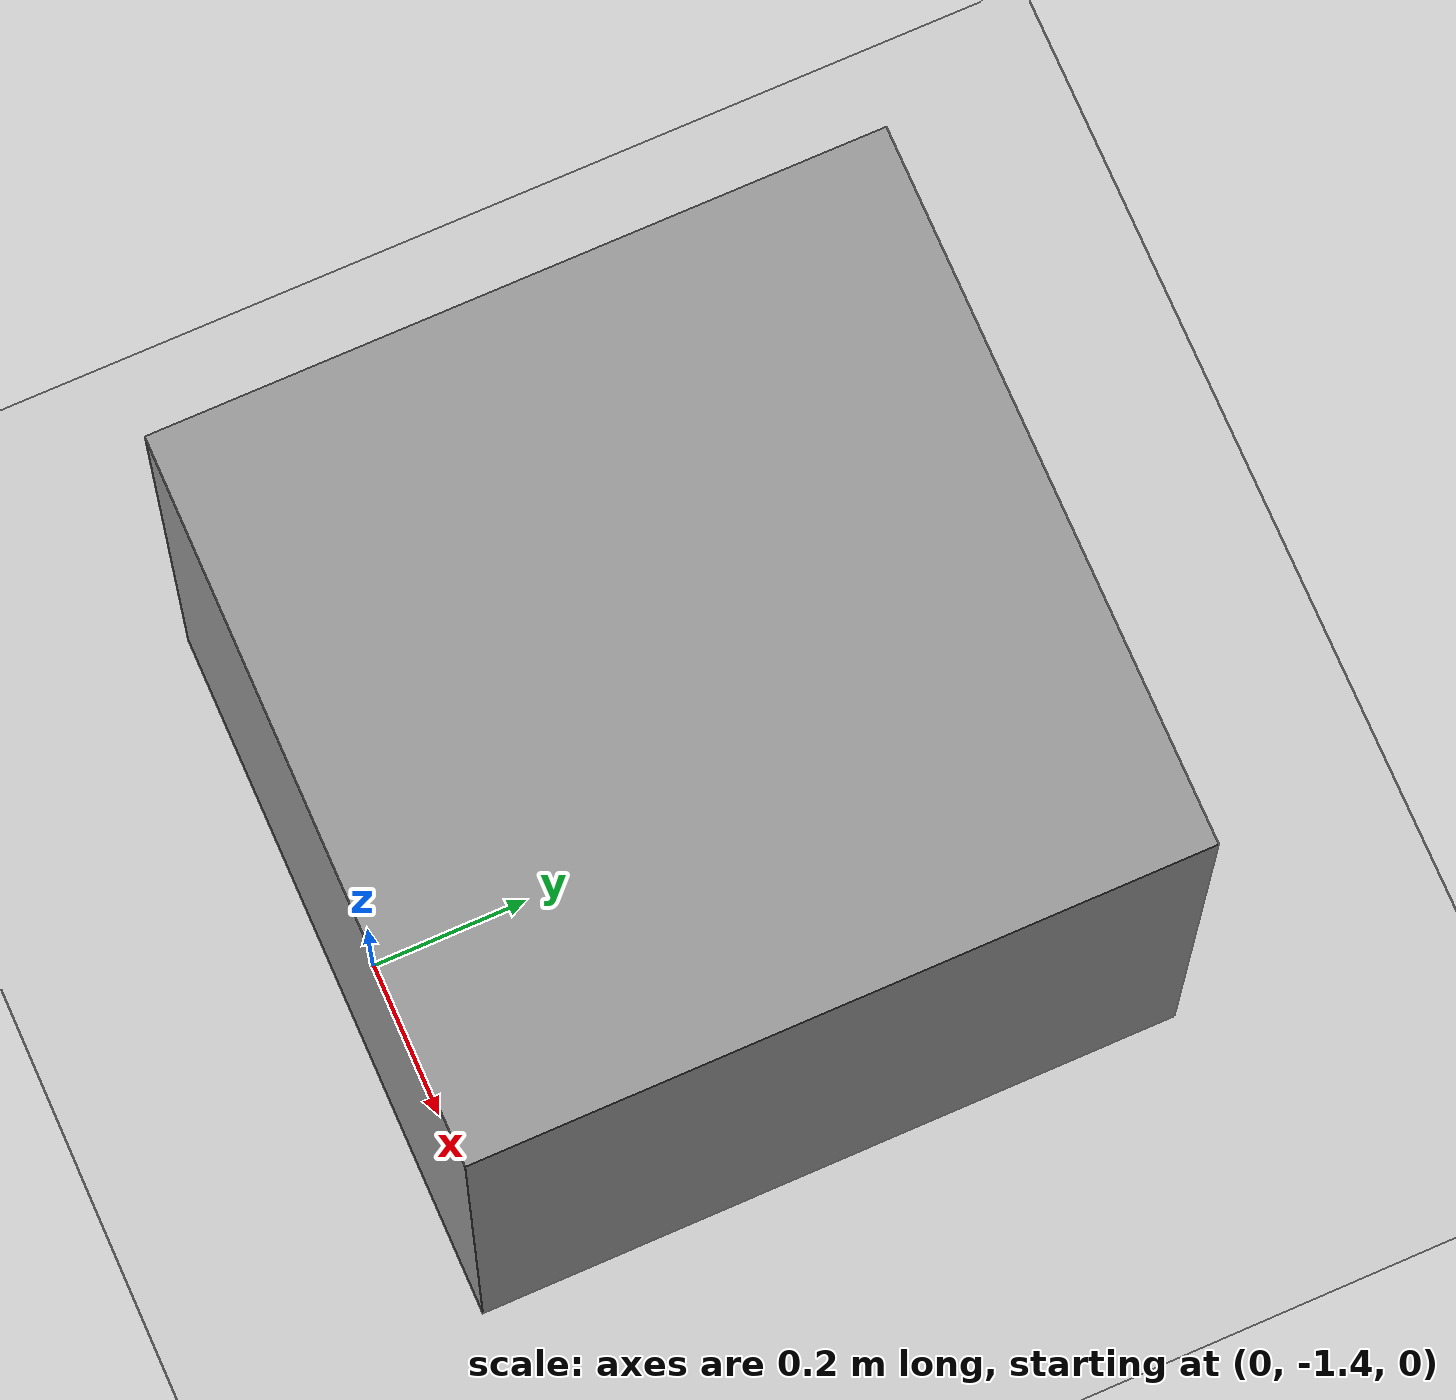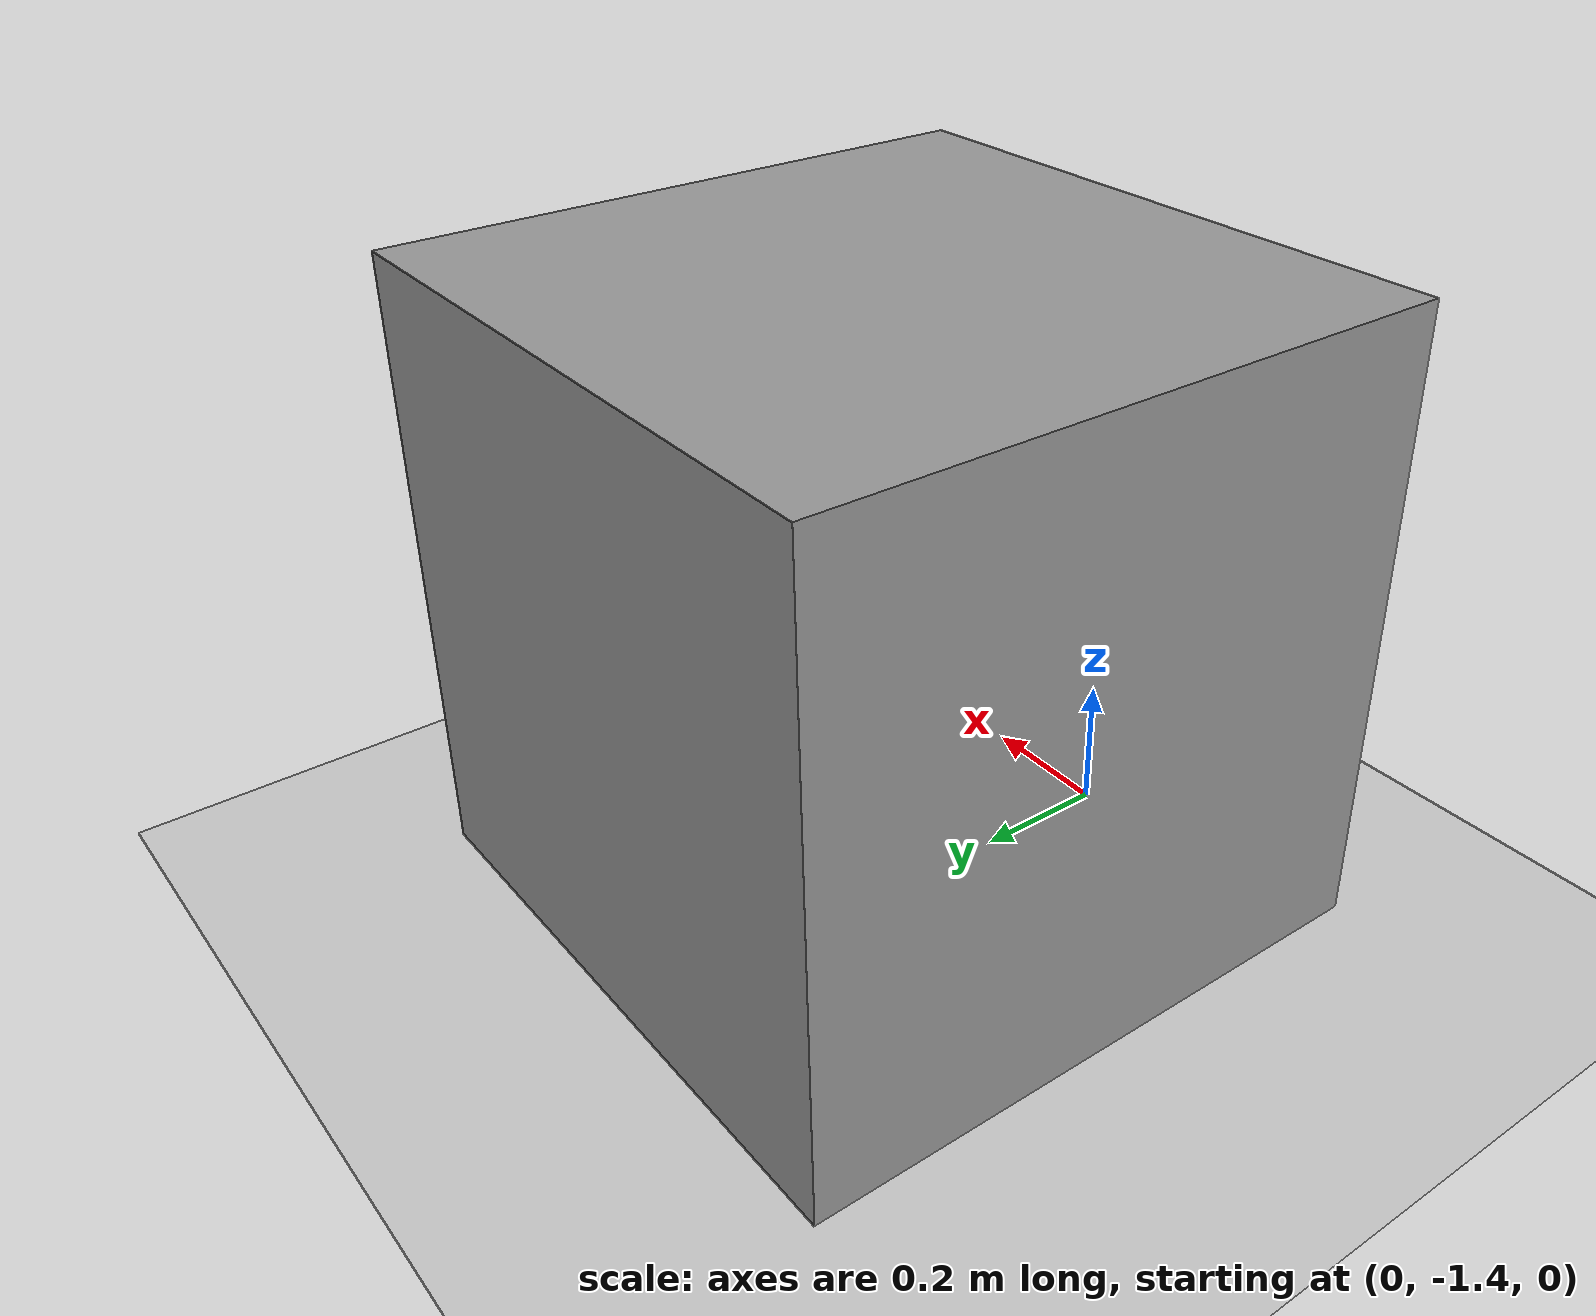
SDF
<sdf version="1.4">
 <world name="default">
  <light name="sun" type="directional">
   <pose>0 0 10 0 -0 0</pose>
   <diffuse>0.8 0.8 0.8 1</diffuse>
   <specular>0.2 0.2 0.2 1</specular>
   <attenuation>
    <range>1000</range>
    <constant>0.9</constant>
    <linear>0.01</linear>
    <quadratic>0.001</quadratic>
   </attenuation>
   <direction>-0.5 0.1 -0.9</direction>
  </light>
  <model name="ground_plane">
   <static>1</static>
   <link name="link">
    <collision name="collision">
     <geometry><plane><normal>0 0 1</normal><size>100 100</size></plane></geometry>
     <surface><friction><ode><mu>100</mu><mu2>50</mu2></ode></friction></surface>
    </collision>
    <visual name="visual">
     <cast_shadows>0</cast_shadows>
     <geometry><plane><normal>0 0 1</normal><size>100 100</size></plane></geometry>
     <material>
      <script><uri>file://media/materials/scripts/gazebo.material</uri><name>Gazebo/Grey</name></script>
     </material>
    </visual>
    <velocity_decay><linear>0</linear><angular>0</angular></velocity_decay>
   </link>
  </model>
  <physics type="ode">
   <max_step_size>0.001</max_step_size>
   <real_time_factor>1</real_time_factor>
   <real_time_update_rate>1000</real_time_update_rate>
   <gravity>0 0 -9.8</gravity>
  </physics>
  <scene><ambient>0.4 0.4 0.4 1</ambient><background>0.7 0.7 0.7 1</background><shadows>1</shadows></scene>
  <spherical_coordinates>
   <surface_model>EARTH_WGS84</surface_model>
   <latitude_deg>0</latitude_deg>
   <longitude_deg>0</longitude_deg>
   <elevation>0</elevation>
   <heading_deg>0</heading_deg>
  </spherical_coordinates>
  <model name="unit_box_0">
   <pose>-0 -1 0.5 0 -0 0</pose>
   <link name="link">
    <inertial>
     <mass>1</mass>
     <inertia><ixx>1</ixx><ixy>0</ixy><ixz>0</ixz><iyy>1</iyy><iyz>0</iyz><izz>1</izz></inertia>
    </inertial>
    <collision name="collision"><geometry><box><size>0.9 0.9 0.9</size></box></geometry></collision>
    <visual name="visual">
     <geometry><box><size>0.9 0.9 0.9</size></box></geometry>
     <material>
      <script><uri>file://media/materials/scripts/gazebo.material</uri><name>Gazebo/Grey</name></script>
     </material>
    </visual>
    <velocity_decay><linear>0</linear><angular>0</angular></velocity_decay>
   </link>
   <static>true</static>
  </model>
  <model name="unit_box_1">
   <pose>-0 -1 0.5 0 -0 0</pose>
   <link name="link">
    <inertial>
     <mass>1</mass>
     <inertia><ixx>1</ixx><ixy>0</ixy><ixz>0</ixz><iyy>1</iyy><iyz>0</iyz><izz>1</izz></inertia>
    </inertial>
    <collision name="collision"><geometry><box><size>0.9 0.9 0.9</size></box></geometry></collision>
    <visual name="visual">
     <geometry><box><size>0.9 0.9 0.9</size></box></geometry>
     <material>
      <script><uri>file://media/materials/scripts/gazebo.material</uri><name>Gazebo/Grey</name></script>
     </material>
    </visual>
    <velocity_decay><linear>0</linear><angular>0</angular></velocity_decay>
   </link>
   <static>true</static>
  </model>
  <model name="unit_box_2">
   <pose>-0 -1 0.5 0 -0 0</pose>
   <link name="link">
    <inertial>
     <mass>1</mass>
     <inertia><ixx>1</ixx><ixy>0</ixy><ixz>0</ixz><iyy>1</iyy><iyz>0</iyz><izz>1</izz></inertia>
    </inertial>
    <collision name="collision"><geometry><box><size>0.9 0.9 0.9</size></box></geometry></collision>
    <visual name="visual">
     <geometry><box><size>0.9 0.9 0.9</size></box></geometry>
     <material>
      <script><uri>file://media/materials/scripts/gazebo.material</uri><name>Gazebo/Grey</name></script>
     </material>
    </visual>
    <velocity_decay><linear>0</linear><angular>0</angular></velocity_decay>
   </link>
   <static>true</static>
  </model>
  <model name="unit_box_3">
   <pose>-0 -1 0.5 0 -0 0</pose>
   <link name="link">
    <inertial>
     <mass>1</mass>
     <inertia><ixx>1</ixx><ixy>0</ixy><ixz>0</ixz><iyy>1</iyy><iyz>0</iyz><izz>1</izz></inertia>
    </inertial>
    <collision name="collision"><geometry><box><size>0.9 0.9 0.9</size></box></geometry></collision>
    <visual name="visual">
     <geometry><box><size>0.9 0.9 0.9</size></box></geometry>
     <material>
      <script><uri>file://media/materials/scripts/gazebo.material</uri><name>Gazebo/Grey</name></script>
     </material>
    </visual>
    <velocity_decay><linear>0</linear><angular>0</angular></velocity_decay>
   </link>
   <static>true</static>
  </model>
  <model name="unit_box_4">
   <pose>-0 -1 0.5 0 -0 0</pose>
   <link name="link">
    <inertial>
     <mass>1</mass>
     <inertia><ixx>1</ixx><ixy>0</ixy><ixz>0</ixz><iyy>1</iyy><iyz>0</iyz><izz>1</izz></inertia>
    </inertial>
    <collision name="collision"><geometry><box><size>0.9 0.9 0.9</size></box></geometry></collision>
    <visual name="visual">
     <geometry><box><size>0.9 0.9 0.9</size></box></geometry>
     <material>
      <script><uri>file://media/materials/scripts/gazebo.material</uri><name>Gazebo/Grey</name></script>
     </material>
    </visual>
    <velocity_decay><linear>0</linear><angular>0</angular></velocity_decay>
   </link>
   <static>true</static>
  </model>
  <model name="unit_box_5">
   <pose>-0 -1 0.5 0 -0 0</pose>
   <link name="link">
    <inertial>
     <mass>1</mass>
     <inertia><ixx>1</ixx><ixy>0</ixy><ixz>0</ixz><iyy>1</iyy><iyz>0</iyz><izz>1</izz></inertia>
    </inertial>
    <collision name="collision"><geometry><box><size>0.9 0.9 0.9</size></box></geometry></collision>
    <visual name="visual">
     <geometry><box><size>0.9 0.9 0.9</size></box></geometry>
     <material>
      <script><uri>file://media/materials/scripts/gazebo.material</uri><name>Gazebo/Grey</name></script>
     </material>
    </visual>
    <velocity_decay><linear>0</linear><angular>0</angular></velocity_decay>
   </link>
   <static>true</static>
  </model>
  <model name="unit_box_6">
   <pose>-0 -1 0.5 0 -0 0</pose>
   <link name="link">
    <inertial>
     <mass>1</mass>
     <inertia><ixx>1</ixx><ixy>0</ixy><ixz>0</ixz><iyy>1</iyy><iyz>0</iyz><izz>1</izz></inertia>
    </inertial>
    <collision name="collision"><geometry><box><size>0.9 0.9 0.9</size></box></geometry></collision>
    <visual name="visual">
     <geometry><box><size>0.9 0.9 0.9</size></box></geometry>
     <material>
      <script><uri>file://media/materials/scripts/gazebo.material</uri><name>Gazebo/Grey</name></script>
     </material>
    </visual>
    <velocity_decay><linear>0</linear><angular>0</angular></velocity_decay>
   </link>
   <static>true</static>
  </model>
  <model name="unit_box_7">
   <pose>-0 -1 0.5 0 -0 0</pose>
   <link name="link">
    <inertial>
     <mass>1</mass>
     <inertia><ixx>1</ixx><ixy>0</ixy><ixz>0</ixz><iyy>1</iyy><iyz>0</iyz><izz>1</izz></inertia>
    </inertial>
    <collision name="collision"><geometry><box><size>0.9 0.9 0.9</size></box></geometry></collision>
    <visual name="visual">
     <geometry><box><size>0.9 0.9 0.9</size></box></geometry>
     <material>
      <script><uri>file://media/materials/scripts/gazebo.material</uri><name>Gazebo/Grey</name></script>
     </material>
    </visual>
    <velocity_decay><linear>0</linear><angular>0</angular></velocity_decay>
   </link>
   <static>true</static>
  </model>
  <model name="unit_box_8">
   <pose>-0 -1 0.5 0 -0 0</pose>
   <link name="link">
    <inertial>
     <mass>1</mass>
     <inertia><ixx>1</ixx><ixy>0</ixy><ixz>0</ixz><iyy>1</iyy><iyz>0</iyz><izz>1</izz></inertia>
    </inertial>
    <collision name="collision"><geometry><box><size>0.9 0.9 0.9</size></box></geometry></collision>
    <visual name="visual">
     <geometry><box><size>0.9 0.9 0.9</size></box></geometry>
     <material>
      <script><uri>file://media/materials/scripts/gazebo.material</uri><name>Gazebo/Grey</name></script>
     </material>
    </visual>
    <velocity_decay><linear>0</linear><angular>0</angular></velocity_decay>
   </link>
   <static>true</static>
  </model>
  <model name="unit_box_9">
   <pose>-0 -1 0.5 0 -0 0</pose>
   <link name="link">
    <inertial>
     <mass>1</mass>
     <inertia><ixx>1</ixx><ixy>0</ixy><ixz>0</ixz><iyy>1</iyy><iyz>0</iyz><izz>1</izz></inertia>
    </inertial>
    <collision name="collision"><geometry><box><size>0.9 0.9 0.9</size></box></geometry></collision>
    <visual name="visual">
     <geometry><box><size>0.9 0.9 0.9</size></box></geometry>
     <material>
      <script><uri>file://media/materials/scripts/gazebo.material</uri><name>Gazebo/Grey</name></script>
     </material>
    </visual>
    <velocity_decay><linear>0</linear><angular>0</angular></velocity_decay>
   </link>
   <static>true</static>
  </model>
  <model name="unit_box_10">
   <pose>-0 -1 0.5 0 -0 0</pose>
   <link name="link">
    <inertial>
     <mass>1</mass>
     <inertia><ixx>1</ixx><ixy>0</ixy><ixz>0</ixz><iyy>1</iyy><iyz>0</iyz><izz>1</izz></inertia>
    </inertial>
    <collision name="collision"><geometry><box><size>0.9 0.9 0.9</size></box></geometry></collision>
    <visual name="visual">
     <geometry><box><size>0.9 0.9 0.9</size></box></geometry>
     <material>
      <script><uri>file://media/materials/scripts/gazebo.material</uri><name>Gazebo/Grey</name></script>
     </material>
    </visual>
    <velocity_decay><linear>0</linear><angular>0</angular></velocity_decay>
   </link>
   <static>true</static>
  </model>
  <model name="unit_box_11">
   <pose>-0 -1 0.5 0 -0 0</pose>
   <link name="link">
    <inertial>
     <mass>1</mass>
     <inertia><ixx>1</ixx><ixy>0</ixy><ixz>0</ixz><iyy>1</iyy><iyz>0</iyz><izz>1</izz></inertia>
    </inertial>
    <collision name="collision"><geometry><box><size>0.9 0.9 0.9</size></box></geometry></collision>
    <visual name="visual">
     <geometry><box><size>0.9 0.9 0.9</size></box></geometry>
     <material>
      <script><uri>file://media/materials/scripts/gazebo.material</uri><name>Gazebo/Grey</name></script>
     </material>
    </visual>
    <velocity_decay><linear>0</linear><angular>0</angular></velocity_decay>
   </link>
   <static>true</static>
  </model>
  <model name="unit_box_12">
   <pose>-0 -1 0.5 0 -0 0</pose>
   <link name="link">
    <inertial>
     <mass>1</mass>
     <inertia><ixx>1</ixx><ixy>0</ixy><ixz>0</ixz><iyy>1</iyy><iyz>0</iyz><izz>1</izz></inertia>
    </inertial>
    <collision name="collision"><geometry><box><size>0.9 0.9 0.9</size></box></geometry></collision>
    <visual name="visual">
     <geometry><box><size>0.9 0.9 0.9</size></box></geometry>
     <material>
      <script><uri>file://media/materials/scripts/gazebo.material</uri><name>Gazebo/Grey</name></script>
     </material>
    </visual>
    <velocity_decay><linear>0</linear><angular>0</angular></velocity_decay>
   </link>
   <static>true</static>
  </model>
  <model name="unit_box_13">
   <pose>-0 -1 0.5 0 -0 0</pose>
   <link name="link">
    <inertial>
     <mass>1</mass>
     <inertia><ixx>1</ixx><ixy>0</ixy><ixz>0</ixz><iyy>1</iyy><iyz>0</iyz><izz>1</izz></inertia>
    </inertial>
    <collision name="collision"><geometry><box><size>0.9 0.9 0.9</size></box></geometry></collision>
    <visual name="visual">
     <geometry><box><size>0.9 0.9 0.9</size></box></geometry>
     <material>
      <script><uri>file://media/materials/scripts/gazebo.material</uri><name>Gazebo/Grey</name></script>
     </material>
    </visual>
    <velocity_decay><linear>0</linear><angular>0</angular></velocity_decay>
   </link>
   <static>true</static>
  </model>
  <model name="unit_box_14">
   <pose>-0 -1 0.5 0 -0 0</pose>
   <link name="link">
    <inertial>
     <mass>1</mass>
     <inertia><ixx>1</ixx><ixy>0</ixy><ixz>0</ixz><iyy>1</iyy><iyz>0</iyz><izz>1</izz></inertia>
    </inertial>
    <collision name="collision"><geometry><box><size>0.9 0.9 0.9</size></box></geometry></collision>
    <visual name="visual">
     <geometry><box><size>0.9 0.9 0.9</size></box></geometry>
     <material>
      <script><uri>file://media/materials/scripts/gazebo.material</uri><name>Gazebo/Grey</name></script>
     </material>
    </visual>
    <velocity_decay><linear>0</linear><angular>0</angular></velocity_decay>
   </link>
   <static>true</static>
  </model>
  <model name="unit_box_15">
   <pose>-0 -1 0.5 0 -0 0</pose>
   <link name="link">
    <inertial>
     <mass>1</mass>
     <inertia><ixx>1</ixx><ixy>0</ixy><ixz>0</ixz><iyy>1</iyy><iyz>0</iyz><izz>1</izz></inertia>
    </inertial>
    <collision name="collision"><geometry><box><size>0.9 0.9 0.9</size></box></geometry></collision>
    <visual name="visual">
     <geometry><box><size>0.9 0.9 0.9</size></box></geometry>
     <material>
      <script><uri>file://media/materials/scripts/gazebo.material</uri><name>Gazebo/Grey</name></script>
     </material>
    </visual>
    <velocity_decay><linear>0</linear><angular>0</angular></velocity_decay>
   </link>
   <static>true</static>
  </model>
  <model name="unit_box_16">
   <pose>-0 -1 0.5 0 -0 0</pose>
   <link name="link">
    <inertial>
     <mass>1</mass>
     <inertia><ixx>1</ixx><ixy>0</ixy><ixz>0</ixz><iyy>1</iyy><iyz>0</iyz><izz>1</izz></inertia>
    </inertial>
    <collision name="collision"><geometry><box><size>0.9 0.9 0.9</size></box></geometry></collision>
    <visual name="visual">
     <geometry><box><size>0.9 0.9 0.9</size></box></geometry>
     <material>
      <script><uri>file://media/materials/scripts/gazebo.material</uri><name>Gazebo/Grey</name></script>
     </material>
    </visual>
    <velocity_decay><linear>0</linear><angular>0</angular></velocity_decay>
   </link>
   <static>true</static>
  </model>
  <model name="unit_box_17">
   <pose>-0 -1 0.5 0 -0 0</pose>
   <link name="link">
    <inertial>
     <mass>1</mass>
     <inertia><ixx>1</ixx><ixy>0</ixy><ixz>0</ixz><iyy>1</iyy><iyz>0</iyz><izz>1</izz></inertia>
    </inertial>
    <collision name="collision"><geometry><box><size>0.9 0.9 0.9</size></box></geometry></collision>
    <visual name="visual">
     <geometry><box><size>0.9 0.9 0.9</size></box></geometry>
     <material>
      <script><uri>file://media/materials/scripts/gazebo.material</uri><name>Gazebo/Grey</name></script>
     </material>
    </visual>
    <velocity_decay><linear>0</linear><angular>0</angular></velocity_decay>
   </link>
   <static>true</static>
  </model>
  <model name="unit_box_18">
   <pose>-0 -1 0.5 0 -0 0</pose>
   <link name="link">
    <inertial>
     <mass>1</mass>
     <inertia><ixx>1</ixx><ixy>0</ixy><ixz>0</ixz><iyy>1</iyy><iyz>0</iyz><izz>1</izz></inertia>
    </inertial>
    <collision name="collision"><geometry><box><size>0.9 0.9 0.9</size></box></geometry></collision>
    <visual name="visual">
     <geometry><box><size>0.9 0.9 0.9</size></box></geometry>
     <material>
      <script><uri>file://media/materials/scripts/gazebo.material</uri><name>Gazebo/Grey</name></script>
     </material>
    </visual>
    <velocity_decay><linear>0</linear><angular>0</angular></velocity_decay>
   </link>
   <static>true</static>
  </model>
  <model name="unit_box_19">
   <pose>-0 -1 0.5 0 -0 0</pose>
   <link name="link">
    <inertial>
     <mass>1</mass>
     <inertia><ixx>1</ixx><ixy>0</ixy><ixz>0</ixz><iyy>1</iyy><iyz>0</iyz><izz>1</izz></inertia>
    </inertial>
    <collision name="collision"><geometry><box><size>0.9 0.9 0.9</size></box></geometry></collision>
    <visual name="visual">
     <geometry><box><size>0.9 0.9 0.9</size></box></geometry>
     <material>
      <script><uri>file://media/materials/scripts/gazebo.material</uri><name>Gazebo/Grey</name></script>
     </material>
    </visual>
    <velocity_decay><linear>0</linear><angular>0</angular></velocity_decay>
   </link>
   <static>true</static>
  </model>
  <model name="unit_box_20">
   <pose>-0 -1 0.5 0 -0 0</pose>
   <link name="link">
    <inertial>
     <mass>1</mass>
     <inertia><ixx>1</ixx><ixy>0</ixy><ixz>0</ixz><iyy>1</iyy><iyz>0</iyz><izz>1</izz></inertia>
    </inertial>
    <collision name="collision"><geometry><box><size>0.9 0.9 0.9</size></box></geometry></collision>
    <visual name="visual">
     <geometry><box><size>0.9 0.9 0.9</size></box></geometry>
     <material>
      <script><uri>file://media/materials/scripts/gazebo.material</uri><name>Gazebo/Grey</name></script>
     </material>
    </visual>
    <velocity_decay><linear>0</linear><angular>0</angular></velocity_decay>
   </link>
   <static>true</static>
  </model>
  <model name="unit_box_21">
   <pose>-0 -1 0.5 0 -0 0</pose>
   <link name="link">
    <inertial>
     <mass>1</mass>
     <inertia><ixx>1</ixx><ixy>0</ixy><ixz>0</ixz><iyy>1</iyy><iyz>0</iyz><izz>1</izz></inertia>
    </inertial>
    <collision name="collision"><geometry><box><size>0.9 0.9 0.9</size></box></geometry></collision>
    <visual name="visual">
     <geometry><box><size>0.9 0.9 0.9</size></box></geometry>
     <material>
      <script><uri>file://media/materials/scripts/gazebo.material</uri><name>Gazebo/Grey</name></script>
     </material>
    </visual>
    <velocity_decay><linear>0</linear><angular>0</angular></velocity_decay>
   </link>
   <static>true</static>
  </model>
  <model name="unit_box_22">
   <pose>-0 -1 0.5 0 -0 0</pose>
   <link name="link">
    <inertial>
     <mass>1</mass>
     <inertia><ixx>1</ixx><ixy>0</ixy><ixz>0</ixz><iyy>1</iyy><iyz>0</iyz><izz>1</izz></inertia>
    </inertial>
    <collision name="collision"><geometry><box><size>0.9 0.9 0.9</size></box></geometry></collision>
    <visual name="visual">
     <geometry><box><size>0.9 0.9 0.9</size></box></geometry>
     <material>
      <script><uri>file://media/materials/scripts/gazebo.material</uri><name>Gazebo/Grey</name></script>
     </material>
    </visual>
    <velocity_decay><linear>0</linear><angular>0</angular></velocity_decay>
   </link>
   <static>true</static>
  </model>
  <model name="unit_box_23">
   <pose>-0 -1 0.5 0 -0 0</pose>
   <link name="link">
    <inertial>
     <mass>1</mass>
     <inertia><ixx>1</ixx><ixy>0</ixy><ixz>0</ixz><iyy>1</iyy><iyz>0</iyz><izz>1</izz></inertia>
    </inertial>
    <collision name="collision"><geometry><box><size>0.9 0.9 0.9</size></box></geometry></collision>
    <visual name="visual">
     <geometry><box><size>0.9 0.9 0.9</size></box></geometry>
     <material>
      <script><uri>file://media/materials/scripts/gazebo.material</uri><name>Gazebo/Grey</name></script>
     </material>
    </visual>
    <velocity_decay><linear>0</linear><angular>0</angular></velocity_decay>
   </link>
   <static>true</static>
  </model>
  <model name="unit_box_24">
   <pose>-0 -1 0.5 0 -0 0</pose>
   <link name="link">
    <inertial>
     <mass>1</mass>
     <inertia><ixx>1</ixx><ixy>0</ixy><ixz>0</ixz><iyy>1</iyy><iyz>0</iyz><izz>1</izz></inertia>
    </inertial>
    <collision name="collision"><geometry><box><size>0.9 0.9 0.9</size></box></geometry></collision>
    <visual name="visual">
     <geometry><box><size>0.9 0.9 0.9</size></box></geometry>
     <material>
      <script><uri>file://media/materials/scripts/gazebo.material</uri><name>Gazebo/Grey</name></script>
     </material>
    </visual>
    <velocity_decay><linear>0</linear><angular>0</angular></velocity_decay>
   </link>
   <static>true</static>
  </model>
  <model name="unit_box_25">
   <pose>-0 -1 0.5 0 -0 0</pose>
   <link name="link">
    <inertial>
     <mass>1</mass>
     <inertia><ixx>1</ixx><ixy>0</ixy><ixz>0</ixz><iyy>1</iyy><iyz>0</iyz><izz>1</izz></inertia>
    </inertial>
    <collision name="collision"><geometry><box><size>0.9 0.9 0.9</size></box></geometry></collision>
    <visual name="visual">
     <geometry><box><size>0.9 0.9 0.9</size></box></geometry>
     <material>
      <script><uri>file://media/materials/scripts/gazebo.material</uri><name>Gazebo/Grey</name></script>
     </material>
    </visual>
    <velocity_decay><linear>0</linear><angular>0</angular></velocity_decay>
   </link>
   <static>true</static>
  </model>
  <model name="unit_box_26">
   <pose>-0 -1 0.5 0 -0 0</pose>
   <link name="link">
    <inertial>
     <mass>1</mass>
     <inertia><ixx>1</ixx><ixy>0</ixy><ixz>0</ixz><iyy>1</iyy><iyz>0</iyz><izz>1</izz></inertia>
    </inertial>
    <collision name="collision"><geometry><box><size>0.9 0.9 0.9</size></box></geometry></collision>
    <visual name="visual">
     <geometry><box><size>0.9 0.9 0.9</size></box></geometry>
     <material>
      <script><uri>file://media/materials/scripts/gazebo.material</uri><name>Gazebo/Grey</name></script>
     </material>
    </visual>
    <velocity_decay><linear>0</linear><angular>0</angular></velocity_decay>
   </link>
   <static>true</static>
  </model>
  <model name="unit_box_27">
   <pose>-0 -1 0.5 0 -0 0</pose>
   <link name="link">
    <inertial>
     <mass>1</mass>
     <inertia><ixx>1</ixx><ixy>0</ixy><ixz>0</ixz><iyy>1</iyy><iyz>0</iyz><izz>1</izz></inertia>
    </inertial>
    <collision name="collision"><geometry><box><size>0.9 0.9 0.9</size></box></geometry></collision>
    <visual name="visual">
     <geometry><box><size>0.9 0.9 0.9</size></box></geometry>
     <material>
      <script><uri>file://media/materials/scripts/gazebo.material</uri><name>Gazebo/Grey</name></script>
     </material>
    </visual>
    <velocity_decay><linear>0</linear><angular>0</angular></velocity_decay>
   </link>
   <static>true</static>
  </model>
  <model name="unit_box_28">
   <pose>-0 -1 0.5 0 -0 0</pose>
   <link name="link">
    <inertial>
     <mass>1</mass>
     <inertia><ixx>1</ixx><ixy>0</ixy><ixz>0</ixz><iyy>1</iyy><iyz>0</iyz><izz>1</izz></inertia>
    </inertial>
    <collision name="collision"><geometry><box><size>0.9 0.9 0.9</size></box></geometry></collision>
    <visual name="visual">
     <geometry><box><size>0.9 0.9 0.9</size></box></geometry>
     <material>
      <script><uri>file://media/materials/scripts/gazebo.material</uri><name>Gazebo/Grey</name></script>
     </material>
    </visual>
    <velocity_decay><linear>0</linear><angular>0</angular></velocity_decay>
   </link>
   <static>true</static>
  </model>
  <model name="unit_box_29">
   <pose>-0 -1 0.5 0 -0 0</pose>
   <link name="link">
    <inertial>
     <mass>1</mass>
     <inertia><ixx>1</ixx><ixy>0</ixy><ixz>0</ixz><iyy>1</iyy><iyz>0</iyz><izz>1</izz></inertia>
    </inertial>
    <collision name="collision"><geometry><box><size>0.9 0.9 0.9</size></box></geometry></collision>
    <visual name="visual">
     <geometry><box><size>0.9 0.9 0.9</size></box></geometry>
     <material>
      <script><uri>file://media/materials/scripts/gazebo.material</uri><name>Gazebo/Grey</name></script>
     </material>
    </visual>
    <velocity_decay><linear>0</linear><angular>0</angular></velocity_decay>
   </link>
   <static>true</static>
  </model>
  <model name="unit_box_30">
   <pose>-0 -1 0.5 0 -0 0</pose>
   <link name="link">
    <inertial>
     <mass>1</mass>
     <inertia><ixx>1</ixx><ixy>0</ixy><ixz>0</ixz><iyy>1</iyy><iyz>0</iyz><izz>1</izz></inertia>
    </inertial>
    <collision name="collision"><geometry><box><size>0.9 0.9 0.9</size></box></geometry></collision>
    <visual name="visual">
     <geometry><box><size>0.9 0.9 0.9</size></box></geometry>
     <material>
      <script><uri>file://media/materials/scripts/gazebo.material</uri><name>Gazebo/Grey</name></script>
     </material>
    </visual>
    <velocity_decay><linear>0</linear><angular>0</angular></velocity_decay>
   </link>
   <static>true</static>
  </model>
  <model name="unit_box_31">
   <pose>-0 -1 0.5 0 -0 0</pose>
   <link name="link">
    <inertial>
     <mass>1</mass>
     <inertia><ixx>1</ixx><ixy>0</ixy><ixz>0</ixz><iyy>1</iyy><iyz>0</iyz><izz>1</izz></inertia>
    </inertial>
    <collision name="collision"><geometry><box><size>0.9 0.9 0.9</size></box></geometry></collision>
    <visual name="visual">
     <geometry><box><size>0.9 0.9 0.9</size></box></geometry>
     <material>
      <script><uri>file://media/materials/scripts/gazebo.material</uri><name>Gazebo/Grey</name></script>
     </material>
    </visual>
    <velocity_decay><linear>0</linear><angular>0</angular></velocity_decay>
   </link>
   <static>true</static>
  </model>
  <model name="unit_box_32">
   <pose>-0 -1 0.5 0 -0 0</pose>
   <link name="link">
    <inertial>
     <mass>1</mass>
     <inertia><ixx>1</ixx><ixy>0</ixy><ixz>0</ixz><iyy>1</iyy><iyz>0</iyz><izz>1</izz></inertia>
    </inertial>
    <collision name="collision"><geometry><box><size>0.9 0.9 0.9</size></box></geometry></collision>
    <visual name="visual">
     <geometry><box><size>0.9 0.9 0.9</size></box></geometry>
     <material>
      <script><uri>file://media/materials/scripts/gazebo.material</uri><name>Gazebo/Grey</name></script>
     </material>
    </visual>
    <velocity_decay><linear>0</linear><angular>0</angular></velocity_decay>
   </link>
   <static>true</static>
  </model>
  <model name="unit_box_33">
   <pose>-0 -1 0.5 0 -0 0</pose>
   <link name="link">
    <inertial>
     <mass>1</mass>
     <inertia><ixx>1</ixx><ixy>0</ixy><ixz>0</ixz><iyy>1</iyy><iyz>0</iyz><izz>1</izz></inertia>
    </inertial>
    <collision name="collision"><geometry><box><size>0.9 0.9 0.9</size></box></geometry></collision>
    <visual name="visual">
     <geometry><box><size>0.9 0.9 0.9</size></box></geometry>
     <material>
      <script><uri>file://media/materials/scripts/gazebo.material</uri><name>Gazebo/Grey</name></script>
     </material>
    </visual>
    <velocity_decay><linear>0</linear><angular>0</angular></velocity_decay>
   </link>
   <static>true</static>
  </model>
  <model name="unit_box_34">
   <pose>-0 -1 0.5 0 -0 0</pose>
   <link name="link">
    <inertial>
     <mass>1</mass>
     <inertia><ixx>1</ixx><ixy>0</ixy><ixz>0</ixz><iyy>1</iyy><iyz>0</iyz><izz>1</izz></inertia>
    </inertial>
    <collision name="collision"><geometry><box><size>0.9 0.9 0.9</size></box></geometry></collision>
    <visual name="visual">
     <geometry><box><size>0.9 0.9 0.9</size></box></geometry>
     <material>
      <script><uri>file://media/materials/scripts/gazebo.material</uri><name>Gazebo/Grey</name></script>
     </material>
    </visual>
    <velocity_decay><linear>0</linear><angular>0</angular></velocity_decay>
   </link>
   <static>true</static>
  </model>
  <model name="unit_box_35">
   <pose>-0 -1 0.5 0 -0 0</pose>
   <link name="link">
    <inertial>
     <mass>1</mass>
     <inertia><ixx>1</ixx><ixy>0</ixy><ixz>0</ixz><iyy>1</iyy><iyz>0</iyz><izz>1</izz></inertia>
    </inertial>
    <collision name="collision"><geometry><box><size>0.9 0.9 0.9</size></box></geometry></collision>
    <visual name="visual">
     <geometry><box><size>0.9 0.9 0.9</size></box></geometry>
     <material>
      <script><uri>file://media/materials/scripts/gazebo.material</uri><name>Gazebo/Grey</name></script>
     </material>
    </visual>
    <velocity_decay><linear>0</linear><angular>0</angular></velocity_decay>
   </link>
   <static>true</static>
  </model>
  <model name="unit_box_36">
   <pose>-0 -1 0.5 0 -0 0</pose>
   <link name="link">
    <inertial>
     <mass>1</mass>
     <inertia><ixx>1</ixx><ixy>0</ixy><ixz>0</ixz><iyy>1</iyy><iyz>0</iyz><izz>1</izz></inertia>
    </inertial>
    <collision name="collision"><geometry><box><size>0.9 0.9 0.9</size></box></geometry></collision>
    <visual name="visual">
     <geometry><box><size>0.9 0.9 0.9</size></box></geometry>
     <material>
      <script><uri>file://media/materials/scripts/gazebo.material</uri><name>Gazebo/Grey</name></script>
     </material>
    </visual>
    <velocity_decay><linear>0</linear><angular>0</angular></velocity_decay>
   </link>
   <static>true</static>
  </model>
  <model name="unit_box_37">
   <pose>-0 -1 0.5 0 -0 0</pose>
   <link name="link">
    <inertial>
     <mass>1</mass>
     <inertia><ixx>1</ixx><ixy>0</ixy><ixz>0</ixz><iyy>1</iyy><iyz>0</iyz><izz>1</izz></inertia>
    </inertial>
    <collision name="collision"><geometry><box><size>0.9 0.9 0.9</size></box></geometry></collision>
    <visual name="visual">
     <geometry><box><size>0.9 0.9 0.9</size></box></geometry>
     <material>
      <script><uri>file://media/materials/scripts/gazebo.material</uri><name>Gazebo/Grey</name></script>
     </material>
    </visual>
    <velocity_decay><linear>0</linear><angular>0</angular></velocity_decay>
   </link>
   <static>true</static>
  </model>
  <model name="unit_box_38">
   <pose>-0 -1 0.5 0 -0 0</pose>
   <link name="link">
    <inertial>
     <mass>1</mass>
     <inertia><ixx>1</ixx><ixy>0</ixy><ixz>0</ixz><iyy>1</iyy><iyz>0</iyz><izz>1</izz></inertia>
    </inertial>
    <collision name="collision"><geometry><box><size>0.9 0.9 0.9</size></box></geometry></collision>
    <visual name="visual">
     <geometry><box><size>0.9 0.9 0.9</size></box></geometry>
     <material>
      <script><uri>file://media/materials/scripts/gazebo.material</uri><name>Gazebo/Grey</name></script>
     </material>
    </visual>
    <velocity_decay><linear>0</linear><angular>0</angular></velocity_decay>
   </link>
   <static>true</static>
  </model>
  <model name="unit_box_39">
   <pose>-0 -1 0.5 0 -0 0</pose>
   <link name="link">
    <inertial>
     <mass>1</mass>
     <inertia><ixx>1</ixx><ixy>0</ixy><ixz>0</ixz><iyy>1</iyy><iyz>0</iyz><izz>1</izz></inertia>
    </inertial>
    <collision name="collision"><geometry><box><size>0.9 0.9 0.9</size></box></geometry></collision>
    <visual name="visual">
     <geometry><box><size>0.9 0.9 0.9</size></box></geometry>
     <material>
      <script><uri>file://media/materials/scripts/gazebo.material</uri><name>Gazebo/Grey</name></script>
     </material>
    </visual>
    <velocity_decay><linear>0</linear><angular>0</angular></velocity_decay>
   </link>
   <static>true</static>
  </model>
  <model name="unit_box_40">
   <pose>-0 -1 0.5 0 -0 0</pose>
   <link name="link">
    <inertial>
     <mass>1</mass>
     <inertia><ixx>1</ixx><ixy>0</ixy><ixz>0</ixz><iyy>1</iyy><iyz>0</iyz><izz>1</izz></inertia>
    </inertial>
    <collision name="collision"><geometry><box><size>0.9 0.9 0.9</size></box></geometry></collision>
    <visual name="visual">
     <geometry><box><size>0.9 0.9 0.9</size></box></geometry>
     <material>
      <script><uri>file://media/materials/scripts/gazebo.material</uri><name>Gazebo/Grey</name></script>
     </material>
    </visual>
    <velocity_decay><linear>0</linear><angular>0</angular></velocity_decay>
   </link>
   <static>true</static>
  </model>
  <model name="unit_box_41">
   <pose>-0 -1 0.5 0 -0 0</pose>
   <link name="link">
    <inertial>
     <mass>1</mass>
     <inertia><ixx>1</ixx><ixy>0</ixy><ixz>0</ixz><iyy>1</iyy><iyz>0</iyz><izz>1</izz></inertia>
    </inertial>
    <collision name="collision"><geometry><box><size>0.9 0.9 0.9</size></box></geometry></collision>
    <visual name="visual">
     <geometry><box><size>0.9 0.9 0.9</size></box></geometry>
     <material>
      <script><uri>file://media/materials/scripts/gazebo.material</uri><name>Gazebo/Grey</name></script>
     </material>
    </visual>
    <velocity_decay><linear>0</linear><angular>0</angular></velocity_decay>
   </link>
   <static>true</static>
  </model>
  <model name="unit_box_42">
   <pose>-0 -1 0.5 0 -0 0</pose>
   <link name="link">
    <inertial>
     <mass>1</mass>
     <inertia><ixx>1</ixx><ixy>0</ixy><ixz>0</ixz><iyy>1</iyy><iyz>0</iyz><izz>1</izz></inertia>
    </inertial>
    <collision name="collision"><geometry><box><size>0.9 0.9 0.9</size></box></geometry></collision>
    <visual name="visual">
     <geometry><box><size>0.9 0.9 0.9</size></box></geometry>
     <material>
      <script><uri>file://media/materials/scripts/gazebo.material</uri><name>Gazebo/Grey</name></script>
     </material>
    </visual>
    <velocity_decay><linear>0</linear><angular>0</angular></velocity_decay>
   </link>
   <static>true</static>
  </model>
  <model name="unit_box_43">
   <pose>-0 -1 0.5 0 -0 0</pose>
   <link name="link">
    <inertial>
     <mass>1</mass>
     <inertia><ixx>1</ixx><ixy>0</ixy><ixz>0</ixz><iyy>1</iyy><iyz>0</iyz><izz>1</izz></inertia>
    </inertial>
    <collision name="collision"><geometry><box><size>0.9 0.9 0.9</size></box></geometry></collision>
    <visual name="visual">
     <geometry><box><size>0.9 0.9 0.9</size></box></geometry>
     <material>
      <script><uri>file://media/materials/scripts/gazebo.material</uri><name>Gazebo/Grey</name></script>
     </material>
    </visual>
    <velocity_decay><linear>0</linear><angular>0</angular></velocity_decay>
   </link>
   <static>true</static>
  </model>
  <model name="unit_box_44">
   <pose>-0 -1 0.5 0 -0 0</pose>
   <link name="link">
    <inertial>
     <mass>1</mass>
     <inertia><ixx>1</ixx><ixy>0</ixy><ixz>0</ixz><iyy>1</iyy><iyz>0</iyz><izz>1</izz></inertia>
    </inertial>
    <collision name="collision"><geometry><box><size>0.9 0.9 0.9</size></box></geometry></collision>
    <visual name="visual">
     <geometry><box><size>0.9 0.9 0.9</size></box></geometry>
     <material>
      <script><uri>file://media/materials/scripts/gazebo.material</uri><name>Gazebo/Grey</name></script>
     </material>
    </visual>
    <velocity_decay><linear>0</linear><angular>0</angular></velocity_decay>
   </link>
   <static>true</static>
  </model>
  <model name="unit_box_45">
   <pose>-0 -1 0.5 0 -0 0</pose>
   <link name="link">
    <inertial>
     <mass>1</mass>
     <inertia><ixx>1</ixx><ixy>0</ixy><ixz>0</ixz><iyy>1</iyy><iyz>0</iyz><izz>1</izz></inertia>
    </inertial>
    <collision name="collision"><geometry><box><size>0.9 0.9 0.9</size></box></geometry></collision>
    <visual name="visual">
     <geometry><box><size>0.9 0.9 0.9</size></box></geometry>
     <material>
      <script><uri>file://media/materials/scripts/gazebo.material</uri><name>Gazebo/Grey</name></script>
     </material>
    </visual>
    <velocity_decay><linear>0</linear><angular>0</angular></velocity_decay>
   </link>
   <static>true</static>
  </model>
  <model name="unit_box_46">
   <pose>-0 -1 0.5 0 -0 0</pose>
   <link name="link">
    <inertial>
     <mass>1</mass>
     <inertia><ixx>1</ixx><ixy>0</ixy><ixz>0</ixz><iyy>1</iyy><iyz>0</iyz><izz>1</izz></inertia>
    </inertial>
    <collision name="collision"><geometry><box><size>0.9 0.9 0.9</size></box></geometry></collision>
    <visual name="visual">
     <geometry><box><size>0.9 0.9 0.9</size></box></geometry>
     <material>
      <script><uri>file://media/materials/scripts/gazebo.material</uri><name>Gazebo/Grey</name></script>
     </material>
    </visual>
    <velocity_decay><linear>0</linear><angular>0</angular></velocity_decay>
   </link>
   <static>true</static>
  </model>
  <model name="unit_box_47">
   <pose>-0 -1 0.5 0 -0 0</pose>
   <link name="link">
    <inertial>
     <mass>1</mass>
     <inertia><ixx>1</ixx><ixy>0</ixy><ixz>0</ixz><iyy>1</iyy><iyz>0</iyz><izz>1</izz></inertia>
    </inertial>
    <collision name="collision"><geometry><box><size>0.9 0.9 0.9</size></box></geometry></collision>
    <visual name="visual">
     <geometry><box><size>0.9 0.9 0.9</size></box></geometry>
     <material>
      <script><uri>file://media/materials/scripts/gazebo.material</uri><name>Gazebo/Grey</name></script>
     </material>
    </visual>
    <velocity_decay><linear>0</linear><angular>0</angular></velocity_decay>
   </link>
   <static>true</static>
  </model>
  <model name="unit_box_48">
   <pose>-0 -1 0.5 0 -0 0</pose>
   <link name="link">
    <inertial>
     <mass>1</mass>
     <inertia><ixx>1</ixx><ixy>0</ixy><ixz>0</ixz><iyy>1</iyy><iyz>0</iyz><izz>1</izz></inertia>
    </inertial>
    <collision name="collision"><geometry><box><size>0.9 0.9 0.9</size></box></geometry></collision>
    <visual name="visual">
     <geometry><box><size>0.9 0.9 0.9</size></box></geometry>
     <material>
      <script><uri>file://media/materials/scripts/gazebo.material</uri><name>Gazebo/Grey</name></script>
     </material>
    </visual>
    <velocity_decay><linear>0</linear><angular>0</angular></velocity_decay>
   </link>
   <static>true</static>
  </model>
  <model name="unit_box_49">
   <pose>-0 -1 0.5 0 -0 0</pose>
   <link name="link">
    <inertial>
     <mass>1</mass>
     <inertia><ixx>1</ixx><ixy>0</ixy><ixz>0</ixz><iyy>1</iyy><iyz>0</iyz><izz>1</izz></inertia>
    </inertial>
    <collision name="collision"><geometry><box><size>0.9 0.9 0.9</size></box></geometry></collision>
    <visual name="visual">
     <geometry><box><size>0.9 0.9 0.9</size></box></geometry>
     <material>
      <script><uri>file://media/materials/scripts/gazebo.material</uri><name>Gazebo/Grey</name></script>
     </material>
    </visual>
    <velocity_decay><linear>0</linear><angular>0</angular></velocity_decay>
   </link>
   <static>true</static>
  </model>
  <model name="unit_box_50">
   <pose>-0 -1 0.5 0 -0 0</pose>
   <link name="link">
    <inertial>
     <mass>1</mass>
     <inertia><ixx>1</ixx><ixy>0</ixy><ixz>0</ixz><iyy>1</iyy><iyz>0</iyz><izz>1</izz></inertia>
    </inertial>
    <collision name="collision"><geometry><box><size>0.9 0.9 0.9</size></box></geometry></collision>
    <visual name="visual">
     <geometry><box><size>0.9 0.9 0.9</size></box></geometry>
     <material>
      <script><uri>file://media/materials/scripts/gazebo.material</uri><name>Gazebo/Grey</name></script>
     </material>
    </visual>
    <velocity_decay><linear>0</linear><angular>0</angular></velocity_decay>
   </link>
   <static>true</static>
  </model>
  <model name="unit_box_51">
   <pose>-0 -1 0.5 0 -0 0</pose>
   <link name="link">
    <inertial>
     <mass>1</mass>
     <inertia><ixx>1</ixx><ixy>0</ixy><ixz>0</ixz><iyy>1</iyy><iyz>0</iyz><izz>1</izz></inertia>
    </inertial>
    <collision name="collision"><geometry><box><size>0.9 0.9 0.9</size></box></geometry></collision>
    <visual name="visual">
     <geometry><box><size>0.9 0.9 0.9</size></box></geometry>
     <material>
      <script><uri>file://media/materials/scripts/gazebo.material</uri><name>Gazebo/Grey</name></script>
     </material>
    </visual>
    <velocity_decay><linear>0</linear><angular>0</angular></velocity_decay>
   </link>
   <static>true</static>
  </model>
  <model name="unit_box_52">
   <pose>-0 -1 0.5 0 -0 0</pose>
   <link name="link">
    <inertial>
     <mass>1</mass>
     <inertia><ixx>1</ixx><ixy>0</ixy><ixz>0</ixz><iyy>1</iyy><iyz>0</iyz><izz>1</izz></inertia>
    </inertial>
    <collision name="collision"><geometry><box><size>0.9 0.9 0.9</size></box></geometry></collision>
    <visual name="visual">
     <geometry><box><size>0.9 0.9 0.9</size></box></geometry>
     <material>
      <script><uri>file://media/materials/scripts/gazebo.material</uri><name>Gazebo/Grey</name></script>
     </material>
    </visual>
    <velocity_decay><linear>0</linear><angular>0</angular></velocity_decay>
   </link>
   <static>true</static>
  </model>
  <model name="unit_box_53">
   <pose>-0 -1 0.5 0 -0 0</pose>
   <link name="link">
    <inertial>
     <mass>1</mass>
     <inertia><ixx>1</ixx><ixy>0</ixy><ixz>0</ixz><iyy>1</iyy><iyz>0</iyz><izz>1</izz></inertia>
    </inertial>
    <collision name="collision"><geometry><box><size>0.9 0.9 0.9</size></box></geometry></collision>
    <visual name="visual">
     <geometry><box><size>0.9 0.9 0.9</size></box></geometry>
     <material>
      <script><uri>file://media/materials/scripts/gazebo.material</uri><name>Gazebo/Grey</name></script>
     </material>
    </visual>
    <velocity_decay><linear>0</linear><angular>0</angular></velocity_decay>
   </link>
   <static>true</static>
  </model>
  <model name="unit_box_54">
   <pose>-0 -1 0.5 0 -0 0</pose>
   <link name="link">
    <inertial>
     <mass>1</mass>
     <inertia><ixx>1</ixx><ixy>0</ixy><ixz>0</ixz><iyy>1</iyy><iyz>0</iyz><izz>1</izz></inertia>
    </inertial>
    <collision name="collision"><geometry><box><size>0.9 0.9 0.9</size></box></geometry></collision>
    <visual name="visual">
     <geometry><box><size>0.9 0.9 0.9</size></box></geometry>
     <material>
      <script><uri>file://media/materials/scripts/gazebo.material</uri><name>Gazebo/Grey</name></script>
     </material>
    </visual>
    <velocity_decay><linear>0</linear><angular>0</angular></velocity_decay>
   </link>
   <static>true</static>
  </model>
  <model name="unit_box_55">
   <pose>-0 -1 0.5 0 -0 0</pose>
   <link name="link">
    <inertial>
     <mass>1</mass>
     <inertia><ixx>1</ixx><ixy>0</ixy><ixz>0</ixz><iyy>1</iyy><iyz>0</iyz><izz>1</izz></inertia>
    </inertial>
    <collision name="collision"><geometry><box><size>0.9 0.9 0.9</size></box></geometry></collision>
    <visual name="visual">
     <geometry><box><size>0.9 0.9 0.9</size></box></geometry>
     <material>
      <script><uri>file://media/materials/scripts/gazebo.material</uri><name>Gazebo/Grey</name></script>
     </material>
    </visual>
    <velocity_decay><linear>0</linear><angular>0</angular></velocity_decay>
   </link>
   <static>true</static>
  </model>
  <model name="unit_box_56">
   <pose>-0 -1 0.5 0 -0 0</pose>
   <link name="link">
    <inertial>
     <mass>1</mass>
     <inertia><ixx>1</ixx><ixy>0</ixy><ixz>0</ixz><iyy>1</iyy><iyz>0</iyz><izz>1</izz></inertia>
    </inertial>
    <collision name="collision"><geometry><box><size>0.9 0.9 0.9</size></box></geometry></collision>
    <visual name="visual">
     <geometry><box><size>0.9 0.9 0.9</size></box></geometry>
     <material>
      <script><uri>file://media/materials/scripts/gazebo.material</uri><name>Gazebo/Grey</name></script>
     </material>
    </visual>
    <velocity_decay><linear>0</linear><angular>0</angular></velocity_decay>
   </link>
   <static>true</static>
  </model>
  <model name="unit_box_57">
   <pose>-0 -1 0.5 0 -0 0</pose>
   <link name="link">
    <inertial>
     <mass>1</mass>
     <inertia><ixx>1</ixx><ixy>0</ixy><ixz>0</ixz><iyy>1</iyy><iyz>0</iyz><izz>1</izz></inertia>
    </inertial>
    <collision name="collision"><geometry><box><size>0.9 0.9 0.9</size></box></geometry></collision>
    <visual name="visual">
     <geometry><box><size>0.9 0.9 0.9</size></box></geometry>
     <material>
      <script><uri>file://media/materials/scripts/gazebo.material</uri><name>Gazebo/Grey</name></script>
     </material>
    </visual>
    <velocity_decay><linear>0</linear><angular>0</angular></velocity_decay>
   </link>
   <static>true</static>
  </model>
  <model name="unit_box_58">
   <pose>-0 -1 0.5 0 -0 0</pose>
   <link name="link">
    <inertial>
     <mass>1</mass>
     <inertia><ixx>1</ixx><ixy>0</ixy><ixz>0</ixz><iyy>1</iyy><iyz>0</iyz><izz>1</izz></inertia>
    </inertial>
    <collision name="collision"><geometry><box><size>0.9 0.9 0.9</size></box></geometry></collision>
    <visual name="visual">
     <geometry><box><size>0.9 0.9 0.9</size></box></geometry>
     <material>
      <script><uri>file://media/materials/scripts/gazebo.material</uri><name>Gazebo/Grey</name></script>
     </material>
    </visual>
    <velocity_decay><linear>0</linear><angular>0</angular></velocity_decay>
   </link>
   <static>true</static>
  </model>
  <model name="unit_box_59">
   <pose>-0 -1 0.5 0 -0 0</pose>
   <link name="link">
    <inertial>
     <mass>1</mass>
     <inertia><ixx>1</ixx><ixy>0</ixy><ixz>0</ixz><iyy>1</iyy><iyz>0</iyz><izz>1</izz></inertia>
    </inertial>
    <collision name="collision"><geometry><box><size>0.9 0.9 0.9</size></box></geometry></collision>
    <visual name="visual">
     <geometry><box><size>0.9 0.9 0.9</size></box></geometry>
     <material>
      <script><uri>file://media/materials/scripts/gazebo.material</uri><name>Gazebo/Grey</name></script>
     </material>
    </visual>
    <velocity_decay><linear>0</linear><angular>0</angular></velocity_decay>
   </link>
   <static>true</static>
  </model>
  <model name="unit_box_60">
   <pose>-0 -1 0.5 0 -0 0</pose>
   <link name="link">
    <inertial>
     <mass>1</mass>
     <inertia><ixx>1</ixx><ixy>0</ixy><ixz>0</ixz><iyy>1</iyy><iyz>0</iyz><izz>1</izz></inertia>
    </inertial>
    <collision name="collision"><geometry><box><size>0.9 0.9 0.9</size></box></geometry></collision>
    <visual name="visual">
     <geometry><box><size>0.9 0.9 0.9</size></box></geometry>
     <material>
      <script><uri>file://media/materials/scripts/gazebo.material</uri><name>Gazebo/Grey</name></script>
     </material>
    </visual>
    <velocity_decay><linear>0</linear><angular>0</angular></velocity_decay>
   </link>
   <static>true</static>
  </model>
  <model name="unit_box_61">
   <pose>-0 -1 0.5 0 -0 0</pose>
   <link name="link">
    <inertial>
     <mass>1</mass>
     <inertia><ixx>1</ixx><ixy>0</ixy><ixz>0</ixz><iyy>1</iyy><iyz>0</iyz><izz>1</izz></inertia>
    </inertial>
    <collision name="collision"><geometry><box><size>0.9 0.9 0.9</size></box></geometry></collision>
    <visual name="visual">
     <geometry><box><size>0.9 0.9 0.9</size></box></geometry>
     <material>
      <script><uri>file://media/materials/scripts/gazebo.material</uri><name>Gazebo/Grey</name></script>
     </material>
    </visual>
    <velocity_decay><linear>0</linear><angular>0</angular></velocity_decay>
   </link>
   <static>true</static>
  </model>
  <model name="unit_box_62">
   <pose>-0 -1 0.5 0 -0 0</pose>
   <link name="link">
    <inertial>
     <mass>1</mass>
     <inertia><ixx>1</ixx><ixy>0</ixy><ixz>0</ixz><iyy>1</iyy><iyz>0</iyz><izz>1</izz></inertia>
    </inertial>
    <collision name="collision"><geometry><box><size>0.9 0.9 0.9</size></box></geometry></collision>
    <visual name="visual">
     <geometry><box><size>0.9 0.9 0.9</size></box></geometry>
     <material>
      <script><uri>file://media/materials/scripts/gazebo.material</uri><name>Gazebo/Grey</name></script>
     </material>
    </visual>
    <velocity_decay><linear>0</linear><angular>0</angular></velocity_decay>
   </link>
   <static>true</static>
  </model>
  <model name="unit_box_63">
   <pose>-0 -1 0.5 0 -0 0</pose>
   <link name="link">
    <inertial>
     <mass>1</mass>
     <inertia><ixx>1</ixx><ixy>0</ixy><ixz>0</ixz><iyy>1</iyy><iyz>0</iyz><izz>1</izz></inertia>
    </inertial>
    <collision name="collision"><geometry><box><size>0.9 0.9 0.9</size></box></geometry></collision>
    <visual name="visual">
     <geometry><box><size>0.9 0.9 0.9</size></box></geometry>
     <material>
      <script><uri>file://media/materials/scripts/gazebo.material</uri><name>Gazebo/Grey</name></script>
     </material>
    </visual>
    <velocity_decay><linear>0</linear><angular>0</angular></velocity_decay>
   </link>
   <static>true</static>
  </model>
  <model name="unit_box_64">
   <pose>-0 -1 0.5 0 -0 0</pose>
   <link name="link">
    <inertial>
     <mass>1</mass>
     <inertia><ixx>1</ixx><ixy>0</ixy><ixz>0</ixz><iyy>1</iyy><iyz>0</iyz><izz>1</izz></inertia>
    </inertial>
    <collision name="collision"><geometry><box><size>0.9 0.9 0.9</size></box></geometry></collision>
    <visual name="visual">
     <geometry><box><size>0.9 0.9 0.9</size></box></geometry>
     <material>
      <script><uri>file://media/materials/scripts/gazebo.material</uri><name>Gazebo/Grey</name></script>
     </material>
    </visual>
    <velocity_decay><linear>0</linear><angular>0</angular></velocity_decay>
   </link>
   <static>true</static>
  </model>
  <model name="unit_box_65">
   <pose>-0 -1 0.5 0 -0 0</pose>
   <link name="link">
    <inertial>
     <mass>1</mass>
     <inertia><ixx>1</ixx><ixy>0</ixy><ixz>0</ixz><iyy>1</iyy><iyz>0</iyz><izz>1</izz></inertia>
    </inertial>
    <collision name="collision"><geometry><box><size>0.9 0.9 0.9</size></box></geometry></collision>
    <visual name="visual">
     <geometry><box><size>0.9 0.9 0.9</size></box></geometry>
     <material>
      <script><uri>file://media/materials/scripts/gazebo.material</uri><name>Gazebo/Grey</name></script>
     </material>
    </visual>
    <velocity_decay><linear>0</linear><angular>0</angular></velocity_decay>
   </link>
   <static>true</static>
  </model>
  <model name="unit_box_66">
   <pose>-0 -1 0.5 0 -0 0</pose>
   <link name="link">
    <inertial>
     <mass>1</mass>
     <inertia><ixx>1</ixx><ixy>0</ixy><ixz>0</ixz><iyy>1</iyy><iyz>0</iyz><izz>1</izz></inertia>
    </inertial>
    <collision name="collision"><geometry><box><size>0.9 0.9 0.9</size></box></geometry></collision>
    <visual name="visual">
     <geometry><box><size>0.9 0.9 0.9</size></box></geometry>
     <material>
      <script><uri>file://media/materials/scripts/gazebo.material</uri><name>Gazebo/Grey</name></script>
     </material>
    </visual>
    <velocity_decay><linear>0</linear><angular>0</angular></velocity_decay>
   </link>
   <static>true</static>
  </model>
  <model name="unit_box_67">
   <pose>-0 -1 0.5 0 -0 0</pose>
   <link name="link">
    <inertial>
     <mass>1</mass>
     <inertia><ixx>1</ixx><ixy>0</ixy><ixz>0</ixz><iyy>1</iyy><iyz>0</iyz><izz>1</izz></inertia>
    </inertial>
    <collision name="collision"><geometry><box><size>0.9 0.9 0.9</size></box></geometry></collision>
    <visual name="visual">
     <geometry><box><size>0.9 0.9 0.9</size></box></geometry>
     <material>
      <script><uri>file://media/materials/scripts/gazebo.material</uri><name>Gazebo/Grey</name></script>
     </material>
    </visual>
    <velocity_decay><linear>0</linear><angular>0</angular></velocity_decay>
   </link>
   <static>true</static>
  </model>
  <model name="unit_box_68">
   <pose>-0 -1 0.5 0 -0 0</pose>
   <link name="link">
    <inertial>
     <mass>1</mass>
     <inertia><ixx>1</ixx><ixy>0</ixy><ixz>0</ixz><iyy>1</iyy><iyz>0</iyz><izz>1</izz></inertia>
    </inertial>
    <collision name="collision"><geometry><box><size>0.9 0.9 0.9</size></box></geometry></collision>
    <visual name="visual">
     <geometry><box><size>0.9 0.9 0.9</size></box></geometry>
     <material>
      <script><uri>file://media/materials/scripts/gazebo.material</uri><name>Gazebo/Grey</name></script>
     </material>
    </visual>
    <velocity_decay><linear>0</linear><angular>0</angular></velocity_decay>
   </link>
   <static>true</static>
  </model>
  <model name="unit_box_69">
   <pose>-0 -1 0.5 0 -0 0</pose>
   <link name="link">
    <inertial>
     <mass>1</mass>
     <inertia><ixx>1</ixx><ixy>0</ixy><ixz>0</ixz><iyy>1</iyy><iyz>0</iyz><izz>1</izz></inertia>
    </inertial>
    <collision name="collision"><geometry><box><size>0.9 0.9 0.9</size></box></geometry></collision>
    <visual name="visual">
     <geometry><box><size>0.9 0.9 0.9</size></box></geometry>
     <material>
      <script><uri>file://media/materials/scripts/gazebo.material</uri><name>Gazebo/Grey</name></script>
     </material>
    </visual>
    <velocity_decay><linear>0</linear><angular>0</angular></velocity_decay>
   </link>
   <static>true</static>
  </model>
  <model name="unit_box_70">
   <pose>-0 -1 0.5 0 -0 0</pose>
   <link name="link">
    <inertial>
     <mass>1</mass>
     <inertia><ixx>1</ixx><ixy>0</ixy><ixz>0</ixz><iyy>1</iyy><iyz>0</iyz><izz>1</izz></inertia>
    </inertial>
    <collision name="collision"><geometry><box><size>0.9 0.9 0.9</size></box></geometry></collision>
    <visual name="visual">
     <geometry><box><size>0.9 0.9 0.9</size></box></geometry>
     <material>
      <script><uri>file://media/materials/scripts/gazebo.material</uri><name>Gazebo/Grey</name></script>
     </material>
    </visual>
    <velocity_decay><linear>0</linear><angular>0</angular></velocity_decay>
   </link>
   <static>true</static>
  </model>
  <model name="unit_box_71">
   <pose>-0 -1 0.5 0 -0 0</pose>
   <link name="link">
    <inertial>
     <mass>1</mass>
     <inertia><ixx>1</ixx><ixy>0</ixy><ixz>0</ixz><iyy>1</iyy><iyz>0</iyz><izz>1</izz></inertia>
    </inertial>
    <collision name="collision"><geometry><box><size>0.9 0.9 0.9</size></box></geometry></collision>
    <visual name="visual">
     <geometry><box><size>0.9 0.9 0.9</size></box></geometry>
     <material>
      <script><uri>file://media/materials/scripts/gazebo.material</uri><name>Gazebo/Grey</name></script>
     </material>
    </visual>
    <velocity_decay><linear>0</linear><angular>0</angular></velocity_decay>
   </link>
   <static>true</static>
  </model>
  <model name="unit_box_72">
   <pose>-0 -1 0.5 0 -0 0</pose>
   <link name="link">
    <inertial>
     <mass>1</mass>
     <inertia><ixx>1</ixx><ixy>0</ixy><ixz>0</ixz><iyy>1</iyy><iyz>0</iyz><izz>1</izz></inertia>
    </inertial>
    <collision name="collision"><geometry><box><size>0.9 0.9 0.9</size></box></geometry></collision>
    <visual name="visual">
     <geometry><box><size>0.9 0.9 0.9</size></box></geometry>
     <material>
      <script><uri>file://media/materials/scripts/gazebo.material</uri><name>Gazebo/Grey</name></script>
     </material>
    </visual>
    <velocity_decay><linear>0</linear><angular>0</angular></velocity_decay>
   </link>
   <static>true</static>
  </model>
  <model name="unit_box_73">
   <pose>-0 -1 0.5 0 -0 0</pose>
   <link name="link">
    <inertial>
     <mass>1</mass>
     <inertia><ixx>1</ixx><ixy>0</ixy><ixz>0</ixz><iyy>1</iyy><iyz>0</iyz><izz>1</izz></inertia>
    </inertial>
    <collision name="collision"><geometry><box><size>0.9 0.9 0.9</size></box></geometry></collision>
    <visual name="visual">
     <geometry><box><size>0.9 0.9 0.9</size></box></geometry>
     <material>
      <script><uri>file://media/materials/scripts/gazebo.material</uri><name>Gazebo/Grey</name></script>
     </material>
    </visual>
    <velocity_decay><linear>0</linear><angular>0</angular></velocity_decay>
   </link>
   <static>true</static>
  </model>
  <model name="unit_box_74">
   <pose>-0 -1 0.5 0 -0 0</pose>
   <link name="link">
    <inertial>
     <mass>1</mass>
     <inertia><ixx>1</ixx><ixy>0</ixy><ixz>0</ixz><iyy>1</iyy><iyz>0</iyz><izz>1</izz></inertia>
    </inertial>
    <collision name="collision"><geometry><box><size>0.9 0.9 0.9</size></box></geometry></collision>
    <visual name="visual">
     <geometry><box><size>0.9 0.9 0.9</size></box></geometry>
     <material>
      <script><uri>file://media/materials/scripts/gazebo.material</uri><name>Gazebo/Grey</name></script>
     </material>
    </visual>
    <velocity_decay><linear>0</linear><angular>0</angular></velocity_decay>
   </link>
   <static>true</static>
  </model>
  <model name="unit_box_75">
   <pose>-0 -1 0.5 0 -0 0</pose>
   <link name="link">
    <inertial>
     <mass>1</mass>
     <inertia><ixx>1</ixx><ixy>0</ixy><ixz>0</ixz><iyy>1</iyy><iyz>0</iyz><izz>1</izz></inertia>
    </inertial>
    <collision name="collision"><geometry><box><size>0.9 0.9 0.9</size></box></geometry></collision>
    <visual name="visual">
     <geometry><box><size>0.9 0.9 0.9</size></box></geometry>
     <material>
      <script><uri>file://media/materials/scripts/gazebo.material</uri><name>Gazebo/Grey</name></script>
     </material>
    </visual>
    <velocity_decay><linear>0</linear><angular>0</angular></velocity_decay>
   </link>
   <static>true</static>
  </model>
  <model name="unit_box_76">
   <pose>-0 -1 0.5 0 -0 0</pose>
   <link name="link">
    <inertial>
     <mass>1</mass>
     <inertia><ixx>1</ixx><ixy>0</ixy><ixz>0</ixz><iyy>1</iyy><iyz>0</iyz><izz>1</izz></inertia>
    </inertial>
    <collision name="collision"><geometry><box><size>0.9 0.9 0.9</size></box></geometry></collision>
    <visual name="visual">
     <geometry><box><size>0.9 0.9 0.9</size></box></geometry>
     <material>
      <script><uri>file://media/materials/scripts/gazebo.material</uri><name>Gazebo/Grey</name></script>
     </material>
    </visual>
    <velocity_decay><linear>0</linear><angular>0</angular></velocity_decay>
   </link>
   <static>true</static>
  </model>
  <model name="unit_box_77">
   <pose>-0 -1 0.5 0 -0 0</pose>
   <link name="link">
    <inertial>
     <mass>1</mass>
     <inertia><ixx>1</ixx><ixy>0</ixy><ixz>0</ixz><iyy>1</iyy><iyz>0</iyz><izz>1</izz></inertia>
    </inertial>
    <collision name="collision"><geometry><box><size>0.9 0.9 0.9</size></box></geometry></collision>
    <visual name="visual">
     <geometry><box><size>0.9 0.9 0.9</size></box></geometry>
     <material>
      <script><uri>file://media/materials/scripts/gazebo.material</uri><name>Gazebo/Grey</name></script>
     </material>
    </visual>
    <velocity_decay><linear>0</linear><angular>0</angular></velocity_decay>
   </link>
   <static>true</static>
  </model>
  <model name="unit_box_78">
   <pose>-0 -1 0.5 0 -0 0</pose>
   <link name="link">
    <inertial>
     <mass>1</mass>
     <inertia><ixx>1</ixx><ixy>0</ixy><ixz>0</ixz><iyy>1</iyy><iyz>0</iyz><izz>1</izz></inertia>
    </inertial>
    <collision name="collision"><geometry><box><size>0.9 0.9 0.9</size></box></geometry></collision>
    <visual name="visual">
     <geometry><box><size>0.9 0.9 0.9</size></box></geometry>
     <material>
      <script><uri>file://media/materials/scripts/gazebo.material</uri><name>Gazebo/Grey</name></script>
     </material>
    </visual>
    <velocity_decay><linear>0</linear><angular>0</angular></velocity_decay>
   </link>
   <static>true</static>
  </model>
  <model name="unit_box_79">
   <pose>-0 -1 0.5 0 -0 0</pose>
   <link name="link">
    <inertial>
     <mass>1</mass>
     <inertia><ixx>1</ixx><ixy>0</ixy><ixz>0</ixz><iyy>1</iyy><iyz>0</iyz><izz>1</izz></inertia>
    </inertial>
    <collision name="collision"><geometry><box><size>0.9 0.9 0.9</size></box></geometry></collision>
    <visual name="visual">
     <geometry><box><size>0.9 0.9 0.9</size></box></geometry>
     <material>
      <script><uri>file://media/materials/scripts/gazebo.material</uri><name>Gazebo/Grey</name></script>
     </material>
    </visual>
    <velocity_decay><linear>0</linear><angular>0</angular></velocity_decay>
   </link>
   <static>true</static>
  </model>
  <model name="unit_box_80">
   <pose>-0 -1 0.5 0 -0 0</pose>
   <link name="link">
    <inertial>
     <mass>1</mass>
     <inertia><ixx>1</ixx><ixy>0</ixy><ixz>0</ixz><iyy>1</iyy><iyz>0</iyz><izz>1</izz></inertia>
    </inertial>
    <collision name="collision"><geometry><box><size>0.9 0.9 0.9</size></box></geometry></collision>
    <visual name="visual">
     <geometry><box><size>0.9 0.9 0.9</size></box></geometry>
     <material>
      <script><uri>file://media/materials/scripts/gazebo.material</uri><name>Gazebo/Grey</name></script>
     </material>
    </visual>
    <velocity_decay><linear>0</linear><angular>0</angular></velocity_decay>
   </link>
   <static>true</static>
  </model>
  <model name="unit_box_81">
   <pose>-0 -1 0.5 0 -0 0</pose>
   <link name="link">
    <inertial>
     <mass>1</mass>
     <inertia><ixx>1</ixx><ixy>0</ixy><ixz>0</ixz><iyy>1</iyy><iyz>0</iyz><izz>1</izz></inertia>
    </inertial>
    <collision name="collision"><geometry><box><size>0.9 0.9 0.9</size></box></geometry></collision>
    <visual name="visual">
     <geometry><box><size>0.9 0.9 0.9</size></box></geometry>
     <material>
      <script><uri>file://media/materials/scripts/gazebo.material</uri><name>Gazebo/Grey</name></script>
     </material>
    </visual>
    <velocity_decay><linear>0</linear><angular>0</angular></velocity_decay>
   </link>
   <static>true</static>
  </model>
  <model name="unit_box_82">
   <pose>-0 -1 0.5 0 -0 0</pose>
   <link name="link">
    <inertial>
     <mass>1</mass>
     <inertia><ixx>1</ixx><ixy>0</ixy><ixz>0</ixz><iyy>1</iyy><iyz>0</iyz><izz>1</izz></inertia>
    </inertial>
    <collision name="collision"><geometry><box><size>0.9 0.9 0.9</size></box></geometry></collision>
    <visual name="visual">
     <geometry><box><size>0.9 0.9 0.9</size></box></geometry>
     <material>
      <script><uri>file://media/materials/scripts/gazebo.material</uri><name>Gazebo/Grey</name></script>
     </material>
    </visual>
    <velocity_decay><linear>0</linear><angular>0</angular></velocity_decay>
   </link>
   <static>true</static>
  </model>
  <model name="unit_box_83">
   <pose>-0 -1 0.5 0 -0 0</pose>
   <link name="link">
    <inertial>
     <mass>1</mass>
     <inertia><ixx>1</ixx><ixy>0</ixy><ixz>0</ixz><iyy>1</iyy><iyz>0</iyz><izz>1</izz></inertia>
    </inertial>
    <collision name="collision"><geometry><box><size>0.9 0.9 0.9</size></box></geometry></collision>
    <visual name="visual">
     <geometry><box><size>0.9 0.9 0.9</size></box></geometry>
     <material>
      <script><uri>file://media/materials/scripts/gazebo.material</uri><name>Gazebo/Grey</name></script>
     </material>
    </visual>
    <velocity_decay><linear>0</linear><angular>0</angular></velocity_decay>
   </link>
   <static>true</static>
  </model>
  <model name="unit_box_84">
   <pose>-0 -1 0.5 0 -0 0</pose>
   <link name="link">
    <inertial>
     <mass>1</mass>
     <inertia><ixx>1</ixx><ixy>0</ixy><ixz>0</ixz><iyy>1</iyy><iyz>0</iyz><izz>1</izz></inertia>
    </inertial>
    <collision name="collision"><geometry><box><size>0.9 0.9 0.9</size></box></geometry></collision>
    <visual name="visual">
     <geometry><box><size>0.9 0.9 0.9</size></box></geometry>
     <material>
      <script><uri>file://media/materials/scripts/gazebo.material</uri><name>Gazebo/Grey</name></script>
     </material>
    </visual>
    <velocity_decay><linear>0</linear><angular>0</angular></velocity_decay>
   </link>
   <static>true</static>
  </model>
  <model name="unit_box_85">
   <pose>-0 -1 0.5 0 -0 0</pose>
   <link name="link">
    <inertial>
     <mass>1</mass>
     <inertia><ixx>1</ixx><ixy>0</ixy><ixz>0</ixz><iyy>1</iyy><iyz>0</iyz><izz>1</izz></inertia>
    </inertial>
    <collision name="collision"><geometry><box><size>0.9 0.9 0.9</size></box></geometry></collision>
    <visual name="visual">
     <geometry><box><size>0.9 0.9 0.9</size></box></geometry>
     <material>
      <script><uri>file://media/materials/scripts/gazebo.material</uri><name>Gazebo/Grey</name></script>
     </material>
    </visual>
    <velocity_decay><linear>0</linear><angular>0</angular></velocity_decay>
   </link>
   <static>true</static>
  </model>
  <model name="unit_box_86">
   <pose>-0 -1 0.5 0 -0 0</pose>
   <link name="link">
    <inertial>
     <mass>1</mass>
     <inertia><ixx>1</ixx><ixy>0</ixy><ixz>0</ixz><iyy>1</iyy><iyz>0</iyz><izz>1</izz></inertia>
    </inertial>
    <collision name="collision"><geometry><box><size>0.9 0.9 0.9</size></box></geometry></collision>
    <visual name="visual">
     <geometry><box><size>0.9 0.9 0.9</size></box></geometry>
     <material>
      <script><uri>file://media/materials/scripts/gazebo.material</uri><name>Gazebo/Grey</name></script>
     </material>
    </visual>
    <velocity_decay><linear>0</linear><angular>0</angular></velocity_decay>
   </link>
   <static>true</static>
  </model>
  <model name="unit_box_87">
   <pose>-0 -1 0.5 0 -0 0</pose>
   <link name="link">
    <inertial>
     <mass>1</mass>
     <inertia><ixx>1</ixx><ixy>0</ixy><ixz>0</ixz><iyy>1</iyy><iyz>0</iyz><izz>1</izz></inertia>
    </inertial>
    <collision name="collision"><geometry><box><size>0.9 0.9 0.9</size></box></geometry></collision>
    <visual name="visual">
     <geometry><box><size>0.9 0.9 0.9</size></box></geometry>
     <material>
      <script><uri>file://media/materials/scripts/gazebo.material</uri><name>Gazebo/Grey</name></script>
     </material>
    </visual>
    <velocity_decay><linear>0</linear><angular>0</angular></velocity_decay>
   </link>
   <static>true</static>
  </model>
  <model name="unit_box_88">
   <pose>-0 -1 0.5 0 -0 0</pose>
   <link name="link">
    <inertial>
     <mass>1</mass>
     <inertia><ixx>1</ixx><ixy>0</ixy><ixz>0</ixz><iyy>1</iyy><iyz>0</iyz><izz>1</izz></inertia>
    </inertial>
    <collision name="collision"><geometry><box><size>0.9 0.9 0.9</size></box></geometry></collision>
    <visual name="visual">
     <geometry><box><size>0.9 0.9 0.9</size></box></geometry>
     <material>
      <script><uri>file://media/materials/scripts/gazebo.material</uri><name>Gazebo/Grey</name></script>
     </material>
    </visual>
    <velocity_decay><linear>0</linear><angular>0</angular></velocity_decay>
   </link>
   <static>true</static>
  </model>
  <model name="unit_box_89">
   <pose>-0 -1 0.5 0 -0 0</pose>
   <link name="link">
    <inertial>
     <mass>1</mass>
     <inertia><ixx>1</ixx><ixy>0</ixy><ixz>0</ixz><iyy>1</iyy><iyz>0</iyz><izz>1</izz></inertia>
    </inertial>
    <collision name="collision"><geometry><box><size>0.9 0.9 0.9</size></box></geometry></collision>
    <visual name="visual">
     <geometry><box><size>0.9 0.9 0.9</size></box></geometry>
     <material>
      <script><uri>file://media/materials/scripts/gazebo.material</uri><name>Gazebo/Grey</name></script>
     </material>
    </visual>
    <velocity_decay><linear>0</linear><angular>0</angular></velocity_decay>
   </link>
   <static>true</static>
  </model>
  <model name="unit_box_90">
   <pose>-0 -1 0.5 0 -0 0</pose>
   <link name="link">
    <inertial>
     <mass>1</mass>
     <inertia><ixx>1</ixx><ixy>0</ixy><ixz>0</ixz><iyy>1</iyy><iyz>0</iyz><izz>1</izz></inertia>
    </inertial>
    <collision name="collision"><geometry><box><size>0.9 0.9 0.9</size></box></geometry></collision>
    <visual name="visual">
     <geometry><box><size>0.9 0.9 0.9</size></box></geometry>
     <material>
      <script><uri>file://media/materials/scripts/gazebo.material</uri><name>Gazebo/Grey</name></script>
     </material>
    </visual>
    <velocity_decay><linear>0</linear><angular>0</angular></velocity_decay>
   </link>
   <static>true</static>
  </model>
  <model name="unit_box_91">
   <pose>-0 -1 0.5 0 -0 0</pose>
   <link name="link">
    <inertial>
     <mass>1</mass>
     <inertia><ixx>1</ixx><ixy>0</ixy><ixz>0</ixz><iyy>1</iyy><iyz>0</iyz><izz>1</izz></inertia>
    </inertial>
    <collision name="collision"><geometry><box><size>0.9 0.9 0.9</size></box></geometry></collision>
    <visual name="visual">
     <geometry><box><size>0.9 0.9 0.9</size></box></geometry>
     <material>
      <script><uri>file://media/materials/scripts/gazebo.material</uri><name>Gazebo/Grey</name></script>
     </material>
    </visual>
    <velocity_decay><linear>0</linear><angular>0</angular></velocity_decay>
   </link>
   <static>true</static>
  </model>
  <model name="unit_box_92">
   <pose>-0 -1 0.5 0 -0 0</pose>
   <link name="link">
    <inertial>
     <mass>1</mass>
     <inertia><ixx>1</ixx><ixy>0</ixy><ixz>0</ixz><iyy>1</iyy><iyz>0</iyz><izz>1</izz></inertia>
    </inertial>
    <collision name="collision"><geometry><box><size>0.9 0.9 0.9</size></box></geometry></collision>
    <visual name="visual">
     <geometry><box><size>0.9 0.9 0.9</size></box></geometry>
     <material>
      <script><uri>file://media/materials/scripts/gazebo.material</uri><name>Gazebo/Grey</name></script>
     </material>
    </visual>
    <velocity_decay><linear>0</linear><angular>0</angular></velocity_decay>
   </link>
   <static>true</static>
  </model>
  <model name="unit_box_93">
   <pose>-0 -1 0.5 0 -0 0</pose>
   <link name="link">
    <inertial>
     <mass>1</mass>
     <inertia><ixx>1</ixx><ixy>0</ixy><ixz>0</ixz><iyy>1</iyy><iyz>0</iyz><izz>1</izz></inertia>
    </inertial>
    <collision name="collision"><geometry><box><size>0.9 0.9 0.9</size></box></geometry></collision>
    <visual name="visual">
     <geometry><box><size>0.9 0.9 0.9</size></box></geometry>
     <material>
      <script><uri>file://media/materials/scripts/gazebo.material</uri><name>Gazebo/Grey</name></script>
     </material>
    </visual>
    <velocity_decay><linear>0</linear><angular>0</angular></velocity_decay>
   </link>
   <static>true</static>
  </model>
  <model name="unit_box_94">
   <pose>-0 -1 0.5 0 -0 0</pose>
   <link name="link">
    <inertial>
     <mass>1</mass>
     <inertia><ixx>1</ixx><ixy>0</ixy><ixz>0</ixz><iyy>1</iyy><iyz>0</iyz><izz>1</izz></inertia>
    </inertial>
    <collision name="collision"><geometry><box><size>0.9 0.9 0.9</size></box></geometry></collision>
    <visual name="visual">
     <geometry><box><size>0.9 0.9 0.9</size></box></geometry>
     <material>
      <script><uri>file://media/materials/scripts/gazebo.material</uri><name>Gazebo/Grey</name></script>
     </material>
    </visual>
    <velocity_decay><linear>0</linear><angular>0</angular></velocity_decay>
   </link>
   <static>true</static>
  </model>
  <model name="unit_box_95">
   <pose>-0 -1 0.5 0 -0 0</pose>
   <link name="link">
    <inertial>
     <mass>1</mass>
     <inertia><ixx>1</ixx><ixy>0</ixy><ixz>0</ixz><iyy>1</iyy><iyz>0</iyz><izz>1</izz></inertia>
    </inertial>
    <collision name="collision"><geometry><box><size>0.9 0.9 0.9</size></box></geometry></collision>
    <visual name="visual">
     <geometry><box><size>0.9 0.9 0.9</size></box></geometry>
     <material>
      <script><uri>file://media/materials/scripts/gazebo.material</uri><name>Gazebo/Grey</name></script>
     </material>
    </visual>
    <velocity_decay><linear>0</linear><angular>0</angular></velocity_decay>
   </link>
   <static>true</static>
  </model>
  <model name="unit_box_96">
   <pose>-0 -1 0.5 0 -0 0</pose>
   <link name="link">
    <inertial>
     <mass>1</mass>
     <inertia><ixx>1</ixx><ixy>0</ixy><ixz>0</ixz><iyy>1</iyy><iyz>0</iyz><izz>1</izz></inertia>
    </inertial>
    <collision name="collision"><geometry><box><size>0.9 0.9 0.9</size></box></geometry></collision>
    <visual name="visual">
     <geometry><box><size>0.9 0.9 0.9</size></box></geometry>
     <material>
      <script><uri>file://media/materials/scripts/gazebo.material</uri><name>Gazebo/Grey</name></script>
     </material>
    </visual>
    <velocity_decay><linear>0</linear><angular>0</angular></velocity_decay>
   </link>
   <static>true</static>
  </model>
  <model name="unit_box_97">
   <pose>-0 -1 0.5 0 -0 0</pose>
   <link name="link">
    <inertial>
     <mass>1</mass>
     <inertia><ixx>1</ixx><ixy>0</ixy><ixz>0</ixz><iyy>1</iyy><iyz>0</iyz><izz>1</izz></inertia>
    </inertial>
    <collision name="collision"><geometry><box><size>0.9 0.9 0.9</size></box></geometry></collision>
    <visual name="visual">
     <geometry><box><size>0.9 0.9 0.9</size></box></geometry>
     <material>
      <script><uri>file://media/materials/scripts/gazebo.material</uri><name>Gazebo/Grey</name></script>
     </material>
    </visual>
    <velocity_decay><linear>0</linear><angular>0</angular></velocity_decay>
   </link>
   <static>true</static>
  </model>
  <model name="unit_box_98">
   <pose>-0 -1 0.5 0 -0 0</pose>
   <link name="link">
    <inertial>
     <mass>1</mass>
     <inertia><ixx>1</ixx><ixy>0</ixy><ixz>0</ixz><iyy>1</iyy><iyz>0</iyz><izz>1</izz></inertia>
    </inertial>
    <collision name="collision"><geometry><box><size>0.9 0.9 0.9</size></box></geometry></collision>
    <visual name="visual">
     <geometry><box><size>0.9 0.9 0.9</size></box></geometry>
     <material>
      <script><uri>file://media/materials/scripts/gazebo.material</uri><name>Gazebo/Grey</name></script>
     </material>
    </visual>
    <velocity_decay><linear>0</linear><angular>0</angular></velocity_decay>
   </link>
   <static>true</static>
  </model>
  <model name="unit_box_99">
   <pose>-0 -1 0.5 0 -0 0</pose>
   <link name="link">
    <inertial>
     <mass>1</mass>
     <inertia><ixx>1</ixx><ixy>0</ixy><ixz>0</ixz><iyy>1</iyy><iyz>0</iyz><izz>1</izz></inertia>
    </inertial>
    <collision name="collision"><geometry><box><size>0.9 0.9 0.9</size></box></geometry></collision>
    <visual name="visual">
     <geometry><box><size>0.9 0.9 0.9</size></box></geometry>
     <material>
      <script><uri>file://media/materials/scripts/gazebo.material</uri><name>Gazebo/Grey</name></script>
     </material>
    </visual>
    <velocity_decay><linear>0</linear><angular>0</angular></velocity_decay>
   </link>
   <static>true</static>
  </model>
  <model name="unit_box_100">
   <pose>-0 -1 0.5 0 -0 0</pose>
   <link name="link">
    <inertial>
     <mass>1</mass>
     <inertia><ixx>1</ixx><ixy>0</ixy><ixz>0</ixz><iyy>1</iyy><iyz>0</iyz><izz>1</izz></inertia>
    </inertial>
    <collision name="collision"><geometry><box><size>0.9 0.9 0.9</size></box></geometry></collision>
    <visual name="visual">
     <geometry><box><size>0.9 0.9 0.9</size></box></geometry>
     <material>
      <script><uri>file://media/materials/scripts/gazebo.material</uri><name>Gazebo/Grey</name></script>
     </material>
    </visual>
    <velocity_decay><linear>0</linear><angular>0</angular></velocity_decay>
   </link>
   <static>true</static>
  </model>
  <model name="unit_box_101">
   <pose>-0 -1 0.5 0 -0 0</pose>
   <link name="link">
    <inertial>
     <mass>1</mass>
     <inertia><ixx>1</ixx><ixy>0</ixy><ixz>0</ixz><iyy>1</iyy><iyz>0</iyz><izz>1</izz></inertia>
    </inertial>
    <collision name="collision"><geometry><box><size>0.9 0.9 0.9</size></box></geometry></collision>
    <visual name="visual">
     <geometry><box><size>0.9 0.9 0.9</size></box></geometry>
     <material>
      <script><uri>file://media/materials/scripts/gazebo.material</uri><name>Gazebo/Grey</name></script>
     </material>
    </visual>
    <velocity_decay><linear>0</linear><angular>0</angular></velocity_decay>
   </link>
   <static>true</static>
  </model>
  <model name="unit_box_102">
   <pose>-0 -1 0.5 0 -0 0</pose>
   <link name="link">
    <inertial>
     <mass>1</mass>
     <inertia><ixx>1</ixx><ixy>0</ixy><ixz>0</ixz><iyy>1</iyy><iyz>0</iyz><izz>1</izz></inertia>
    </inertial>
    <collision name="collision"><geometry><box><size>0.9 0.9 0.9</size></box></geometry></collision>
    <visual name="visual">
     <geometry><box><size>0.9 0.9 0.9</size></box></geometry>
     <material>
      <script><uri>file://media/materials/scripts/gazebo.material</uri><name>Gazebo/Grey</name></script>
     </material>
    </visual>
    <velocity_decay><linear>0</linear><angular>0</angular></velocity_decay>
   </link>
   <static>true</static>
  </model>
  <model name="unit_box_103">
   <pose>-0 -1 0.5 0 -0 0</pose>
   <link name="link">
    <inertial>
     <mass>1</mass>
     <inertia><ixx>1</ixx><ixy>0</ixy><ixz>0</ixz><iyy>1</iyy><iyz>0</iyz><izz>1</izz></inertia>
    </inertial>
    <collision name="collision"><geometry><box><size>0.9 0.9 0.9</size></box></geometry></collision>
    <visual name="visual">
     <geometry><box><size>0.9 0.9 0.9</size></box></geometry>
     <material>
      <script><uri>file://media/materials/scripts/gazebo.material</uri><name>Gazebo/Grey</name></script>
     </material>
    </visual>
    <velocity_decay><linear>0</linear><angular>0</angular></velocity_decay>
   </link>
   <static>true</static>
  </model>
  <model name="unit_box_104">
   <pose>-0 -1 0.5 0 -0 0</pose>
   <link name="link">
    <inertial>
     <mass>1</mass>
     <inertia><ixx>1</ixx><ixy>0</ixy><ixz>0</ixz><iyy>1</iyy><iyz>0</iyz><izz>1</izz></inertia>
    </inertial>
    <collision name="collision"><geometry><box><size>0.9 0.9 0.9</size></box></geometry></collision>
    <visual name="visual">
     <geometry><box><size>0.9 0.9 0.9</size></box></geometry>
     <material>
      <script><uri>file://media/materials/scripts/gazebo.material</uri><name>Gazebo/Grey</name></script>
     </material>
    </visual>
    <velocity_decay><linear>0</linear><angular>0</angular></velocity_decay>
   </link>
   <static>true</static>
  </model>
  <model name="unit_box_105">
   <pose>-0 -1 0.5 0 -0 0</pose>
   <link name="link">
    <inertial>
     <mass>1</mass>
     <inertia><ixx>1</ixx><ixy>0</ixy><ixz>0</ixz><iyy>1</iyy><iyz>0</iyz><izz>1</izz></inertia>
    </inertial>
    <collision name="collision"><geometry><box><size>0.9 0.9 0.9</size></box></geometry></collision>
    <visual name="visual">
     <geometry><box><size>0.9 0.9 0.9</size></box></geometry>
     <material>
      <script><uri>file://media/materials/scripts/gazebo.material</uri><name>Gazebo/Grey</name></script>
     </material>
    </visual>
    <velocity_decay><linear>0</linear><angular>0</angular></velocity_decay>
   </link>
   <static>true</static>
  </model>
  <model name="unit_box_106">
   <pose>-0 -1 0.5 0 -0 0</pose>
   <link name="link">
    <inertial>
     <mass>1</mass>
     <inertia><ixx>1</ixx><ixy>0</ixy><ixz>0</ixz><iyy>1</iyy><iyz>0</iyz><izz>1</izz></inertia>
    </inertial>
    <collision name="collision"><geometry><box><size>0.9 0.9 0.9</size></box></geometry></collision>
    <visual name="visual">
     <geometry><box><size>0.9 0.9 0.9</size></box></geometry>
     <material>
      <script><uri>file://media/materials/scripts/gazebo.material</uri><name>Gazebo/Grey</name></script>
     </material>
    </visual>
    <velocity_decay><linear>0</linear><angular>0</angular></velocity_decay>
   </link>
   <static>true</static>
  </model>
  <model name="unit_box_107">
   <pose>-0 -1 0.5 0 -0 0</pose>
   <link name="link">
    <inertial>
     <mass>1</mass>
     <inertia><ixx>1</ixx><ixy>0</ixy><ixz>0</ixz><iyy>1</iyy><iyz>0</iyz><izz>1</izz></inertia>
    </inertial>
    <collision name="collision"><geometry><box><size>0.9 0.9 0.9</size></box></geometry></collision>
    <visual name="visual">
     <geometry><box><size>0.9 0.9 0.9</size></box></geometry>
     <material>
      <script><uri>file://media/materials/scripts/gazebo.material</uri><name>Gazebo/Grey</name></script>
     </material>
    </visual>
    <velocity_decay><linear>0</linear><angular>0</angular></velocity_decay>
   </link>
   <static>true</static>
  </model>
  <model name="unit_box_108">
   <pose>-0 -1 0.5 0 -0 0</pose>
   <link name="link">
    <inertial>
     <mass>1</mass>
     <inertia><ixx>1</ixx><ixy>0</ixy><ixz>0</ixz><iyy>1</iyy><iyz>0</iyz><izz>1</izz></inertia>
    </inertial>
    <collision name="collision"><geometry><box><size>0.9 0.9 0.9</size></box></geometry></collision>
    <visual name="visual">
     <geometry><box><size>0.9 0.9 0.9</size></box></geometry>
     <material>
      <script><uri>file://media/materials/scripts/gazebo.material</uri><name>Gazebo/Grey</name></script>
     </material>
    </visual>
    <velocity_decay><linear>0</linear><angular>0</angular></velocity_decay>
   </link>
   <static>true</static>
  </model>
  <model name="unit_box_109">
   <pose>-0 -1 0.5 0 -0 0</pose>
   <link name="link">
    <inertial>
     <mass>1</mass>
     <inertia><ixx>1</ixx><ixy>0</ixy><ixz>0</ixz><iyy>1</iyy><iyz>0</iyz><izz>1</izz></inertia>
    </inertial>
    <collision name="collision"><geometry><box><size>0.9 0.9 0.9</size></box></geometry></collision>
    <visual name="visual">
     <geometry><box><size>0.9 0.9 0.9</size></box></geometry>
     <material>
      <script><uri>file://media/materials/scripts/gazebo.material</uri><name>Gazebo/Grey</name></script>
     </material>
    </visual>
    <velocity_decay><linear>0</linear><angular>0</angular></velocity_decay>
   </link>
   <static>true</static>
  </model>
  <model name="unit_box_110">
   <pose>-0 -1 0.5 0 -0 0</pose>
   <link name="link">
    <inertial>
     <mass>1</mass>
     <inertia><ixx>1</ixx><ixy>0</ixy><ixz>0</ixz><iyy>1</iyy><iyz>0</iyz><izz>1</izz></inertia>
    </inertial>
    <collision name="collision"><geometry><box><size>0.9 0.9 0.9</size></box></geometry></collision>
    <visual name="visual">
     <geometry><box><size>0.9 0.9 0.9</size></box></geometry>
     <material>
      <script><uri>file://media/materials/scripts/gazebo.material</uri><name>Gazebo/Grey</name></script>
     </material>
    </visual>
    <velocity_decay><linear>0</linear><angular>0</angular></velocity_decay>
   </link>
   <static>true</static>
  </model>
  <model name="unit_box_111">
   <pose>-0 -1 0.5 0 -0 0</pose>
   <link name="link">
    <inertial>
     <mass>1</mass>
     <inertia><ixx>1</ixx><ixy>0</ixy><ixz>0</ixz><iyy>1</iyy><iyz>0</iyz><izz>1</izz></inertia>
    </inertial>
    <collision name="collision"><geometry><box><size>0.9 0.9 0.9</size></box></geometry></collision>
    <visual name="visual">
     <geometry><box><size>0.9 0.9 0.9</size></box></geometry>
     <material>
      <script><uri>file://media/materials/scripts/gazebo.material</uri><name>Gazebo/Grey</name></script>
     </material>
    </visual>
    <velocity_decay><linear>0</linear><angular>0</angular></velocity_decay>
   </link>
   <static>true</static>
  </model>
  <model name="unit_box_112">
   <pose>-0 -1 0.5 0 -0 0</pose>
   <link name="link">
    <inertial>
     <mass>1</mass>
     <inertia><ixx>1</ixx><ixy>0</ixy><ixz>0</ixz><iyy>1</iyy><iyz>0</iyz><izz>1</izz></inertia>
    </inertial>
    <collision name="collision"><geometry><box><size>0.9 0.9 0.9</size></box></geometry></collision>
    <visual name="visual">
     <geometry><box><size>0.9 0.9 0.9</size></box></geometry>
     <material>
      <script><uri>file://media/materials/scripts/gazebo.material</uri><name>Gazebo/Grey</name></script>
     </material>
    </visual>
    <velocity_decay><linear>0</linear><angular>0</angular></velocity_decay>
   </link>
   <static>true</static>
  </model>
  <model name="unit_box_113">
   <pose>-0 -1 0.5 0 -0 0</pose>
   <link name="link">
    <inertial>
     <mass>1</mass>
     <inertia><ixx>1</ixx><ixy>0</ixy><ixz>0</ixz><iyy>1</iyy><iyz>0</iyz><izz>1</izz></inertia>
    </inertial>
    <collision name="collision"><geometry><box><size>0.9 0.9 0.9</size></box></geometry></collision>
    <visual name="visual">
     <geometry><box><size>0.9 0.9 0.9</size></box></geometry>
     <material>
      <script><uri>file://media/materials/scripts/gazebo.material</uri><name>Gazebo/Grey</name></script>
     </material>
    </visual>
    <velocity_decay><linear>0</linear><angular>0</angular></velocity_decay>
   </link>
   <static>true</static>
  </model>
  <model name="unit_box_114">
   <pose>-0 -1 0.5 0 -0 0</pose>
   <link name="link">
    <inertial>
     <mass>1</mass>
     <inertia><ixx>1</ixx><ixy>0</ixy><ixz>0</ixz><iyy>1</iyy><iyz>0</iyz><izz>1</izz></inertia>
    </inertial>
    <collision name="collision"><geometry><box><size>0.9 0.9 0.9</size></box></geometry></collision>
    <visual name="visual">
     <geometry><box><size>0.9 0.9 0.9</size></box></geometry>
     <material>
      <script><uri>file://media/materials/scripts/gazebo.material</uri><name>Gazebo/Grey</name></script>
     </material>
    </visual>
    <velocity_decay><linear>0</linear><angular>0</angular></velocity_decay>
   </link>
   <static>true</static>
  </model>
  <model name="unit_box_115">
   <pose>-0 -1 0.5 0 -0 0</pose>
   <link name="link">
    <inertial>
     <mass>1</mass>
     <inertia><ixx>1</ixx><ixy>0</ixy><ixz>0</ixz><iyy>1</iyy><iyz>0</iyz><izz>1</izz></inertia>
    </inertial>
    <collision name="collision"><geometry><box><size>0.9 0.9 0.9</size></box></geometry></collision>
    <visual name="visual">
     <geometry><box><size>0.9 0.9 0.9</size></box></geometry>
     <material>
      <script><uri>file://media/materials/scripts/gazebo.material</uri><name>Gazebo/Grey</name></script>
     </material>
    </visual>
    <velocity_decay><linear>0</linear><angular>0</angular></velocity_decay>
   </link>
   <static>true</static>
  </model>
  <model name="unit_box_116">
   <pose>-0 -1 0.5 0 -0 0</pose>
   <link name="link">
    <inertial>
     <mass>1</mass>
     <inertia><ixx>1</ixx><ixy>0</ixy><ixz>0</ixz><iyy>1</iyy><iyz>0</iyz><izz>1</izz></inertia>
    </inertial>
    <collision name="collision"><geometry><box><size>0.9 0.9 0.9</size></box></geometry></collision>
    <visual name="visual">
     <geometry><box><size>0.9 0.9 0.9</size></box></geometry>
     <material>
      <script><uri>file://media/materials/scripts/gazebo.material</uri><name>Gazebo/Grey</name></script>
     </material>
    </visual>
    <velocity_decay><linear>0</linear><angular>0</angular></velocity_decay>
   </link>
   <static>true</static>
  </model>
  <model name="unit_box_117">
   <pose>-0 -1 0.5 0 -0 0</pose>
   <link name="link">
    <inertial>
     <mass>1</mass>
     <inertia><ixx>1</ixx><ixy>0</ixy><ixz>0</ixz><iyy>1</iyy><iyz>0</iyz><izz>1</izz></inertia>
    </inertial>
    <collision name="collision"><geometry><box><size>0.9 0.9 0.9</size></box></geometry></collision>
    <visual name="visual">
     <geometry><box><size>0.9 0.9 0.9</size></box></geometry>
     <material>
      <script><uri>file://media/materials/scripts/gazebo.material</uri><name>Gazebo/Grey</name></script>
     </material>
    </visual>
    <velocity_decay><linear>0</linear><angular>0</angular></velocity_decay>
   </link>
   <static>true</static>
  </model>
  <model name="unit_box_118">
   <pose>-0 -1 0.5 0 -0 0</pose>
   <link name="link">
    <inertial>
     <mass>1</mass>
     <inertia><ixx>1</ixx><ixy>0</ixy><ixz>0</ixz><iyy>1</iyy><iyz>0</iyz><izz>1</izz></inertia>
    </inertial>
    <collision name="collision"><geometry><box><size>0.9 0.9 0.9</size></box></geometry></collision>
    <visual name="visual">
     <geometry><box><size>0.9 0.9 0.9</size></box></geometry>
     <material>
      <script><uri>file://media/materials/scripts/gazebo.material</uri><name>Gazebo/Grey</name></script>
     </material>
    </visual>
    <velocity_decay><linear>0</linear><angular>0</angular></velocity_decay>
   </link>
   <static>true</static>
  </model>
  <model name="unit_box_119">
   <pose>-0 -1 0.5 0 -0 0</pose>
   <link name="link">
    <inertial>
     <mass>1</mass>
     <inertia><ixx>1</ixx><ixy>0</ixy><ixz>0</ixz><iyy>1</iyy><iyz>0</iyz><izz>1</izz></inertia>
    </inertial>
    <collision name="collision"><geometry><box><size>0.9 0.9 0.9</size></box></geometry></collision>
    <visual name="visual">
     <geometry><box><size>0.9 0.9 0.9</size></box></geometry>
     <material>
      <script><uri>file://media/materials/scripts/gazebo.material</uri><name>Gazebo/Grey</name></script>
     </material>
    </visual>
    <velocity_decay><linear>0</linear><angular>0</angular></velocity_decay>
   </link>
   <static>true</static>
  </model>
  <model name="unit_box_120">
   <pose>-0 -1 0.5 0 -0 0</pose>
   <link name="link">
    <inertial>
     <mass>1</mass>
     <inertia><ixx>1</ixx><ixy>0</ixy><ixz>0</ixz><iyy>1</iyy><iyz>0</iyz><izz>1</izz></inertia>
    </inertial>
    <collision name="collision"><geometry><box><size>0.9 0.9 0.9</size></box></geometry></collision>
    <visual name="visual">
     <geometry><box><size>0.9 0.9 0.9</size></box></geometry>
     <material>
      <script><uri>file://media/materials/scripts/gazebo.material</uri><name>Gazebo/Grey</name></script>
     </material>
    </visual>
    <velocity_decay><linear>0</linear><angular>0</angular></velocity_decay>
   </link>
   <static>true</static>
  </model>
  <model name="unit_box_121">
   <pose>-0 -1 0.5 0 -0 0</pose>
   <link name="link">
    <inertial>
     <mass>1</mass>
     <inertia><ixx>1</ixx><ixy>0</ixy><ixz>0</ixz><iyy>1</iyy><iyz>0</iyz><izz>1</izz></inertia>
    </inertial>
    <collision name="collision"><geometry><box><size>0.9 0.9 0.9</size></box></geometry></collision>
    <visual name="visual">
     <geometry><box><size>0.9 0.9 0.9</size></box></geometry>
     <material>
      <script><uri>file://media/materials/scripts/gazebo.material</uri><name>Gazebo/Grey</name></script>
     </material>
    </visual>
    <velocity_decay><linear>0</linear><angular>0</angular></velocity_decay>
   </link>
   <static>true</static>
  </model>
  <model name="unit_box_122">
   <pose>-0 -1 0.5 0 -0 0</pose>
   <link name="link">
    <inertial>
     <mass>1</mass>
     <inertia><ixx>1</ixx><ixy>0</ixy><ixz>0</ixz><iyy>1</iyy><iyz>0</iyz><izz>1</izz></inertia>
    </inertial>
    <collision name="collision"><geometry><box><size>0.9 0.9 0.9</size></box></geometry></collision>
    <visual name="visual">
     <geometry><box><size>0.9 0.9 0.9</size></box></geometry>
     <material>
      <script><uri>file://media/materials/scripts/gazebo.material</uri><name>Gazebo/Grey</name></script>
     </material>
    </visual>
    <velocity_decay><linear>0</linear><angular>0</angular></velocity_decay>
   </link>
   <static>true</static>
  </model>
  <model name="unit_box_123">
   <pose>-0 -1 0.5 0 -0 0</pose>
   <link name="link">
    <inertial>
     <mass>1</mass>
     <inertia><ixx>1</ixx><ixy>0</ixy><ixz>0</ixz><iyy>1</iyy><iyz>0</iyz><izz>1</izz></inertia>
    </inertial>
    <collision name="collision"><geometry><box><size>0.9 0.9 0.9</size></box></geometry></collision>
    <visual name="visual">
     <geometry><box><size>0.9 0.9 0.9</size></box></geometry>
     <material>
      <script><uri>file://media/materials/scripts/gazebo.material</uri><name>Gazebo/Grey</name></script>
     </material>
    </visual>
    <velocity_decay><linear>0</linear><angular>0</angular></velocity_decay>
   </link>
   <static>true</static>
  </model>
  <model name="unit_box_124">
   <pose>-0 -1 0.5 0 -0 0</pose>
   <link name="link">
    <inertial>
     <mass>1</mass>
     <inertia><ixx>1</ixx><ixy>0</ixy><ixz>0</ixz><iyy>1</iyy><iyz>0</iyz><izz>1</izz></inertia>
    </inertial>
    <collision name="collision"><geometry><box><size>0.9 0.9 0.9</size></box></geometry></collision>
    <visual name="visual">
     <geometry><box><size>0.9 0.9 0.9</size></box></geometry>
     <material>
      <script><uri>file://media/materials/scripts/gazebo.material</uri><name>Gazebo/Grey</name></script>
     </material>
    </visual>
    <velocity_decay><linear>0</linear><angular>0</angular></velocity_decay>
   </link>
   <static>true</static>
  </model>
  <model name="unit_box_125">
   <pose>-0 -1 0.5 0 -0 0</pose>
   <link name="link">
    <inertial>
     <mass>1</mass>
     <inertia><ixx>1</ixx><ixy>0</ixy><ixz>0</ixz><iyy>1</iyy><iyz>0</iyz><izz>1</izz></inertia>
    </inertial>
    <collision name="collision"><geometry><box><size>0.9 0.9 0.9</size></box></geometry></collision>
    <visual name="visual">
     <geometry><box><size>0.9 0.9 0.9</size></box></geometry>
     <material>
      <script><uri>file://media/materials/scripts/gazebo.material</uri><name>Gazebo/Grey</name></script>
     </material>
    </visual>
    <velocity_decay><linear>0</linear><angular>0</angular></velocity_decay>
   </link>
   <static>true</static>
  </model>
  <model name="unit_box_126">
   <pose>-0 -1 0.5 0 -0 0</pose>
   <link name="link">
    <inertial>
     <mass>1</mass>
     <inertia><ixx>1</ixx><ixy>0</ixy><ixz>0</ixz><iyy>1</iyy><iyz>0</iyz><izz>1</izz></inertia>
    </inertial>
    <collision name="collision"><geometry><box><size>0.9 0.9 0.9</size></box></geometry></collision>
    <visual name="visual">
     <geometry><box><size>0.9 0.9 0.9</size></box></geometry>
     <material>
      <script><uri>file://media/materials/scripts/gazebo.material</uri><name>Gazebo/Grey</name></script>
     </material>
    </visual>
    <velocity_decay><linear>0</linear><angular>0</angular></velocity_decay>
   </link>
   <static>true</static>
  </model>
  <model name="unit_box_127">
   <pose>-0 -1 0.5 0 -0 0</pose>
   <link name="link">
    <inertial>
     <mass>1</mass>
     <inertia><ixx>1</ixx><ixy>0</ixy><ixz>0</ixz><iyy>1</iyy><iyz>0</iyz><izz>1</izz></inertia>
    </inertial>
    <collision name="collision"><geometry><box><size>0.9 0.9 0.9</size></box></geometry></collision>
    <visual name="visual">
     <geometry><box><size>0.9 0.9 0.9</size></box></geometry>
     <material>
      <script><uri>file://media/materials/scripts/gazebo.material</uri><name>Gazebo/Grey</name></script>
     </material>
    </visual>
    <velocity_decay><linear>0</linear><angular>0</angular></velocity_decay>
   </link>
   <static>true</static>
  </model>
  <model name="unit_box_128">
   <pose>-0 -1 0.5 0 -0 0</pose>
   <link name="link">
    <inertial>
     <mass>1</mass>
     <inertia><ixx>1</ixx><ixy>0</ixy><ixz>0</ixz><iyy>1</iyy><iyz>0</iyz><izz>1</izz></inertia>
    </inertial>
    <collision name="collision"><geometry><box><size>0.9 0.9 0.9</size></box></geometry></collision>
    <visual name="visual">
     <geometry><box><size>0.9 0.9 0.9</size></box></geometry>
     <material>
      <script><uri>file://media/materials/scripts/gazebo.material</uri><name>Gazebo/Grey</name></script>
     </material>
    </visual>
    <velocity_decay><linear>0</linear><angular>0</angular></velocity_decay>
   </link>
   <static>true</static>
  </model>
  <model name="unit_box_129">
   <pose>-0 -1 0.5 0 -0 0</pose>
   <link name="link">
    <inertial>
     <mass>1</mass>
     <inertia><ixx>1</ixx><ixy>0</ixy><ixz>0</ixz><iyy>1</iyy><iyz>0</iyz><izz>1</izz></inertia>
    </inertial>
    <collision name="collision"><geometry><box><size>0.9 0.9 0.9</size></box></geometry></collision>
    <visual name="visual">
     <geometry><box><size>0.9 0.9 0.9</size></box></geometry>
     <material>
      <script><uri>file://media/materials/scripts/gazebo.material</uri><name>Gazebo/Grey</name></script>
     </material>
    </visual>
    <velocity_decay><linear>0</linear><angular>0</angular></velocity_decay>
   </link>
   <static>true</static>
  </model>
  <model name="unit_box_130">
   <pose>-0 -1 0.5 0 -0 0</pose>
   <link name="link">
    <inertial>
     <mass>1</mass>
     <inertia><ixx>1</ixx><ixy>0</ixy><ixz>0</ixz><iyy>1</iyy><iyz>0</iyz><izz>1</izz></inertia>
    </inertial>
    <collision name="collision"><geometry><box><size>0.9 0.9 0.9</size></box></geometry></collision>
    <visual name="visual">
     <geometry><box><size>0.9 0.9 0.9</size></box></geometry>
     <material>
      <script><uri>file://media/materials/scripts/gazebo.material</uri><name>Gazebo/Grey</name></script>
     </material>
    </visual>
    <velocity_decay><linear>0</linear><angular>0</angular></velocity_decay>
   </link>
   <static>true</static>
  </model>
  <model name="unit_box_131">
   <pose>-0 -1 0.5 0 -0 0</pose>
   <link name="link">
    <inertial>
     <mass>1</mass>
     <inertia><ixx>1</ixx><ixy>0</ixy><ixz>0</ixz><iyy>1</iyy><iyz>0</iyz><izz>1</izz></inertia>
    </inertial>
    <collision name="collision"><geometry><box><size>0.9 0.9 0.9</size></box></geometry></collision>
    <visual name="visual">
     <geometry><box><size>0.9 0.9 0.9</size></box></geometry>
     <material>
      <script><uri>file://media/materials/scripts/gazebo.material</uri><name>Gazebo/Grey</name></script>
     </material>
    </visual>
    <velocity_decay><linear>0</linear><angular>0</angular></velocity_decay>
   </link>
   <static>true</static>
  </model>
  <model name="unit_box_132">
   <pose>-0 -1 0.5 0 -0 0</pose>
   <link name="link">
    <inertial>
     <mass>1</mass>
     <inertia><ixx>1</ixx><ixy>0</ixy><ixz>0</ixz><iyy>1</iyy><iyz>0</iyz><izz>1</izz></inertia>
    </inertial>
    <collision name="collision"><geometry><box><size>0.9 0.9 0.9</size></box></geometry></collision>
    <visual name="visual">
     <geometry><box><size>0.9 0.9 0.9</size></box></geometry>
     <material>
      <script><uri>file://media/materials/scripts/gazebo.material</uri><name>Gazebo/Grey</name></script>
     </material>
    </visual>
    <velocity_decay><linear>0</linear><angular>0</angular></velocity_decay>
   </link>
   <static>true</static>
  </model>
  <model name="unit_box_133">
   <pose>-0 -1 0.5 0 -0 0</pose>
   <link name="link">
    <inertial>
     <mass>1</mass>
     <inertia><ixx>1</ixx><ixy>0</ixy><ixz>0</ixz><iyy>1</iyy><iyz>0</iyz><izz>1</izz></inertia>
    </inertial>
    <collision name="collision"><geometry><box><size>0.9 0.9 0.9</size></box></geometry></collision>
    <visual name="visual">
     <geometry><box><size>0.9 0.9 0.9</size></box></geometry>
     <material>
      <script><uri>file://media/materials/scripts/gazebo.material</uri><name>Gazebo/Grey</name></script>
     </material>
    </visual>
    <velocity_decay><linear>0</linear><angular>0</angular></velocity_decay>
   </link>
   <static>true</static>
  </model>
  <model name="unit_box_134">
   <pose>-0 -1 0.5 0 -0 0</pose>
   <link name="link">
    <inertial>
     <mass>1</mass>
     <inertia><ixx>1</ixx><ixy>0</ixy><ixz>0</ixz><iyy>1</iyy><iyz>0</iyz><izz>1</izz></inertia>
    </inertial>
    <collision name="collision"><geometry><box><size>0.9 0.9 0.9</size></box></geometry></collision>
    <visual name="visual">
     <geometry><box><size>0.9 0.9 0.9</size></box></geometry>
     <material>
      <script><uri>file://media/materials/scripts/gazebo.material</uri><name>Gazebo/Grey</name></script>
     </material>
    </visual>
    <velocity_decay><linear>0</linear><angular>0</angular></velocity_decay>
   </link>
   <static>true</static>
  </model>
  <model name="unit_box_135">
   <pose>-0 -1 0.5 0 -0 0</pose>
   <link name="link">
    <inertial>
     <mass>1</mass>
     <inertia><ixx>1</ixx><ixy>0</ixy><ixz>0</ixz><iyy>1</iyy><iyz>0</iyz><izz>1</izz></inertia>
    </inertial>
    <collision name="collision"><geometry><box><size>0.9 0.9 0.9</size></box></geometry></collision>
    <visual name="visual">
     <geometry><box><size>0.9 0.9 0.9</size></box></geometry>
     <material>
      <script><uri>file://media/materials/scripts/gazebo.material</uri><name>Gazebo/Grey</name></script>
     </material>
    </visual>
    <velocity_decay><linear>0</linear><angular>0</angular></velocity_decay>
   </link>
   <static>true</static>
  </model>
  <model name="unit_box_136">
   <pose>-0 -1 0.5 0 -0 0</pose>
   <link name="link">
    <inertial>
     <mass>1</mass>
     <inertia><ixx>1</ixx><ixy>0</ixy><ixz>0</ixz><iyy>1</iyy><iyz>0</iyz><izz>1</izz></inertia>
    </inertial>
    <collision name="collision"><geometry><box><size>0.9 0.9 0.9</size></box></geometry></collision>
    <visual name="visual">
     <geometry><box><size>0.9 0.9 0.9</size></box></geometry>
     <material>
      <script><uri>file://media/materials/scripts/gazebo.material</uri><name>Gazebo/Grey</name></script>
     </material>
    </visual>
    <velocity_decay><linear>0</linear><angular>0</angular></velocity_decay>
   </link>
   <static>true</static>
  </model>
  <model name="unit_box_137">
   <pose>-0 -1 0.5 0 -0 0</pose>
   <link name="link">
    <inertial>
     <mass>1</mass>
     <inertia><ixx>1</ixx><ixy>0</ixy><ixz>0</ixz><iyy>1</iyy><iyz>0</iyz><izz>1</izz></inertia>
    </inertial>
    <collision name="collision"><geometry><box><size>0.9 0.9 0.9</size></box></geometry></collision>
    <visual name="visual">
     <geometry><box><size>0.9 0.9 0.9</size></box></geometry>
     <material>
      <script><uri>file://media/materials/scripts/gazebo.material</uri><name>Gazebo/Grey</name></script>
     </material>
    </visual>
    <velocity_decay><linear>0</linear><angular>0</angular></velocity_decay>
   </link>
   <static>true</static>
  </model>
  <model name="unit_box_138">
   <pose>-0 -1 0.5 0 -0 0</pose>
   <link name="link">
    <inertial>
     <mass>1</mass>
     <inertia><ixx>1</ixx><ixy>0</ixy><ixz>0</ixz><iyy>1</iyy><iyz>0</iyz><izz>1</izz></inertia>
    </inertial>
    <collision name="collision"><geometry><box><size>0.9 0.9 0.9</size></box></geometry></collision>
    <visual name="visual">
     <geometry><box><size>0.9 0.9 0.9</size></box></geometry>
     <material>
      <script><uri>file://media/materials/scripts/gazebo.material</uri><name>Gazebo/Grey</name></script>
     </material>
    </visual>
    <velocity_decay><linear>0</linear><angular>0</angular></velocity_decay>
   </link>
   <static>true</static>
  </model>
  <model name="unit_box_139">
   <pose>-0 -1 0.5 0 -0 0</pose>
   <link name="link">
    <inertial>
     <mass>1</mass>
     <inertia><ixx>1</ixx><ixy>0</ixy><ixz>0</ixz><iyy>1</iyy><iyz>0</iyz><izz>1</izz></inertia>
    </inertial>
    <collision name="collision"><geometry><box><size>0.9 0.9 0.9</size></box></geometry></collision>
    <visual name="visual">
     <geometry><box><size>0.9 0.9 0.9</size></box></geometry>
     <material>
      <script><uri>file://media/materials/scripts/gazebo.material</uri><name>Gazebo/Grey</name></script>
     </material>
    </visual>
    <velocity_decay><linear>0</linear><angular>0</angular></velocity_decay>
   </link>
   <static>true</static>
  </model>
  <model name="unit_box_140">
   <pose>-0 -1 0.5 0 -0 0</pose>
   <link name="link">
    <inertial>
     <mass>1</mass>
     <inertia><ixx>1</ixx><ixy>0</ixy><ixz>0</ixz><iyy>1</iyy><iyz>0</iyz><izz>1</izz></inertia>
    </inertial>
    <collision name="collision"><geometry><box><size>0.9 0.9 0.9</size></box></geometry></collision>
    <visual name="visual">
     <geometry><box><size>0.9 0.9 0.9</size></box></geometry>
     <material>
      <script><uri>file://media/materials/scripts/gazebo.material</uri><name>Gazebo/Grey</name></script>
     </material>
    </visual>
    <velocity_decay><linear>0</linear><angular>0</angular></velocity_decay>
   </link>
   <static>true</static>
  </model>
  <model name="unit_box_141">
   <pose>-0 -1 0.5 0 -0 0</pose>
   <link name="link">
    <inertial>
     <mass>1</mass>
     <inertia><ixx>1</ixx><ixy>0</ixy><ixz>0</ixz><iyy>1</iyy><iyz>0</iyz><izz>1</izz></inertia>
    </inertial>
    <collision name="collision"><geometry><box><size>0.9 0.9 0.9</size></box></geometry></collision>
    <visual name="visual">
     <geometry><box><size>0.9 0.9 0.9</size></box></geometry>
     <material>
      <script><uri>file://media/materials/scripts/gazebo.material</uri><name>Gazebo/Grey</name></script>
     </material>
    </visual>
    <velocity_decay><linear>0</linear><angular>0</angular></velocity_decay>
   </link>
   <static>true</static>
  </model>
  <model name="unit_box_142">
   <pose>-0 -1 0.5 0 -0 0</pose>
   <link name="link">
    <inertial>
     <mass>1</mass>
     <inertia><ixx>1</ixx><ixy>0</ixy><ixz>0</ixz><iyy>1</iyy><iyz>0</iyz><izz>1</izz></inertia>
    </inertial>
    <collision name="collision"><geometry><box><size>0.9 0.9 0.9</size></box></geometry></collision>
    <visual name="visual">
     <geometry><box><size>0.9 0.9 0.9</size></box></geometry>
     <material>
      <script><uri>file://media/materials/scripts/gazebo.material</uri><name>Gazebo/Grey</name></script>
     </material>
    </visual>
    <velocity_decay><linear>0</linear><angular>0</angular></velocity_decay>
   </link>
   <static>true</static>
  </model>
  <model name="unit_box_143">
   <pose>-0 -1 0.5 0 -0 0</pose>
   <link name="link">
    <inertial>
     <mass>1</mass>
     <inertia><ixx>1</ixx><ixy>0</ixy><ixz>0</ixz><iyy>1</iyy><iyz>0</iyz><izz>1</izz></inertia>
    </inertial>
    <collision name="collision"><geometry><box><size>0.9 0.9 0.9</size></box></geometry></collision>
    <visual name="visual">
     <geometry><box><size>0.9 0.9 0.9</size></box></geometry>
     <material>
      <script><uri>file://media/materials/scripts/gazebo.material</uri><name>Gazebo/Grey</name></script>
     </material>
    </visual>
    <velocity_decay><linear>0</linear><angular>0</angular></velocity_decay>
   </link>
   <static>true</static>
  </model>
  <model name="unit_box_144">
   <pose>-0 -1 0.5 0 -0 0</pose>
   <link name="link">
    <inertial>
     <mass>1</mass>
     <inertia><ixx>1</ixx><ixy>0</ixy><ixz>0</ixz><iyy>1</iyy><iyz>0</iyz><izz>1</izz></inertia>
    </inertial>
    <collision name="collision"><geometry><box><size>0.9 0.9 0.9</size></box></geometry></collision>
    <visual name="visual">
     <geometry><box><size>0.9 0.9 0.9</size></box></geometry>
     <material>
      <script><uri>file://media/materials/scripts/gazebo.material</uri><name>Gazebo/Grey</name></script>
     </material>
    </visual>
    <velocity_decay><linear>0</linear><angular>0</angular></velocity_decay>
   </link>
   <static>true</static>
  </model>
  <model name="unit_box_145">
   <pose>-0 -1 0.5 0 -0 0</pose>
   <link name="link">
    <inertial>
     <mass>1</mass>
     <inertia><ixx>1</ixx><ixy>0</ixy><ixz>0</ixz><iyy>1</iyy><iyz>0</iyz><izz>1</izz></inertia>
    </inertial>
    <collision name="collision"><geometry><box><size>0.9 0.9 0.9</size></box></geometry></collision>
    <visual name="visual">
     <geometry><box><size>0.9 0.9 0.9</size></box></geometry>
     <material>
      <script><uri>file://media/materials/scripts/gazebo.material</uri><name>Gazebo/Grey</name></script>
     </material>
    </visual>
    <velocity_decay><linear>0</linear><angular>0</angular></velocity_decay>
   </link>
   <static>true</static>
  </model>
  <model name="unit_box_146">
   <pose>-0 -1 0.5 0 -0 0</pose>
   <link name="link">
    <inertial>
     <mass>1</mass>
     <inertia><ixx>1</ixx><ixy>0</ixy><ixz>0</ixz><iyy>1</iyy><iyz>0</iyz><izz>1</izz></inertia>
    </inertial>
    <collision name="collision"><geometry><box><size>0.9 0.9 0.9</size></box></geometry></collision>
    <visual name="visual">
     <geometry><box><size>0.9 0.9 0.9</size></box></geometry>
     <material>
      <script><uri>file://media/materials/scripts/gazebo.material</uri><name>Gazebo/Grey</name></script>
     </material>
    </visual>
    <velocity_decay><linear>0</linear><angular>0</angular></velocity_decay>
   </link>
   <static>true</static>
  </model>
  <model name="unit_box_147">
   <pose>-0 -1 0.5 0 -0 0</pose>
   <link name="link">
    <inertial>
     <mass>1</mass>
     <inertia><ixx>1</ixx><ixy>0</ixy><ixz>0</ixz><iyy>1</iyy><iyz>0</iyz><izz>1</izz></inertia>
    </inertial>
    <collision name="collision"><geometry><box><size>0.9 0.9 0.9</size></box></geometry></collision>
    <visual name="visual">
     <geometry><box><size>0.9 0.9 0.9</size></box></geometry>
     <material>
      <script><uri>file://media/materials/scripts/gazebo.material</uri><name>Gazebo/Grey</name></script>
     </material>
    </visual>
    <velocity_decay><linear>0</linear><angular>0</angular></velocity_decay>
   </link>
   <static>true</static>
  </model>
  <model name="unit_box_148">
   <pose>-0 -1 0.5 0 -0 0</pose>
   <link name="link">
    <inertial>
     <mass>1</mass>
     <inertia><ixx>1</ixx><ixy>0</ixy><ixz>0</ixz><iyy>1</iyy><iyz>0</iyz><izz>1</izz></inertia>
    </inertial>
    <collision name="collision"><geometry><box><size>0.9 0.9 0.9</size></box></geometry></collision>
    <visual name="visual">
     <geometry><box><size>0.9 0.9 0.9</size></box></geometry>
     <material>
      <script><uri>file://media/materials/scripts/gazebo.material</uri><name>Gazebo/Grey</name></script>
     </material>
    </visual>
    <velocity_decay><linear>0</linear><angular>0</angular></velocity_decay>
   </link>
   <static>true</static>
  </model>
  <model name="unit_box_149">
   <pose>-0 -1 0.5 0 -0 0</pose>
   <link name="link">
    <inertial>
     <mass>1</mass>
     <inertia><ixx>1</ixx><ixy>0</ixy><ixz>0</ixz><iyy>1</iyy><iyz>0</iyz><izz>1</izz></inertia>
    </inertial>
    <collision name="collision"><geometry><box><size>0.9 0.9 0.9</size></box></geometry></collision>
    <visual name="visual">
     <geometry><box><size>0.9 0.9 0.9</size></box></geometry>
     <material>
      <script><uri>file://media/materials/scripts/gazebo.material</uri><name>Gazebo/Grey</name></script>
     </material>
    </visual>
    <velocity_decay><linear>0</linear><angular>0</angular></velocity_decay>
   </link>
   <static>true</static>
  </model>
  <model name="unit_box_150">
   <pose>-0 -1 0.5 0 -0 0</pose>
   <link name="link">
    <inertial>
     <mass>1</mass>
     <inertia><ixx>1</ixx><ixy>0</ixy><ixz>0</ixz><iyy>1</iyy><iyz>0</iyz><izz>1</izz></inertia>
    </inertial>
    <collision name="collision"><geometry><box><size>0.9 0.9 0.9</size></box></geometry></collision>
    <visual name="visual">
     <geometry><box><size>0.9 0.9 0.9</size></box></geometry>
     <material>
      <script><uri>file://media/materials/scripts/gazebo.material</uri><name>Gazebo/Grey</name></script>
     </material>
    </visual>
    <velocity_decay><linear>0</linear><angular>0</angular></velocity_decay>
   </link>
   <static>true</static>
  </model>
  <model name="unit_box_151">
   <pose>-0 -1 0.5 0 -0 0</pose>
   <link name="link">
    <inertial>
     <mass>1</mass>
     <inertia><ixx>1</ixx><ixy>0</ixy><ixz>0</ixz><iyy>1</iyy><iyz>0</iyz><izz>1</izz></inertia>
    </inertial>
    <collision name="collision"><geometry><box><size>0.9 0.9 0.9</size></box></geometry></collision>
    <visual name="visual">
     <geometry><box><size>0.9 0.9 0.9</size></box></geometry>
     <material>
      <script><uri>file://media/materials/scripts/gazebo.material</uri><name>Gazebo/Grey</name></script>
     </material>
    </visual>
    <velocity_decay><linear>0</linear><angular>0</angular></velocity_decay>
   </link>
   <static>true</static>
  </model>
  <model name="unit_box_152">
   <pose>-0 -1 0.5 0 -0 0</pose>
   <link name="link">
    <inertial>
     <mass>1</mass>
     <inertia><ixx>1</ixx><ixy>0</ixy><ixz>0</ixz><iyy>1</iyy><iyz>0</iyz><izz>1</izz></inertia>
    </inertial>
    <collision name="collision"><geometry><box><size>0.9 0.9 0.9</size></box></geometry></collision>
    <visual name="visual">
     <geometry><box><size>0.9 0.9 0.9</size></box></geometry>
     <material>
      <script><uri>file://media/materials/scripts/gazebo.material</uri><name>Gazebo/Grey</name></script>
     </material>
    </visual>
    <velocity_decay><linear>0</linear><angular>0</angular></velocity_decay>
   </link>
   <static>true</static>
  </model>
  <model name="unit_box_153">
   <pose>-0 -1 0.5 0 -0 0</pose>
   <link name="link">
    <inertial>
     <mass>1</mass>
     <inertia><ixx>1</ixx><ixy>0</ixy><ixz>0</ixz><iyy>1</iyy><iyz>0</iyz><izz>1</izz></inertia>
    </inertial>
    <collision name="collision"><geometry><box><size>0.9 0.9 0.9</size></box></geometry></collision>
    <visual name="visual">
     <geometry><box><size>0.9 0.9 0.9</size></box></geometry>
     <material>
      <script><uri>file://media/materials/scripts/gazebo.material</uri><name>Gazebo/Grey</name></script>
     </material>
    </visual>
    <velocity_decay><linear>0</linear><angular>0</angular></velocity_decay>
   </link>
   <static>true</static>
  </model>
  <model name="unit_box_154">
   <pose>-0 -1 0.5 0 -0 0</pose>
   <link name="link">
    <inertial>
     <mass>1</mass>
     <inertia><ixx>1</ixx><ixy>0</ixy><ixz>0</ixz><iyy>1</iyy><iyz>0</iyz><izz>1</izz></inertia>
    </inertial>
    <collision name="collision"><geometry><box><size>0.9 0.9 0.9</size></box></geometry></collision>
    <visual name="visual">
     <geometry><box><size>0.9 0.9 0.9</size></box></geometry>
     <material>
      <script><uri>file://media/materials/scripts/gazebo.material</uri><name>Gazebo/Grey</name></script>
     </material>
    </visual>
    <velocity_decay><linear>0</linear><angular>0</angular></velocity_decay>
   </link>
   <static>true</static>
  </model>
  <model name="unit_box_155">
   <pose>-0 -1 0.5 0 -0 0</pose>
   <link name="link">
    <inertial>
     <mass>1</mass>
     <inertia><ixx>1</ixx><ixy>0</ixy><ixz>0</ixz><iyy>1</iyy><iyz>0</iyz><izz>1</izz></inertia>
    </inertial>
    <collision name="collision"><geometry><box><size>0.9 0.9 0.9</size></box></geometry></collision>
    <visual name="visual">
     <geometry><box><size>0.9 0.9 0.9</size></box></geometry>
     <material>
      <script><uri>file://media/materials/scripts/gazebo.material</uri><name>Gazebo/Grey</name></script>
     </material>
    </visual>
    <velocity_decay><linear>0</linear><angular>0</angular></velocity_decay>
   </link>
   <static>true</static>
  </model>
  <model name="unit_box_156">
   <pose>-0 -1 0.5 0 -0 0</pose>
   <link name="link">
    <inertial>
     <mass>1</mass>
     <inertia><ixx>1</ixx><ixy>0</ixy><ixz>0</ixz><iyy>1</iyy><iyz>0</iyz><izz>1</izz></inertia>
    </inertial>
    <collision name="collision"><geometry><box><size>0.9 0.9 0.9</size></box></geometry></collision>
    <visual name="visual">
     <geometry><box><size>0.9 0.9 0.9</size></box></geometry>
     <material>
      <script><uri>file://media/materials/scripts/gazebo.material</uri><name>Gazebo/Grey</name></script>
     </material>
    </visual>
    <velocity_decay><linear>0</linear><angular>0</angular></velocity_decay>
   </link>
   <static>true</static>
  </model>
  <model name="unit_box_157">
   <pose>-0 -1 0.5 0 -0 0</pose>
   <link name="link">
    <inertial>
     <mass>1</mass>
     <inertia><ixx>1</ixx><ixy>0</ixy><ixz>0</ixz><iyy>1</iyy><iyz>0</iyz><izz>1</izz></inertia>
    </inertial>
    <collision name="collision"><geometry><box><size>0.9 0.9 0.9</size></box></geometry></collision>
    <visual name="visual">
     <geometry><box><size>0.9 0.9 0.9</size></box></geometry>
     <material>
      <script><uri>file://media/materials/scripts/gazebo.material</uri><name>Gazebo/Grey</name></script>
     </material>
    </visual>
    <velocity_decay><linear>0</linear><angular>0</angular></velocity_decay>
   </link>
   <static>true</static>
  </model>
  <model name="unit_box_158">
   <pose>-0 -1 0.5 0 -0 0</pose>
   <link name="link">
    <inertial>
     <mass>1</mass>
     <inertia><ixx>1</ixx><ixy>0</ixy><ixz>0</ixz><iyy>1</iyy><iyz>0</iyz><izz>1</izz></inertia>
    </inertial>
    <collision name="collision"><geometry><box><size>0.9 0.9 0.9</size></box></geometry></collision>
    <visual name="visual">
     <geometry><box><size>0.9 0.9 0.9</size></box></geometry>
     <material>
      <script><uri>file://media/materials/scripts/gazebo.material</uri><name>Gazebo/Grey</name></script>
     </material>
    </visual>
    <velocity_decay><linear>0</linear><angular>0</angular></velocity_decay>
   </link>
   <static>true</static>
  </model>
  <model name="unit_box_159">
   <pose>-0 -1 0.5 0 -0 0</pose>
   <link name="link">
    <inertial>
     <mass>1</mass>
     <inertia><ixx>1</ixx><ixy>0</ixy><ixz>0</ixz><iyy>1</iyy><iyz>0</iyz><izz>1</izz></inertia>
    </inertial>
    <collision name="collision"><geometry><box><size>0.9 0.9 0.9</size></box></geometry></collision>
    <visual name="visual">
     <geometry><box><size>0.9 0.9 0.9</size></box></geometry>
     <material>
      <script><uri>file://media/materials/scripts/gazebo.material</uri><name>Gazebo/Grey</name></script>
     </material>
    </visual>
    <velocity_decay><linear>0</linear><angular>0</angular></velocity_decay>
   </link>
   <static>true</static>
  </model>
  <model name="unit_box_160">
   <pose>-0 -1 0.5 0 -0 0</pose>
   <link name="link">
    <inertial>
     <mass>1</mass>
     <inertia><ixx>1</ixx><ixy>0</ixy><ixz>0</ixz><iyy>1</iyy><iyz>0</iyz><izz>1</izz></inertia>
    </inertial>
    <collision name="collision"><geometry><box><size>0.9 0.9 0.9</size></box></geometry></collision>
    <visual name="visual">
     <geometry><box><size>0.9 0.9 0.9</size></box></geometry>
     <material>
      <script><uri>file://media/materials/scripts/gazebo.material</uri><name>Gazebo/Grey</name></script>
     </material>
    </visual>
    <velocity_decay><linear>0</linear><angular>0</angular></velocity_decay>
   </link>
   <static>true</static>
  </model>
  <model name="unit_box_161">
   <pose>-0 -1 0.5 0 -0 0</pose>
   <link name="link">
    <inertial>
     <mass>1</mass>
     <inertia><ixx>1</ixx><ixy>0</ixy><ixz>0</ixz><iyy>1</iyy><iyz>0</iyz><izz>1</izz></inertia>
    </inertial>
    <collision name="collision"><geometry><box><size>0.9 0.9 0.9</size></box></geometry></collision>
    <visual name="visual">
     <geometry><box><size>0.9 0.9 0.9</size></box></geometry>
     <material>
      <script><uri>file://media/materials/scripts/gazebo.material</uri><name>Gazebo/Grey</name></script>
     </material>
    </visual>
    <velocity_decay><linear>0</linear><angular>0</angular></velocity_decay>
   </link>
   <static>true</static>
  </model>
  <model name="unit_box_162">
   <pose>-0 -1 0.5 0 -0 0</pose>
   <link name="link">
    <inertial>
     <mass>1</mass>
     <inertia><ixx>1</ixx><ixy>0</ixy><ixz>0</ixz><iyy>1</iyy><iyz>0</iyz><izz>1</izz></inertia>
    </inertial>
    <collision name="collision"><geometry><box><size>0.9 0.9 0.9</size></box></geometry></collision>
    <visual name="visual">
     <geometry><box><size>0.9 0.9 0.9</size></box></geometry>
     <material>
      <script><uri>file://media/materials/scripts/gazebo.material</uri><name>Gazebo/Grey</name></script>
     </material>
    </visual>
    <velocity_decay><linear>0</linear><angular>0</angular></velocity_decay>
   </link>
   <static>true</static>
  </model>
  <model name="unit_box_163">
   <pose>-0 -1 0.5 0 -0 0</pose>
   <link name="link">
    <inertial>
     <mass>1</mass>
     <inertia><ixx>1</ixx><ixy>0</ixy><ixz>0</ixz><iyy>1</iyy><iyz>0</iyz><izz>1</izz></inertia>
    </inertial>
    <collision name="collision"><geometry><box><size>0.9 0.9 0.9</size></box></geometry></collision>
    <visual name="visual">
     <geometry><box><size>0.9 0.9 0.9</size></box></geometry>
     <material>
      <script><uri>file://media/materials/scripts/gazebo.material</uri><name>Gazebo/Grey</name></script>
     </material>
    </visual>
    <velocity_decay><linear>0</linear><angular>0</angular></velocity_decay>
   </link>
   <static>true</static>
  </model>
  <model name="unit_box_164">
   <pose>-0 -1 0.5 0 -0 0</pose>
   <link name="link">
    <inertial>
     <mass>1</mass>
     <inertia><ixx>1</ixx><ixy>0</ixy><ixz>0</ixz><iyy>1</iyy><iyz>0</iyz><izz>1</izz></inertia>
    </inertial>
    <collision name="collision"><geometry><box><size>0.9 0.9 0.9</size></box></geometry></collision>
    <visual name="visual">
     <geometry><box><size>0.9 0.9 0.9</size></box></geometry>
     <material>
      <script><uri>file://media/materials/scripts/gazebo.material</uri><name>Gazebo/Grey</name></script>
     </material>
    </visual>
    <velocity_decay><linear>0</linear><angular>0</angular></velocity_decay>
   </link>
   <static>true</static>
  </model>
  <model name="unit_box_165">
   <pose>-0 -1 0.5 0 -0 0</pose>
   <link name="link">
    <inertial>
     <mass>1</mass>
     <inertia><ixx>1</ixx><ixy>0</ixy><ixz>0</ixz><iyy>1</iyy><iyz>0</iyz><izz>1</izz></inertia>
    </inertial>
    <collision name="collision"><geometry><box><size>0.9 0.9 0.9</size></box></geometry></collision>
    <visual name="visual">
     <geometry><box><size>0.9 0.9 0.9</size></box></geometry>
     <material>
      <script><uri>file://media/materials/scripts/gazebo.material</uri><name>Gazebo/Grey</name></script>
     </material>
    </visual>
    <velocity_decay><linear>0</linear><angular>0</angular></velocity_decay>
   </link>
   <static>true</static>
  </model>
  <model name="unit_box_166">
   <pose>-0 -1 0.5 0 -0 0</pose>
   <link name="link">
    <inertial>
     <mass>1</mass>
     <inertia><ixx>1</ixx><ixy>0</ixy><ixz>0</ixz><iyy>1</iyy><iyz>0</iyz><izz>1</izz></inertia>
    </inertial>
    <collision name="collision"><geometry><box><size>0.9 0.9 0.9</size></box></geometry></collision>
    <visual name="visual">
     <geometry><box><size>0.9 0.9 0.9</size></box></geometry>
     <material>
      <script><uri>file://media/materials/scripts/gazebo.material</uri><name>Gazebo/Grey</name></script>
     </material>
    </visual>
    <velocity_decay><linear>0</linear><angular>0</angular></velocity_decay>
   </link>
   <static>true</static>
  </model>
  <model name="unit_box_167">
   <pose>-0 -1 0.5 0 -0 0</pose>
   <link name="link">
    <inertial>
     <mass>1</mass>
     <inertia><ixx>1</ixx><ixy>0</ixy><ixz>0</ixz><iyy>1</iyy><iyz>0</iyz><izz>1</izz></inertia>
    </inertial>
    <collision name="collision"><geometry><box><size>0.9 0.9 0.9</size></box></geometry></collision>
    <visual name="visual">
     <geometry><box><size>0.9 0.9 0.9</size></box></geometry>
     <material>
      <script><uri>file://media/materials/scripts/gazebo.material</uri><name>Gazebo/Grey</name></script>
     </material>
    </visual>
    <velocity_decay><linear>0</linear><angular>0</angular></velocity_decay>
   </link>
   <static>true</static>
  </model>
  <model name="unit_box_168">
   <pose>-0 -1 0.5 0 -0 0</pose>
   <link name="link">
    <inertial>
     <mass>1</mass>
     <inertia><ixx>1</ixx><ixy>0</ixy><ixz>0</ixz><iyy>1</iyy><iyz>0</iyz><izz>1</izz></inertia>
    </inertial>
    <collision name="collision"><geometry><box><size>0.9 0.9 0.9</size></box></geometry></collision>
    <visual name="visual">
     <geometry><box><size>0.9 0.9 0.9</size></box></geometry>
     <material>
      <script><uri>file://media/materials/scripts/gazebo.material</uri><name>Gazebo/Grey</name></script>
     </material>
    </visual>
    <velocity_decay><linear>0</linear><angular>0</angular></velocity_decay>
   </link>
   <static>true</static>
  </model>
  <model name="unit_box_169">
   <pose>-0 -1 0.5 0 -0 0</pose>
   <link name="link">
    <inertial>
     <mass>1</mass>
     <inertia><ixx>1</ixx><ixy>0</ixy><ixz>0</ixz><iyy>1</iyy><iyz>0</iyz><izz>1</izz></inertia>
    </inertial>
    <collision name="collision"><geometry><box><size>0.9 0.9 0.9</size></box></geometry></collision>
    <visual name="visual">
     <geometry><box><size>0.9 0.9 0.9</size></box></geometry>
     <material>
      <script><uri>file://media/materials/scripts/gazebo.material</uri><name>Gazebo/Grey</name></script>
     </material>
    </visual>
    <velocity_decay><linear>0</linear><angular>0</angular></velocity_decay>
   </link>
   <static>true</static>
  </model>
  <model name="unit_box_170">
   <pose>-0 -1 0.5 0 -0 0</pose>
   <link name="link">
    <inertial>
     <mass>1</mass>
     <inertia><ixx>1</ixx><ixy>0</ixy><ixz>0</ixz><iyy>1</iyy><iyz>0</iyz><izz>1</izz></inertia>
    </inertial>
    <collision name="collision"><geometry><box><size>0.9 0.9 0.9</size></box></geometry></collision>
    <visual name="visual">
     <geometry><box><size>0.9 0.9 0.9</size></box></geometry>
     <material>
      <script><uri>file://media/materials/scripts/gazebo.material</uri><name>Gazebo/Grey</name></script>
     </material>
    </visual>
    <velocity_decay><linear>0</linear><angular>0</angular></velocity_decay>
   </link>
   <static>true</static>
  </model>
  <model name="unit_box_171">
   <pose>-0 -1 0.5 0 -0 0</pose>
   <link name="link">
    <inertial>
     <mass>1</mass>
     <inertia><ixx>1</ixx><ixy>0</ixy><ixz>0</ixz><iyy>1</iyy><iyz>0</iyz><izz>1</izz></inertia>
    </inertial>
    <collision name="collision"><geometry><box><size>0.9 0.9 0.9</size></box></geometry></collision>
    <visual name="visual">
     <geometry><box><size>0.9 0.9 0.9</size></box></geometry>
     <material>
      <script><uri>file://media/materials/scripts/gazebo.material</uri><name>Gazebo/Grey</name></script>
     </material>
    </visual>
    <velocity_decay><linear>0</linear><angular>0</angular></velocity_decay>
   </link>
   <static>true</static>
  </model>
  <model name="unit_box_172">
   <pose>-0 -1 0.5 0 -0 0</pose>
   <link name="link">
    <inertial>
     <mass>1</mass>
     <inertia><ixx>1</ixx><ixy>0</ixy><ixz>0</ixz><iyy>1</iyy><iyz>0</iyz><izz>1</izz></inertia>
    </inertial>
    <collision name="collision"><geometry><box><size>0.9 0.9 0.9</size></box></geometry></collision>
    <visual name="visual">
     <geometry><box><size>0.9 0.9 0.9</size></box></geometry>
     <material>
      <script><uri>file://media/materials/scripts/gazebo.material</uri><name>Gazebo/Grey</name></script>
     </material>
    </visual>
    <velocity_decay><linear>0</linear><angular>0</angular></velocity_decay>
   </link>
   <static>true</static>
  </model>
  <model name="unit_box_173">
   <pose>-0 -1 0.5 0 -0 0</pose>
   <link name="link">
    <inertial>
     <mass>1</mass>
     <inertia><ixx>1</ixx><ixy>0</ixy><ixz>0</ixz><iyy>1</iyy><iyz>0</iyz><izz>1</izz></inertia>
    </inertial>
    <collision name="collision"><geometry><box><size>0.9 0.9 0.9</size></box></geometry></collision>
    <visual name="visual">
     <geometry><box><size>0.9 0.9 0.9</size></box></geometry>
     <material>
      <script><uri>file://media/materials/scripts/gazebo.material</uri><name>Gazebo/Grey</name></script>
     </material>
    </visual>
    <velocity_decay><linear>0</linear><angular>0</angular></velocity_decay>
   </link>
   <static>true</static>
  </model>
  <model name="unit_box_174">
   <pose>-0 -1 0.5 0 -0 0</pose>
   <link name="link">
    <inertial>
     <mass>1</mass>
     <inertia><ixx>1</ixx><ixy>0</ixy><ixz>0</ixz><iyy>1</iyy><iyz>0</iyz><izz>1</izz></inertia>
    </inertial>
    <collision name="collision"><geometry><box><size>0.9 0.9 0.9</size></box></geometry></collision>
    <visual name="visual">
     <geometry><box><size>0.9 0.9 0.9</size></box></geometry>
     <material>
      <script><uri>file://media/materials/scripts/gazebo.material</uri><name>Gazebo/Grey</name></script>
     </material>
    </visual>
    <velocity_decay><linear>0</linear><angular>0</angular></velocity_decay>
   </link>
   <static>true</static>
  </model>
  <model name="unit_box_175">
   <pose>-0 -1 0.5 0 -0 0</pose>
   <link name="link">
    <inertial>
     <mass>1</mass>
     <inertia><ixx>1</ixx><ixy>0</ixy><ixz>0</ixz><iyy>1</iyy><iyz>0</iyz><izz>1</izz></inertia>
    </inertial>
    <collision name="collision"><geometry><box><size>0.9 0.9 0.9</size></box></geometry></collision>
    <visual name="visual">
     <geometry><box><size>0.9 0.9 0.9</size></box></geometry>
     <material>
      <script><uri>file://media/materials/scripts/gazebo.material</uri><name>Gazebo/Grey</name></script>
     </material>
    </visual>
    <velocity_decay><linear>0</linear><angular>0</angular></velocity_decay>
   </link>
   <static>true</static>
  </model>
  <model name="unit_box_176">
   <pose>-0 -1 0.5 0 -0 0</pose>
   <link name="link">
    <inertial>
     <mass>1</mass>
     <inertia><ixx>1</ixx><ixy>0</ixy><ixz>0</ixz><iyy>1</iyy><iyz>0</iyz><izz>1</izz></inertia>
    </inertial>
    <collision name="collision"><geometry><box><size>0.9 0.9 0.9</size></box></geometry></collision>
    <visual name="visual">
     <geometry><box><size>0.9 0.9 0.9</size></box></geometry>
     <material>
      <script><uri>file://media/materials/scripts/gazebo.material</uri><name>Gazebo/Grey</name></script>
     </material>
    </visual>
    <velocity_decay><linear>0</linear><angular>0</angular></velocity_decay>
   </link>
   <static>true</static>
  </model>
  <model name="unit_box_177">
   <pose>-0 -1 0.5 0 -0 0</pose>
   <link name="link">
    <inertial>
     <mass>1</mass>
     <inertia><ixx>1</ixx><ixy>0</ixy><ixz>0</ixz><iyy>1</iyy><iyz>0</iyz><izz>1</izz></inertia>
    </inertial>
    <collision name="collision"><geometry><box><size>0.9 0.9 0.9</size></box></geometry></collision>
    <visual name="visual">
     <geometry><box><size>0.9 0.9 0.9</size></box></geometry>
     <material>
      <script><uri>file://media/materials/scripts/gazebo.material</uri><name>Gazebo/Grey</name></script>
     </material>
    </visual>
    <velocity_decay><linear>0</linear><angular>0</angular></velocity_decay>
   </link>
   <static>true</static>
  </model>
  <model name="unit_box_178">
   <pose>-0 -1 0.5 0 -0 0</pose>
   <link name="link">
    <inertial>
     <mass>1</mass>
     <inertia><ixx>1</ixx><ixy>0</ixy><ixz>0</ixz><iyy>1</iyy><iyz>0</iyz><izz>1</izz></inertia>
    </inertial>
    <collision name="collision"><geometry><box><size>0.9 0.9 0.9</size></box></geometry></collision>
    <visual name="visual">
     <geometry><box><size>0.9 0.9 0.9</size></box></geometry>
     <material>
      <script><uri>file://media/materials/scripts/gazebo.material</uri><name>Gazebo/Grey</name></script>
     </material>
    </visual>
    <velocity_decay><linear>0</linear><angular>0</angular></velocity_decay>
   </link>
   <static>true</static>
  </model>
  <model name="unit_box_179">
   <pose>-0 -1 0.5 0 -0 0</pose>
   <link name="link">
    <inertial>
     <mass>1</mass>
     <inertia><ixx>1</ixx><ixy>0</ixy><ixz>0</ixz><iyy>1</iyy><iyz>0</iyz><izz>1</izz></inertia>
    </inertial>
    <collision name="collision"><geometry><box><size>0.9 0.9 0.9</size></box></geometry></collision>
    <visual name="visual">
     <geometry><box><size>0.9 0.9 0.9</size></box></geometry>
     <material>
      <script><uri>file://media/materials/scripts/gazebo.material</uri><name>Gazebo/Grey</name></script>
     </material>
    </visual>
    <velocity_decay><linear>0</linear><angular>0</angular></velocity_decay>
   </link>
   <static>true</static>
  </model>
  <model name="unit_box_180">
   <pose>-0 -1 0.5 0 -0 0</pose>
   <link name="link">
    <inertial>
     <mass>1</mass>
     <inertia><ixx>1</ixx><ixy>0</ixy><ixz>0</ixz><iyy>1</iyy><iyz>0</iyz><izz>1</izz></inertia>
    </inertial>
    <collision name="collision"><geometry><box><size>0.9 0.9 0.9</size></box></geometry></collision>
    <visual name="visual">
     <geometry><box><size>0.9 0.9 0.9</size></box></geometry>
     <material>
      <script><uri>file://media/materials/scripts/gazebo.material</uri><name>Gazebo/Grey</name></script>
     </material>
    </visual>
    <velocity_decay><linear>0</linear><angular>0</angular></velocity_decay>
   </link>
   <static>true</static>
  </model>
  <model name="unit_box_181">
   <pose>-0 -1 0.5 0 -0 0</pose>
   <link name="link">
    <inertial>
     <mass>1</mass>
     <inertia><ixx>1</ixx><ixy>0</ixy><ixz>0</ixz><iyy>1</iyy><iyz>0</iyz><izz>1</izz></inertia>
    </inertial>
    <collision name="collision"><geometry><box><size>0.9 0.9 0.9</size></box></geometry></collision>
    <visual name="visual">
     <geometry><box><size>0.9 0.9 0.9</size></box></geometry>
     <material>
      <script><uri>file://media/materials/scripts/gazebo.material</uri><name>Gazebo/Grey</name></script>
     </material>
    </visual>
    <velocity_decay><linear>0</linear><angular>0</angular></velocity_decay>
   </link>
   <static>true</static>
  </model>
  <model name="unit_box_182">
   <pose>-0 -1 0.5 0 -0 0</pose>
   <link name="link">
    <inertial>
     <mass>1</mass>
     <inertia><ixx>1</ixx><ixy>0</ixy><ixz>0</ixz><iyy>1</iyy><iyz>0</iyz><izz>1</izz></inertia>
    </inertial>
    <collision name="collision"><geometry><box><size>0.9 0.9 0.9</size></box></geometry></collision>
    <visual name="visual">
     <geometry><box><size>0.9 0.9 0.9</size></box></geometry>
     <material>
      <script><uri>file://media/materials/scripts/gazebo.material</uri><name>Gazebo/Grey</name></script>
     </material>
    </visual>
    <velocity_decay><linear>0</linear><angular>0</angular></velocity_decay>
   </link>
   <static>true</static>
  </model>
  <model name="unit_box_183">
   <pose>-0 -1 0.5 0 -0 0</pose>
   <link name="link">
    <inertial>
     <mass>1</mass>
     <inertia><ixx>1</ixx><ixy>0</ixy><ixz>0</ixz><iyy>1</iyy><iyz>0</iyz><izz>1</izz></inertia>
    </inertial>
    <collision name="collision"><geometry><box><size>0.9 0.9 0.9</size></box></geometry></collision>
    <visual name="visual">
     <geometry><box><size>0.9 0.9 0.9</size></box></geometry>
     <material>
      <script><uri>file://media/materials/scripts/gazebo.material</uri><name>Gazebo/Grey</name></script>
     </material>
    </visual>
    <velocity_decay><linear>0</linear><angular>0</angular></velocity_decay>
   </link>
   <static>true</static>
  </model>
  <model name="unit_box_184">
   <pose>-0 -1 0.5 0 -0 0</pose>
   <link name="link">
    <inertial>
     <mass>1</mass>
     <inertia><ixx>1</ixx><ixy>0</ixy><ixz>0</ixz><iyy>1</iyy><iyz>0</iyz><izz>1</izz></inertia>
    </inertial>
    <collision name="collision"><geometry><box><size>0.9 0.9 0.9</size></box></geometry></collision>
    <visual name="visual">
     <geometry><box><size>0.9 0.9 0.9</size></box></geometry>
     <material>
      <script><uri>file://media/materials/scripts/gazebo.material</uri><name>Gazebo/Grey</name></script>
     </material>
    </visual>
    <velocity_decay><linear>0</linear><angular>0</angular></velocity_decay>
   </link>
   <static>true</static>
  </model>
  <model name="unit_box_185">
   <pose>-0 -1 0.5 0 -0 0</pose>
   <link name="link">
    <inertial>
     <mass>1</mass>
     <inertia><ixx>1</ixx><ixy>0</ixy><ixz>0</ixz><iyy>1</iyy><iyz>0</iyz><izz>1</izz></inertia>
    </inertial>
    <collision name="collision"><geometry><box><size>0.9 0.9 0.9</size></box></geometry></collision>
    <visual name="visual">
     <geometry><box><size>0.9 0.9 0.9</size></box></geometry>
     <material>
      <script><uri>file://media/materials/scripts/gazebo.material</uri><name>Gazebo/Grey</name></script>
     </material>
    </visual>
    <velocity_decay><linear>0</linear><angular>0</angular></velocity_decay>
   </link>
   <static>true</static>
  </model>
  <model name="unit_box_186">
   <pose>-0 -1 0.5 0 -0 0</pose>
   <link name="link">
    <inertial>
     <mass>1</mass>
     <inertia><ixx>1</ixx><ixy>0</ixy><ixz>0</ixz><iyy>1</iyy><iyz>0</iyz><izz>1</izz></inertia>
    </inertial>
    <collision name="collision"><geometry><box><size>0.9 0.9 0.9</size></box></geometry></collision>
    <visual name="visual">
     <geometry><box><size>0.9 0.9 0.9</size></box></geometry>
     <material>
      <script><uri>file://media/materials/scripts/gazebo.material</uri><name>Gazebo/Grey</name></script>
     </material>
    </visual>
    <velocity_decay><linear>0</linear><angular>0</angular></velocity_decay>
   </link>
   <static>true</static>
  </model>
  <model name="unit_box_187">
   <pose>-0 -1 0.5 0 -0 0</pose>
   <link name="link">
    <inertial>
     <mass>1</mass>
     <inertia><ixx>1</ixx><ixy>0</ixy><ixz>0</ixz><iyy>1</iyy><iyz>0</iyz><izz>1</izz></inertia>
    </inertial>
    <collision name="collision"><geometry><box><size>0.9 0.9 0.9</size></box></geometry></collision>
    <visual name="visual">
     <geometry><box><size>0.9 0.9 0.9</size></box></geometry>
     <material>
      <script><uri>file://media/materials/scripts/gazebo.material</uri><name>Gazebo/Grey</name></script>
     </material>
    </visual>
    <velocity_decay><linear>0</linear><angular>0</angular></velocity_decay>
   </link>
   <static>true</static>
  </model>
  <model name="unit_box_188">
   <pose>-0 -1 0.5 0 -0 0</pose>
   <link name="link">
    <inertial>
     <mass>1</mass>
     <inertia><ixx>1</ixx><ixy>0</ixy><ixz>0</ixz><iyy>1</iyy><iyz>0</iyz><izz>1</izz></inertia>
    </inertial>
    <collision name="collision"><geometry><box><size>0.9 0.9 0.9</size></box></geometry></collision>
    <visual name="visual">
     <geometry><box><size>0.9 0.9 0.9</size></box></geometry>
     <material>
      <script><uri>file://media/materials/scripts/gazebo.material</uri><name>Gazebo/Grey</name></script>
     </material>
    </visual>
    <velocity_decay><linear>0</linear><angular>0</angular></velocity_decay>
   </link>
   <static>true</static>
  </model>
  <model name="unit_box_189">
   <pose>-0 -1 0.5 0 -0 0</pose>
   <link name="link">
    <inertial>
     <mass>1</mass>
     <inertia><ixx>1</ixx><ixy>0</ixy><ixz>0</ixz><iyy>1</iyy><iyz>0</iyz><izz>1</izz></inertia>
    </inertial>
    <collision name="collision"><geometry><box><size>0.9 0.9 0.9</size></box></geometry></collision>
    <visual name="visual">
     <geometry><box><size>0.9 0.9 0.9</size></box></geometry>
     <material>
      <script><uri>file://media/materials/scripts/gazebo.material</uri><name>Gazebo/Grey</name></script>
     </material>
    </visual>
    <velocity_decay><linear>0</linear><angular>0</angular></velocity_decay>
   </link>
   <static>true</static>
  </model>
  <model name="unit_box_190">
   <pose>-0 -1 0.5 0 -0 0</pose>
   <link name="link">
    <inertial>
     <mass>1</mass>
     <inertia><ixx>1</ixx><ixy>0</ixy><ixz>0</ixz><iyy>1</iyy><iyz>0</iyz><izz>1</izz></inertia>
    </inertial>
    <collision name="collision"><geometry><box><size>0.9 0.9 0.9</size></box></geometry></collision>
    <visual name="visual">
     <geometry><box><size>0.9 0.9 0.9</size></box></geometry>
     <material>
      <script><uri>file://media/materials/scripts/gazebo.material</uri><name>Gazebo/Grey</name></script>
     </material>
    </visual>
    <velocity_decay><linear>0</linear><angular>0</angular></velocity_decay>
   </link>
   <static>true</static>
  </model>
  <model name="unit_box_191">
   <pose>-0 -1 0.5 0 -0 0</pose>
   <link name="link">
    <inertial>
     <mass>1</mass>
     <inertia><ixx>1</ixx><ixy>0</ixy><ixz>0</ixz><iyy>1</iyy><iyz>0</iyz><izz>1</izz></inertia>
    </inertial>
    <collision name="collision"><geometry><box><size>0.9 0.9 0.9</size></box></geometry></collision>
    <visual name="visual">
     <geometry><box><size>0.9 0.9 0.9</size></box></geometry>
     <material>
      <script><uri>file://media/materials/scripts/gazebo.material</uri><name>Gazebo/Grey</name></script>
     </material>
    </visual>
    <velocity_decay><linear>0</linear><angular>0</angular></velocity_decay>
   </link>
   <static>true</static>
  </model>
  <model name="unit_box_192">
   <pose>-0 -1 0.5 0 -0 0</pose>
   <link name="link">
    <inertial>
     <mass>1</mass>
     <inertia><ixx>1</ixx><ixy>0</ixy><ixz>0</ixz><iyy>1</iyy><iyz>0</iyz><izz>1</izz></inertia>
    </inertial>
    <collision name="collision"><geometry><box><size>0.9 0.9 0.9</size></box></geometry></collision>
    <visual name="visual">
     <geometry><box><size>0.9 0.9 0.9</size></box></geometry>
     <material>
      <script><uri>file://media/materials/scripts/gazebo.material</uri><name>Gazebo/Grey</name></script>
     </material>
    </visual>
    <velocity_decay><linear>0</linear><angular>0</angular></velocity_decay>
   </link>
   <static>true</static>
  </model>
  <model name="unit_box_193">
   <pose>-0 -1 0.5 0 -0 0</pose>
   <link name="link">
    <inertial>
     <mass>1</mass>
     <inertia><ixx>1</ixx><ixy>0</ixy><ixz>0</ixz><iyy>1</iyy><iyz>0</iyz><izz>1</izz></inertia>
    </inertial>
    <collision name="collision"><geometry><box><size>0.9 0.9 0.9</size></box></geometry></collision>
    <visual name="visual">
     <geometry><box><size>0.9 0.9 0.9</size></box></geometry>
     <material>
      <script><uri>file://media/materials/scripts/gazebo.material</uri><name>Gazebo/Grey</name></script>
     </material>
    </visual>
    <velocity_decay><linear>0</linear><angular>0</angular></velocity_decay>
   </link>
   <static>true</static>
  </model>
  <model name="unit_box_194">
   <pose>-0 -1 0.5 0 -0 0</pose>
   <link name="link">
    <inertial>
     <mass>1</mass>
     <inertia><ixx>1</ixx><ixy>0</ixy><ixz>0</ixz><iyy>1</iyy><iyz>0</iyz><izz>1</izz></inertia>
    </inertial>
    <collision name="collision"><geometry><box><size>0.9 0.9 0.9</size></box></geometry></collision>
    <visual name="visual">
     <geometry><box><size>0.9 0.9 0.9</size></box></geometry>
     <material>
      <script><uri>file://media/materials/scripts/gazebo.material</uri><name>Gazebo/Grey</name></script>
     </material>
    </visual>
    <velocity_decay><linear>0</linear><angular>0</angular></velocity_decay>
   </link>
   <static>true</static>
  </model>
  <model name="unit_box_195">
   <pose>-0 -1 0.5 0 -0 0</pose>
   <link name="link">
    <inertial>
     <mass>1</mass>
     <inertia><ixx>1</ixx><ixy>0</ixy><ixz>0</ixz><iyy>1</iyy><iyz>0</iyz><izz>1</izz></inertia>
    </inertial>
    <collision name="collision"><geometry><box><size>0.9 0.9 0.9</size></box></geometry></collision>
    <visual name="visual">
     <geometry><box><size>0.9 0.9 0.9</size></box></geometry>
     <material>
      <script><uri>file://media/materials/scripts/gazebo.material</uri><name>Gazebo/Grey</name></script>
     </material>
    </visual>
    <velocity_decay><linear>0</linear><angular>0</angular></velocity_decay>
   </link>
   <static>true</static>
  </model>
  <model name="unit_box_196">
   <pose>-0 -1 0.5 0 -0 0</pose>
   <link name="link">
    <inertial>
     <mass>1</mass>
     <inertia><ixx>1</ixx><ixy>0</ixy><ixz>0</ixz><iyy>1</iyy><iyz>0</iyz><izz>1</izz></inertia>
    </inertial>
    <collision name="collision"><geometry><box><size>0.9 0.9 0.9</size></box></geometry></collision>
    <visual name="visual">
     <geometry><box><size>0.9 0.9 0.9</size></box></geometry>
     <material>
      <script><uri>file://media/materials/scripts/gazebo.material</uri><name>Gazebo/Grey</name></script>
     </material>
    </visual>
    <velocity_decay><linear>0</linear><angular>0</angular></velocity_decay>
   </link>
   <static>true</static>
  </model>
  <model name="unit_box_197">
   <pose>-0 -1 0.5 0 -0 0</pose>
   <link name="link">
    <inertial>
     <mass>1</mass>
     <inertia><ixx>1</ixx><ixy>0</ixy><ixz>0</ixz><iyy>1</iyy><iyz>0</iyz><izz>1</izz></inertia>
    </inertial>
    <collision name="collision"><geometry><box><size>0.9 0.9 0.9</size></box></geometry></collision>
    <visual name="visual">
     <geometry><box><size>0.9 0.9 0.9</size></box></geometry>
     <material>
      <script><uri>file://media/materials/scripts/gazebo.material</uri><name>Gazebo/Grey</name></script>
     </material>
    </visual>
    <velocity_decay><linear>0</linear><angular>0</angular></velocity_decay>
   </link>
   <static>true</static>
  </model>
  <model name="unit_box_198">
   <pose>-0 -1 0.5 0 -0 0</pose>
   <link name="link">
    <inertial>
     <mass>1</mass>
     <inertia><ixx>1</ixx><ixy>0</ixy><ixz>0</ixz><iyy>1</iyy><iyz>0</iyz><izz>1</izz></inertia>
    </inertial>
    <collision name="collision"><geometry><box><size>0.9 0.9 0.9</size></box></geometry></collision>
    <visual name="visual">
     <geometry><box><size>0.9 0.9 0.9</size></box></geometry>
     <material>
      <script><uri>file://media/materials/scripts/gazebo.material</uri><name>Gazebo/Grey</name></script>
     </material>
    </visual>
    <velocity_decay><linear>0</linear><angular>0</angular></velocity_decay>
   </link>
   <static>true</static>
  </model>
  <model name="unit_box_199">
   <pose>-0 -1 0.5 0 -0 0</pose>
   <link name="link">
    <inertial>
     <mass>1</mass>
     <inertia><ixx>1</ixx><ixy>0</ixy><ixz>0</ixz><iyy>1</iyy><iyz>0</iyz><izz>1</izz></inertia>
    </inertial>
    <collision name="collision"><geometry><box><size>0.9 0.9 0.9</size></box></geometry></collision>
    <visual name="visual">
     <geometry><box><size>0.9 0.9 0.9</size></box></geometry>
     <material>
      <script><uri>file://media/materials/scripts/gazebo.material</uri><name>Gazebo/Grey</name></script>
     </material>
    </visual>
    <velocity_decay><linear>0</linear><angular>0</angular></velocity_decay>
   </link>
   <static>true</static>
  </model>
  <model name="unit_box_200">
   <pose>-0 -1 0.5 0 -0 0</pose>
   <link name="link">
    <inertial>
     <mass>1</mass>
     <inertia><ixx>1</ixx><ixy>0</ixy><ixz>0</ixz><iyy>1</iyy><iyz>0</iyz><izz>1</izz></inertia>
    </inertial>
    <collision name="collision"><geometry><box><size>0.9 0.9 0.9</size></box></geometry></collision>
    <visual name="visual">
     <geometry><box><size>0.9 0.9 0.9</size></box></geometry>
     <material>
      <script><uri>file://media/materials/scripts/gazebo.material</uri><name>Gazebo/Grey</name></script>
     </material>
    </visual>
    <velocity_decay><linear>0</linear><angular>0</angular></velocity_decay>
   </link>
   <static>true</static>
  </model>
  <model name="unit_box_201">
   <pose>-0 -1 0.5 0 -0 0</pose>
   <link name="link">
    <inertial>
     <mass>1</mass>
     <inertia><ixx>1</ixx><ixy>0</ixy><ixz>0</ixz><iyy>1</iyy><iyz>0</iyz><izz>1</izz></inertia>
    </inertial>
    <collision name="collision"><geometry><box><size>0.9 0.9 0.9</size></box></geometry></collision>
    <visual name="visual">
     <geometry><box><size>0.9 0.9 0.9</size></box></geometry>
     <material>
      <script><uri>file://media/materials/scripts/gazebo.material</uri><name>Gazebo/Grey</name></script>
     </material>
    </visual>
    <velocity_decay><linear>0</linear><angular>0</angular></velocity_decay>
   </link>
   <static>true</static>
  </model>
  <model name="unit_box_202">
   <pose>-0 -1 0.5 0 -0 0</pose>
   <link name="link">
    <inertial>
     <mass>1</mass>
     <inertia><ixx>1</ixx><ixy>0</ixy><ixz>0</ixz><iyy>1</iyy><iyz>0</iyz><izz>1</izz></inertia>
    </inertial>
    <collision name="collision"><geometry><box><size>0.9 0.9 0.9</size></box></geometry></collision>
    <visual name="visual">
     <geometry><box><size>0.9 0.9 0.9</size></box></geometry>
     <material>
      <script><uri>file://media/materials/scripts/gazebo.material</uri><name>Gazebo/Grey</name></script>
     </material>
    </visual>
    <velocity_decay><linear>0</linear><angular>0</angular></velocity_decay>
   </link>
   <static>true</static>
  </model>
  <model name="unit_box_203">
   <pose>-0 -1 0.5 0 -0 0</pose>
   <link name="link">
    <inertial>
     <mass>1</mass>
     <inertia><ixx>1</ixx><ixy>0</ixy><ixz>0</ixz><iyy>1</iyy><iyz>0</iyz><izz>1</izz></inertia>
    </inertial>
    <collision name="collision"><geometry><box><size>0.9 0.9 0.9</size></box></geometry></collision>
    <visual name="visual">
     <geometry><box><size>0.9 0.9 0.9</size></box></geometry>
     <material>
      <script><uri>file://media/materials/scripts/gazebo.material</uri><name>Gazebo/Grey</name></script>
     </material>
    </visual>
    <velocity_decay><linear>0</linear><angular>0</angular></velocity_decay>
   </link>
   <static>true</static>
  </model>
  <model name="unit_box_204">
   <pose>-0 -1 0.5 0 -0 0</pose>
   <link name="link">
    <inertial>
     <mass>1</mass>
     <inertia><ixx>1</ixx><ixy>0</ixy><ixz>0</ixz><iyy>1</iyy><iyz>0</iyz><izz>1</izz></inertia>
    </inertial>
    <collision name="collision"><geometry><box><size>0.9 0.9 0.9</size></box></geometry></collision>
    <visual name="visual">
     <geometry><box><size>0.9 0.9 0.9</size></box></geometry>
     <material>
      <script><uri>file://media/materials/scripts/gazebo.material</uri><name>Gazebo/Grey</name></script>
     </material>
    </visual>
    <velocity_decay><linear>0</linear><angular>0</angular></velocity_decay>
   </link>
   <static>true</static>
  </model>
  <model name="unit_box_205">
   <pose>-0 -1 0.5 0 -0 0</pose>
   <link name="link">
    <inertial>
     <mass>1</mass>
     <inertia><ixx>1</ixx><ixy>0</ixy><ixz>0</ixz><iyy>1</iyy><iyz>0</iyz><izz>1</izz></inertia>
    </inertial>
    <collision name="collision"><geometry><box><size>0.9 0.9 0.9</size></box></geometry></collision>
    <visual name="visual">
     <geometry><box><size>0.9 0.9 0.9</size></box></geometry>
     <material>
      <script><uri>file://media/materials/scripts/gazebo.material</uri><name>Gazebo/Grey</name></script>
     </material>
    </visual>
    <velocity_decay><linear>0</linear><angular>0</angular></velocity_decay>
   </link>
   <static>true</static>
  </model>
  <model name="unit_box_206">
   <pose>-0 -1 0.5 0 -0 0</pose>
   <link name="link">
    <inertial>
     <mass>1</mass>
     <inertia><ixx>1</ixx><ixy>0</ixy><ixz>0</ixz><iyy>1</iyy><iyz>0</iyz><izz>1</izz></inertia>
    </inertial>
    <collision name="collision"><geometry><box><size>0.9 0.9 0.9</size></box></geometry></collision>
    <visual name="visual">
     <geometry><box><size>0.9 0.9 0.9</size></box></geometry>
     <material>
      <script><uri>file://media/materials/scripts/gazebo.material</uri><name>Gazebo/Grey</name></script>
     </material>
    </visual>
    <velocity_decay><linear>0</linear><angular>0</angular></velocity_decay>
   </link>
   <static>true</static>
  </model>
  <model name="unit_box_207">
   <pose>-0 -1 0.5 0 -0 0</pose>
   <link name="link">
    <inertial>
     <mass>1</mass>
     <inertia><ixx>1</ixx><ixy>0</ixy><ixz>0</ixz><iyy>1</iyy><iyz>0</iyz><izz>1</izz></inertia>
    </inertial>
    <collision name="collision"><geometry><box><size>0.9 0.9 0.9</size></box></geometry></collision>
    <visual name="visual">
     <geometry><box><size>0.9 0.9 0.9</size></box></geometry>
     <material>
      <script><uri>file://media/materials/scripts/gazebo.material</uri><name>Gazebo/Grey</name></script>
     </material>
    </visual>
    <velocity_decay><linear>0</linear><angular>0</angular></velocity_decay>
   </link>
   <static>true</static>
  </model>
  <model name="unit_box_208">
   <pose>-0 -1 0.5 0 -0 0</pose>
   <link name="link">
    <inertial>
     <mass>1</mass>
     <inertia><ixx>1</ixx><ixy>0</ixy><ixz>0</ixz><iyy>1</iyy><iyz>0</iyz><izz>1</izz></inertia>
    </inertial>
    <collision name="collision"><geometry><box><size>0.9 0.9 0.9</size></box></geometry></collision>
    <visual name="visual">
     <geometry><box><size>0.9 0.9 0.9</size></box></geometry>
     <material>
      <script><uri>file://media/materials/scripts/gazebo.material</uri><name>Gazebo/Grey</name></script>
     </material>
    </visual>
    <velocity_decay><linear>0</linear><angular>0</angular></velocity_decay>
   </link>
   <static>true</static>
  </model>
  <model name="unit_box_209">
   <pose>-0 -1 0.5 0 -0 0</pose>
   <link name="link">
    <inertial>
     <mass>1</mass>
     <inertia><ixx>1</ixx><ixy>0</ixy><ixz>0</ixz><iyy>1</iyy><iyz>0</iyz><izz>1</izz></inertia>
    </inertial>
    <collision name="collision"><geometry><box><size>0.9 0.9 0.9</size></box></geometry></collision>
    <visual name="visual">
     <geometry><box><size>0.9 0.9 0.9</size></box></geometry>
     <material>
      <script><uri>file://media/materials/scripts/gazebo.material</uri><name>Gazebo/Grey</name></script>
     </material>
    </visual>
    <velocity_decay><linear>0</linear><angular>0</angular></velocity_decay>
   </link>
   <static>true</static>
  </model>
  <model name="unit_box_210">
   <pose>-0 -1 0.5 0 -0 0</pose>
   <link name="link">
    <inertial>
     <mass>1</mass>
     <inertia><ixx>1</ixx><ixy>0</ixy><ixz>0</ixz><iyy>1</iyy><iyz>0</iyz><izz>1</izz></inertia>
    </inertial>
    <collision name="collision"><geometry><box><size>0.9 0.9 0.9</size></box></geometry></collision>
    <visual name="visual">
     <geometry><box><size>0.9 0.9 0.9</size></box></geometry>
     <material>
      <script><uri>file://media/materials/scripts/gazebo.material</uri><name>Gazebo/Grey</name></script>
     </material>
    </visual>
    <velocity_decay><linear>0</linear><angular>0</angular></velocity_decay>
   </link>
   <static>true</static>
  </model>
  <model name="unit_box_211">
   <pose>-0 -1 0.5 0 -0 0</pose>
   <link name="link">
    <inertial>
     <mass>1</mass>
     <inertia><ixx>1</ixx><ixy>0</ixy><ixz>0</ixz><iyy>1</iyy><iyz>0</iyz><izz>1</izz></inertia>
    </inertial>
    <collision name="collision"><geometry><box><size>0.9 0.9 0.9</size></box></geometry></collision>
    <visual name="visual">
     <geometry><box><size>0.9 0.9 0.9</size></box></geometry>
     <material>
      <script><uri>file://media/materials/scripts/gazebo.material</uri><name>Gazebo/Grey</name></script>
     </material>
    </visual>
    <velocity_decay><linear>0</linear><angular>0</angular></velocity_decay>
   </link>
   <static>true</static>
  </model>
  <model name="unit_box_212">
   <pose>-0 -1 0.5 0 -0 0</pose>
   <link name="link">
    <inertial>
     <mass>1</mass>
     <inertia><ixx>1</ixx><ixy>0</ixy><ixz>0</ixz><iyy>1</iyy><iyz>0</iyz><izz>1</izz></inertia>
    </inertial>
    <collision name="collision"><geometry><box><size>0.9 0.9 0.9</size></box></geometry></collision>
    <visual name="visual">
     <geometry><box><size>0.9 0.9 0.9</size></box></geometry>
     <material>
      <script><uri>file://media/materials/scripts/gazebo.material</uri><name>Gazebo/Grey</name></script>
     </material>
    </visual>
    <velocity_decay><linear>0</linear><angular>0</angular></velocity_decay>
   </link>
   <static>true</static>
  </model>
  <model name="unit_box_213">
   <pose>-0 -1 0.5 0 -0 0</pose>
   <link name="link">
    <inertial>
     <mass>1</mass>
     <inertia><ixx>1</ixx><ixy>0</ixy><ixz>0</ixz><iyy>1</iyy><iyz>0</iyz><izz>1</izz></inertia>
    </inertial>
    <collision name="collision"><geometry><box><size>0.9 0.9 0.9</size></box></geometry></collision>
    <visual name="visual">
     <geometry><box><size>0.9 0.9 0.9</size></box></geometry>
     <material>
      <script><uri>file://media/materials/scripts/gazebo.material</uri><name>Gazebo/Grey</name></script>
     </material>
    </visual>
    <velocity_decay><linear>0</linear><angular>0</angular></velocity_decay>
   </link>
   <static>true</static>
  </model>
  <model name="unit_box_214">
   <pose>-0 -1 0.5 0 -0 0</pose>
   <link name="link">
    <inertial>
     <mass>1</mass>
     <inertia><ixx>1</ixx><ixy>0</ixy><ixz>0</ixz><iyy>1</iyy><iyz>0</iyz><izz>1</izz></inertia>
    </inertial>
    <collision name="collision"><geometry><box><size>0.9 0.9 0.9</size></box></geometry></collision>
    <visual name="visual">
     <geometry><box><size>0.9 0.9 0.9</size></box></geometry>
     <material>
      <script><uri>file://media/materials/scripts/gazebo.material</uri><name>Gazebo/Grey</name></script>
     </material>
    </visual>
    <velocity_decay><linear>0</linear><angular>0</angular></velocity_decay>
   </link>
   <static>true</static>
  </model>
  <model name="unit_box_215">
   <pose>-0 -1 0.5 0 -0 0</pose>
   <link name="link">
    <inertial>
     <mass>1</mass>
     <inertia><ixx>1</ixx><ixy>0</ixy><ixz>0</ixz><iyy>1</iyy><iyz>0</iyz><izz>1</izz></inertia>
    </inertial>
    <collision name="collision"><geometry><box><size>0.9 0.9 0.9</size></box></geometry></collision>
    <visual name="visual">
     <geometry><box><size>0.9 0.9 0.9</size></box></geometry>
     <material>
      <script><uri>file://media/materials/scripts/gazebo.material</uri><name>Gazebo/Grey</name></script>
     </material>
    </visual>
    <velocity_decay><linear>0</linear><angular>0</angular></velocity_decay>
   </link>
   <static>true</static>
  </model>
  <model name="unit_box_216">
   <pose>-0 -1 0.5 0 -0 0</pose>
   <link name="link">
    <inertial>
     <mass>1</mass>
     <inertia><ixx>1</ixx><ixy>0</ixy><ixz>0</ixz><iyy>1</iyy><iyz>0</iyz><izz>1</izz></inertia>
    </inertial>
    <collision name="collision"><geometry><box><size>0.9 0.9 0.9</size></box></geometry></collision>
    <visual name="visual">
     <geometry><box><size>0.9 0.9 0.9</size></box></geometry>
     <material>
      <script><uri>file://media/materials/scripts/gazebo.material</uri><name>Gazebo/Grey</name></script>
     </material>
    </visual>
    <velocity_decay><linear>0</linear><angular>0</angular></velocity_decay>
   </link>
   <static>true</static>
  </model>
  <model name="unit_box_217">
   <pose>-0 -1 0.5 0 -0 0</pose>
   <link name="link">
    <inertial>
     <mass>1</mass>
     <inertia><ixx>1</ixx><ixy>0</ixy><ixz>0</ixz><iyy>1</iyy><iyz>0</iyz><izz>1</izz></inertia>
    </inertial>
    <collision name="collision"><geometry><box><size>0.9 0.9 0.9</size></box></geometry></collision>
    <visual name="visual">
     <geometry><box><size>0.9 0.9 0.9</size></box></geometry>
     <material>
      <script><uri>file://media/materials/scripts/gazebo.material</uri><name>Gazebo/Grey</name></script>
     </material>
    </visual>
    <velocity_decay><linear>0</linear><angular>0</angular></velocity_decay>
   </link>
   <static>true</static>
  </model>
  <model name="unit_box_218">
   <pose>-0 -1 0.5 0 -0 0</pose>
   <link name="link">
    <inertial>
     <mass>1</mass>
     <inertia><ixx>1</ixx><ixy>0</ixy><ixz>0</ixz><iyy>1</iyy><iyz>0</iyz><izz>1</izz></inertia>
    </inertial>
    <collision name="collision"><geometry><box><size>0.9 0.9 0.9</size></box></geometry></collision>
    <visual name="visual">
     <geometry><box><size>0.9 0.9 0.9</size></box></geometry>
     <material>
      <script><uri>file://media/materials/scripts/gazebo.material</uri><name>Gazebo/Grey</name></script>
     </material>
    </visual>
    <velocity_decay><linear>0</linear><angular>0</angular></velocity_decay>
   </link>
   <static>true</static>
  </model>
  <model name="unit_box_219">
   <pose>-0 -1 0.5 0 -0 0</pose>
   <link name="link">
    <inertial>
     <mass>1</mass>
     <inertia><ixx>1</ixx><ixy>0</ixy><ixz>0</ixz><iyy>1</iyy><iyz>0</iyz><izz>1</izz></inertia>
    </inertial>
    <collision name="collision"><geometry><box><size>0.9 0.9 0.9</size></box></geometry></collision>
    <visual name="visual">
     <geometry><box><size>0.9 0.9 0.9</size></box></geometry>
     <material>
      <script><uri>file://media/materials/scripts/gazebo.material</uri><name>Gazebo/Grey</name></script>
     </material>
    </visual>
    <velocity_decay><linear>0</linear><angular>0</angular></velocity_decay>
   </link>
   <static>true</static>
  </model>
  <model name="unit_box_220">
   <pose>-0 -1 0.5 0 -0 0</pose>
   <link name="link">
    <inertial>
     <mass>1</mass>
     <inertia><ixx>1</ixx><ixy>0</ixy><ixz>0</ixz><iyy>1</iyy><iyz>0</iyz><izz>1</izz></inertia>
    </inertial>
    <collision name="collision"><geometry><box><size>0.9 0.9 0.9</size></box></geometry></collision>
    <visual name="visual">
     <geometry><box><size>0.9 0.9 0.9</size></box></geometry>
     <material>
      <script><uri>file://media/materials/scripts/gazebo.material</uri><name>Gazebo/Grey</name></script>
     </material>
    </visual>
    <velocity_decay><linear>0</linear><angular>0</angular></velocity_decay>
   </link>
   <static>true</static>
  </model>
  <model name="unit_box_221">
   <pose>-0 -1 0.5 0 -0 0</pose>
   <link name="link">
    <inertial>
     <mass>1</mass>
     <inertia><ixx>1</ixx><ixy>0</ixy><ixz>0</ixz><iyy>1</iyy><iyz>0</iyz><izz>1</izz></inertia>
    </inertial>
    <collision name="collision"><geometry><box><size>0.9 0.9 0.9</size></box></geometry></collision>
    <visual name="visual">
     <geometry><box><size>0.9 0.9 0.9</size></box></geometry>
     <material>
      <script><uri>file://media/materials/scripts/gazebo.material</uri><name>Gazebo/Grey</name></script>
     </material>
    </visual>
    <velocity_decay><linear>0</linear><angular>0</angular></velocity_decay>
   </link>
   <static>true</static>
  </model>
  <model name="unit_box_222">
   <pose>-0 -1 0.5 0 -0 0</pose>
   <link name="link">
    <inertial>
     <mass>1</mass>
     <inertia><ixx>1</ixx><ixy>0</ixy><ixz>0</ixz><iyy>1</iyy><iyz>0</iyz><izz>1</izz></inertia>
    </inertial>
    <collision name="collision"><geometry><box><size>0.9 0.9 0.9</size></box></geometry></collision>
    <visual name="visual">
     <geometry><box><size>0.9 0.9 0.9</size></box></geometry>
     <material>
      <script><uri>file://media/materials/scripts/gazebo.material</uri><name>Gazebo/Grey</name></script>
     </material>
    </visual>
    <velocity_decay><linear>0</linear><angular>0</angular></velocity_decay>
   </link>
   <static>true</static>
  </model>
  <model name="unit_box_223">
   <pose>-0 -1 0.5 0 -0 0</pose>
   <link name="link">
    <inertial>
     <mass>1</mass>
     <inertia><ixx>1</ixx><ixy>0</ixy><ixz>0</ixz><iyy>1</iyy><iyz>0</iyz><izz>1</izz></inertia>
    </inertial>
    <collision name="collision"><geometry><box><size>0.9 0.9 0.9</size></box></geometry></collision>
    <visual name="visual">
     <geometry><box><size>0.9 0.9 0.9</size></box></geometry>
     <material>
      <script><uri>file://media/materials/scripts/gazebo.material</uri><name>Gazebo/Grey</name></script>
     </material>
    </visual>
    <velocity_decay><linear>0</linear><angular>0</angular></velocity_decay>
   </link>
   <static>true</static>
  </model>
  <model name="unit_box_224">
   <pose>-0 -1 0.5 0 -0 0</pose>
   <link name="link">
    <inertial>
     <mass>1</mass>
     <inertia><ixx>1</ixx><ixy>0</ixy><ixz>0</ixz><iyy>1</iyy><iyz>0</iyz><izz>1</izz></inertia>
    </inertial>
    <collision name="collision"><geometry><box><size>0.9 0.9 0.9</size></box></geometry></collision>
    <visual name="visual">
     <geometry><box><size>0.9 0.9 0.9</size></box></geometry>
     <material>
      <script><uri>file://media/materials/scripts/gazebo.material</uri><name>Gazebo/Grey</name></script>
     </material>
    </visual>
    <velocity_decay><linear>0</linear><angular>0</angular></velocity_decay>
   </link>
   <static>true</static>
  </model>
  <model name="unit_box_225">
   <pose>-0 -1 0.5 0 -0 0</pose>
   <link name="link">
    <inertial>
     <mass>1</mass>
     <inertia><ixx>1</ixx><ixy>0</ixy><ixz>0</ixz><iyy>1</iyy><iyz>0</iyz><izz>1</izz></inertia>
    </inertial>
    <collision name="collision"><geometry><box><size>0.9 0.9 0.9</size></box></geometry></collision>
    <visual name="visual">
     <geometry><box><size>0.9 0.9 0.9</size></box></geometry>
     <material>
      <script><uri>file://media/materials/scripts/gazebo.material</uri><name>Gazebo/Grey</name></script>
     </material>
    </visual>
    <velocity_decay><linear>0</linear><angular>0</angular></velocity_decay>
   </link>
   <static>true</static>
  </model>
  <model name="unit_box_226">
   <pose>-0 -1 0.5 0 -0 0</pose>
   <link name="link">
    <inertial>
     <mass>1</mass>
     <inertia><ixx>1</ixx><ixy>0</ixy><ixz>0</ixz><iyy>1</iyy><iyz>0</iyz><izz>1</izz></inertia>
    </inertial>
    <collision name="collision"><geometry><box><size>0.9 0.9 0.9</size></box></geometry></collision>
    <visual name="visual">
     <geometry><box><size>0.9 0.9 0.9</size></box></geometry>
     <material>
      <script><uri>file://media/materials/scripts/gazebo.material</uri><name>Gazebo/Grey</name></script>
     </material>
    </visual>
    <velocity_decay><linear>0</linear><angular>0</angular></velocity_decay>
   </link>
   <static>true</static>
  </model>
  <model name="unit_box_227">
   <pose>-0 -1 0.5 0 -0 0</pose>
   <link name="link">
    <inertial>
     <mass>1</mass>
     <inertia><ixx>1</ixx><ixy>0</ixy><ixz>0</ixz><iyy>1</iyy><iyz>0</iyz><izz>1</izz></inertia>
    </inertial>
    <collision name="collision"><geometry><box><size>0.9 0.9 0.9</size></box></geometry></collision>
    <visual name="visual">
     <geometry><box><size>0.9 0.9 0.9</size></box></geometry>
     <material>
      <script><uri>file://media/materials/scripts/gazebo.material</uri><name>Gazebo/Grey</name></script>
     </material>
    </visual>
    <velocity_decay><linear>0</linear><angular>0</angular></velocity_decay>
   </link>
   <static>true</static>
  </model>
  <model name="unit_box_228">
   <pose>-0 -1 0.5 0 -0 0</pose>
   <link name="link">
    <inertial>
     <mass>1</mass>
     <inertia><ixx>1</ixx><ixy>0</ixy><ixz>0</ixz><iyy>1</iyy><iyz>0</iyz><izz>1</izz></inertia>
    </inertial>
    <collision name="collision"><geometry><box><size>0.9 0.9 0.9</size></box></geometry></collision>
    <visual name="visual">
     <geometry><box><size>0.9 0.9 0.9</size></box></geometry>
     <material>
      <script><uri>file://media/materials/scripts/gazebo.material</uri><name>Gazebo/Grey</name></script>
     </material>
    </visual>
    <velocity_decay><linear>0</linear><angular>0</angular></velocity_decay>
   </link>
   <static>true</static>
  </model>
  <model name="unit_box_229">
   <pose>-0 -1 0.5 0 -0 0</pose>
   <link name="link">
    <inertial>
     <mass>1</mass>
     <inertia><ixx>1</ixx><ixy>0</ixy><ixz>0</ixz><iyy>1</iyy><iyz>0</iyz><izz>1</izz></inertia>
    </inertial>
    <collision name="collision"><geometry><box><size>0.9 0.9 0.9</size></box></geometry></collision>
    <visual name="visual">
     <geometry><box><size>0.9 0.9 0.9</size></box></geometry>
     <material>
      <script><uri>file://media/materials/scripts/gazebo.material</uri><name>Gazebo/Grey</name></script>
     </material>
    </visual>
    <velocity_decay><linear>0</linear><angular>0</angular></velocity_decay>
   </link>
   <static>true</static>
  </model>
  <model name="unit_box_230">
   <pose>-0 -1 0.5 0 -0 0</pose>
   <link name="link">
    <inertial>
     <mass>1</mass>
     <inertia><ixx>1</ixx><ixy>0</ixy><ixz>0</ixz><iyy>1</iyy><iyz>0</iyz><izz>1</izz></inertia>
    </inertial>
    <collision name="collision"><geometry><box><size>0.9 0.9 0.9</size></box></geometry></collision>
    <visual name="visual">
     <geometry><box><size>0.9 0.9 0.9</size></box></geometry>
     <material>
      <script><uri>file://media/materials/scripts/gazebo.material</uri><name>Gazebo/Grey</name></script>
     </material>
    </visual>
    <velocity_decay><linear>0</linear><angular>0</angular></velocity_decay>
   </link>
   <static>true</static>
  </model>
  <model name="unit_box_231">
   <pose>-0 -1 0.5 0 -0 0</pose>
   <link name="link">
    <inertial>
     <mass>1</mass>
     <inertia><ixx>1</ixx><ixy>0</ixy><ixz>0</ixz><iyy>1</iyy><iyz>0</iyz><izz>1</izz></inertia>
    </inertial>
    <collision name="collision"><geometry><box><size>0.9 0.9 0.9</size></box></geometry></collision>
    <visual name="visual">
     <geometry><box><size>0.9 0.9 0.9</size></box></geometry>
     <material>
      <script><uri>file://media/materials/scripts/gazebo.material</uri><name>Gazebo/Grey</name></script>
     </material>
    </visual>
    <velocity_decay><linear>0</linear><angular>0</angular></velocity_decay>
   </link>
   <static>true</static>
  </model>
  <model name="unit_box_232">
   <pose>-0 -1 0.5 0 -0 0</pose>
   <link name="link">
    <inertial>
     <mass>1</mass>
     <inertia><ixx>1</ixx><ixy>0</ixy><ixz>0</ixz><iyy>1</iyy><iyz>0</iyz><izz>1</izz></inertia>
    </inertial>
    <collision name="collision"><geometry><box><size>0.9 0.9 0.9</size></box></geometry></collision>
    <visual name="visual">
     <geometry><box><size>0.9 0.9 0.9</size></box></geometry>
     <material>
      <script><uri>file://media/materials/scripts/gazebo.material</uri><name>Gazebo/Grey</name></script>
     </material>
    </visual>
    <velocity_decay><linear>0</linear><angular>0</angular></velocity_decay>
   </link>
   <static>true</static>
  </model>
  <model name="unit_box_233">
   <pose>-0 -1 0.5 0 -0 0</pose>
   <link name="link">
    <inertial>
     <mass>1</mass>
     <inertia><ixx>1</ixx><ixy>0</ixy><ixz>0</ixz><iyy>1</iyy><iyz>0</iyz><izz>1</izz></inertia>
    </inertial>
    <collision name="collision"><geometry><box><size>0.9 0.9 0.9</size></box></geometry></collision>
    <visual name="visual">
     <geometry><box><size>0.9 0.9 0.9</size></box></geometry>
     <material>
      <script><uri>file://media/materials/scripts/gazebo.material</uri><name>Gazebo/Grey</name></script>
     </material>
    </visual>
    <velocity_decay><linear>0</linear><angular>0</angular></velocity_decay>
   </link>
   <static>true</static>
  </model>
  <model name="unit_box_234">
   <pose>-0 -1 0.5 0 -0 0</pose>
   <link name="link">
    <inertial>
     <mass>1</mass>
     <inertia><ixx>1</ixx><ixy>0</ixy><ixz>0</ixz><iyy>1</iyy><iyz>0</iyz><izz>1</izz></inertia>
    </inertial>
    <collision name="collision"><geometry><box><size>0.9 0.9 0.9</size></box></geometry></collision>
    <visual name="visual">
     <geometry><box><size>0.9 0.9 0.9</size></box></geometry>
     <material>
      <script><uri>file://media/materials/scripts/gazebo.material</uri><name>Gazebo/Grey</name></script>
     </material>
    </visual>
    <velocity_decay><linear>0</linear><angular>0</angular></velocity_decay>
   </link>
   <static>true</static>
  </model>
  <model name="unit_box_235">
   <pose>-0 -1 0.5 0 -0 0</pose>
   <link name="link">
    <inertial>
     <mass>1</mass>
     <inertia><ixx>1</ixx><ixy>0</ixy><ixz>0</ixz><iyy>1</iyy><iyz>0</iyz><izz>1</izz></inertia>
    </inertial>
    <collision name="collision"><geometry><box><size>0.9 0.9 0.9</size></box></geometry></collision>
    <visual name="visual">
     <geometry><box><size>0.9 0.9 0.9</size></box></geometry>
     <material>
      <script><uri>file://media/materials/scripts/gazebo.material</uri><name>Gazebo/Grey</name></script>
     </material>
    </visual>
    <velocity_decay><linear>0</linear><angular>0</angular></velocity_decay>
   </link>
   <static>true</static>
  </model>
  <model name="unit_box_236">
   <pose>-0 -1 0.5 0 -0 0</pose>
   <link name="link">
    <inertial>
     <mass>1</mass>
     <inertia><ixx>1</ixx><ixy>0</ixy><ixz>0</ixz><iyy>1</iyy><iyz>0</iyz><izz>1</izz></inertia>
    </inertial>
    <collision name="collision"><geometry><box><size>0.9 0.9 0.9</size></box></geometry></collision>
    <visual name="visual">
     <geometry><box><size>0.9 0.9 0.9</size></box></geometry>
     <material>
      <script><uri>file://media/materials/scripts/gazebo.material</uri><name>Gazebo/Grey</name></script>
     </material>
    </visual>
    <velocity_decay><linear>0</linear><angular>0</angular></velocity_decay>
   </link>
   <static>true</static>
  </model>
  <model name="unit_box_237">
   <pose>-0 -1 0.5 0 -0 0</pose>
   <link name="link">
    <inertial>
     <mass>1</mass>
     <inertia><ixx>1</ixx><ixy>0</ixy><ixz>0</ixz><iyy>1</iyy><iyz>0</iyz><izz>1</izz></inertia>
    </inertial>
    <collision name="collision"><geometry><box><size>0.9 0.9 0.9</size></box></geometry></collision>
    <visual name="visual">
     <geometry><box><size>0.9 0.9 0.9</size></box></geometry>
     <material>
      <script><uri>file://media/materials/scripts/gazebo.material</uri><name>Gazebo/Grey</name></script>
     </material>
    </visual>
    <velocity_decay><linear>0</linear><angular>0</angular></velocity_decay>
   </link>
   <static>true</static>
  </model>
  <model name="unit_box_238">
   <pose>-0 -1 0.5 0 -0 0</pose>
   <link name="link">
    <inertial>
     <mass>1</mass>
     <inertia><ixx>1</ixx><ixy>0</ixy><ixz>0</ixz><iyy>1</iyy><iyz>0</iyz><izz>1</izz></inertia>
    </inertial>
    <collision name="collision"><geometry><box><size>0.9 0.9 0.9</size></box></geometry></collision>
    <visual name="visual">
     <geometry><box><size>0.9 0.9 0.9</size></box></geometry>
     <material>
      <script><uri>file://media/materials/scripts/gazebo.material</uri><name>Gazebo/Grey</name></script>
     </material>
    </visual>
    <velocity_decay><linear>0</linear><angular>0</angular></velocity_decay>
   </link>
   <static>true</static>
  </model>
  <model name="unit_box_239">
   <pose>-0 -1 0.5 0 -0 0</pose>
   <link name="link">
    <inertial>
     <mass>1</mass>
     <inertia><ixx>1</ixx><ixy>0</ixy><ixz>0</ixz><iyy>1</iyy><iyz>0</iyz><izz>1</izz></inertia>
    </inertial>
    <collision name="collision"><geometry><box><size>0.9 0.9 0.9</size></box></geometry></collision>
    <visual name="visual">
     <geometry><box><size>0.9 0.9 0.9</size></box></geometry>
     <material>
      <script><uri>file://media/materials/scripts/gazebo.material</uri><name>Gazebo/Grey</name></script>
     </material>
    </visual>
    <velocity_decay><linear>0</linear><angular>0</angular></velocity_decay>
   </link>
   <static>true</static>
  </model>
  <model name="unit_box_240">
   <pose>-0 -1 0.5 0 -0 0</pose>
   <link name="link">
    <inertial>
     <mass>1</mass>
     <inertia><ixx>1</ixx><ixy>0</ixy><ixz>0</ixz><iyy>1</iyy><iyz>0</iyz><izz>1</izz></inertia>
    </inertial>
    <collision name="collision"><geometry><box><size>0.9 0.9 0.9</size></box></geometry></collision>
    <visual name="visual">
     <geometry><box><size>0.9 0.9 0.9</size></box></geometry>
     <material>
      <script><uri>file://media/materials/scripts/gazebo.material</uri><name>Gazebo/Grey</name></script>
     </material>
    </visual>
    <velocity_decay><linear>0</linear><angular>0</angular></velocity_decay>
   </link>
   <static>true</static>
  </model>
  <model name="unit_box_241">
   <pose>-0 -1 0.5 0 -0 0</pose>
   <link name="link">
    <inertial>
     <mass>1</mass>
     <inertia><ixx>1</ixx><ixy>0</ixy><ixz>0</ixz><iyy>1</iyy><iyz>0</iyz><izz>1</izz></inertia>
    </inertial>
    <collision name="collision"><geometry><box><size>0.9 0.9 0.9</size></box></geometry></collision>
    <visual name="visual">
     <geometry><box><size>0.9 0.9 0.9</size></box></geometry>
     <material>
      <script><uri>file://media/materials/scripts/gazebo.material</uri><name>Gazebo/Grey</name></script>
     </material>
    </visual>
    <velocity_decay><linear>0</linear><angular>0</angular></velocity_decay>
   </link>
   <static>true</static>
  </model>
  <model name="unit_box_242">
   <pose>-0 -1 0.5 0 -0 0</pose>
   <link name="link">
    <inertial>
     <mass>1</mass>
     <inertia><ixx>1</ixx><ixy>0</ixy><ixz>0</ixz><iyy>1</iyy><iyz>0</iyz><izz>1</izz></inertia>
    </inertial>
    <collision name="collision"><geometry><box><size>0.9 0.9 0.9</size></box></geometry></collision>
    <visual name="visual">
     <geometry><box><size>0.9 0.9 0.9</size></box></geometry>
     <material>
      <script><uri>file://media/materials/scripts/gazebo.material</uri><name>Gazebo/Grey</name></script>
     </material>
    </visual>
    <velocity_decay><linear>0</linear><angular>0</angular></velocity_decay>
   </link>
   <static>true</static>
  </model>
  <model name="unit_box_243">
   <pose>-0 -1 0.5 0 -0 0</pose>
   <link name="link">
    <inertial>
     <mass>1</mass>
     <inertia><ixx>1</ixx><ixy>0</ixy><ixz>0</ixz><iyy>1</iyy><iyz>0</iyz><izz>1</izz></inertia>
    </inertial>
    <collision name="collision"><geometry><box><size>0.9 0.9 0.9</size></box></geometry></collision>
    <visual name="visual">
     <geometry><box><size>0.9 0.9 0.9</size></box></geometry>
     <material>
      <script><uri>file://media/materials/scripts/gazebo.material</uri><name>Gazebo/Grey</name></script>
     </material>
    </visual>
    <velocity_decay><linear>0</linear><angular>0</angular></velocity_decay>
   </link>
   <static>true</static>
  </model>
  <model name="unit_box_244">
   <pose>-0 -1 0.5 0 -0 0</pose>
   <link name="link">
    <inertial>
     <mass>1</mass>
     <inertia><ixx>1</ixx><ixy>0</ixy><ixz>0</ixz><iyy>1</iyy><iyz>0</iyz><izz>1</izz></inertia>
    </inertial>
    <collision name="collision"><geometry><box><size>0.9 0.9 0.9</size></box></geometry></collision>
    <visual name="visual">
     <geometry><box><size>0.9 0.9 0.9</size></box></geometry>
     <material>
      <script><uri>file://media/materials/scripts/gazebo.material</uri><name>Gazebo/Grey</name></script>
     </material>
    </visual>
    <velocity_decay><linear>0</linear><angular>0</angular></velocity_decay>
   </link>
   <static>true</static>
  </model>
  <model name="unit_box_245">
   <pose>-0 -1 0.5 0 -0 0</pose>
   <link name="link">
    <inertial>
     <mass>1</mass>
     <inertia><ixx>1</ixx><ixy>0</ixy><ixz>0</ixz><iyy>1</iyy><iyz>0</iyz><izz>1</izz></inertia>
    </inertial>
    <collision name="collision"><geometry><box><size>0.9 0.9 0.9</size></box></geometry></collision>
    <visual name="visual">
     <geometry><box><size>0.9 0.9 0.9</size></box></geometry>
     <material>
      <script><uri>file://media/materials/scripts/gazebo.material</uri><name>Gazebo/Grey</name></script>
     </material>
    </visual>
    <velocity_decay><linear>0</linear><angular>0</angular></velocity_decay>
   </link>
   <static>true</static>
  </model>
  <model name="unit_box_246">
   <pose>-0 -1 0.5 0 -0 0</pose>
   <link name="link">
    <inertial>
     <mass>1</mass>
     <inertia><ixx>1</ixx><ixy>0</ixy><ixz>0</ixz><iyy>1</iyy><iyz>0</iyz><izz>1</izz></inertia>
    </inertial>
    <collision name="collision"><geometry><box><size>0.9 0.9 0.9</size></box></geometry></collision>
    <visual name="visual">
     <geometry><box><size>0.9 0.9 0.9</size></box></geometry>
     <material>
      <script><uri>file://media/materials/scripts/gazebo.material</uri><name>Gazebo/Grey</name></script>
     </material>
    </visual>
    <velocity_decay><linear>0</linear><angular>0</angular></velocity_decay>
   </link>
   <static>true</static>
  </model>
  <model name="unit_box_247">
   <pose>-0 -1 0.5 0 -0 0</pose>
   <link name="link">
    <inertial>
     <mass>1</mass>
     <inertia><ixx>1</ixx><ixy>0</ixy><ixz>0</ixz><iyy>1</iyy><iyz>0</iyz><izz>1</izz></inertia>
    </inertial>
    <collision name="collision"><geometry><box><size>0.9 0.9 0.9</size></box></geometry></collision>
    <visual name="visual">
     <geometry><box><size>0.9 0.9 0.9</size></box></geometry>
     <material>
      <script><uri>file://media/materials/scripts/gazebo.material</uri><name>Gazebo/Grey</name></script>
     </material>
    </visual>
    <velocity_decay><linear>0</linear><angular>0</angular></velocity_decay>
   </link>
   <static>true</static>
  </model>
  <model name="unit_box_248">
   <pose>-0 -1 0.5 0 -0 0</pose>
   <link name="link">
    <inertial>
     <mass>1</mass>
     <inertia><ixx>1</ixx><ixy>0</ixy><ixz>0</ixz><iyy>1</iyy><iyz>0</iyz><izz>1</izz></inertia>
    </inertial>
    <collision name="collision"><geometry><box><size>0.9 0.9 0.9</size></box></geometry></collision>
    <visual name="visual">
     <geometry><box><size>0.9 0.9 0.9</size></box></geometry>
     <material>
      <script><uri>file://media/materials/scripts/gazebo.material</uri><name>Gazebo/Grey</name></script>
     </material>
    </visual>
    <velocity_decay><linear>0</linear><angular>0</angular></velocity_decay>
   </link>
   <static>true</static>
  </model>
  <model name="unit_box_249">
   <pose>-0 -1 0.5 0 -0 0</pose>
   <link name="link">
    <inertial>
     <mass>1</mass>
     <inertia><ixx>1</ixx><ixy>0</ixy><ixz>0</ixz><iyy>1</iyy><iyz>0</iyz><izz>1</izz></inertia>
    </inertial>
    <collision name="collision"><geometry><box><size>0.9 0.9 0.9</size></box></geometry></collision>
    <visual name="visual">
     <geometry><box><size>0.9 0.9 0.9</size></box></geometry>
     <material>
      <script><uri>file://media/materials/scripts/gazebo.material</uri><name>Gazebo/Grey</name></script>
     </material>
    </visual>
    <velocity_decay><linear>0</linear><angular>0</angular></velocity_decay>
   </link>
   <static>true</static>
  </model>
  <model name="unit_box_250">
   <pose>-0 -1 0.5 0 -0 0</pose>
   <link name="link">
    <inertial>
     <mass>1</mass>
     <inertia><ixx>1</ixx><ixy>0</ixy><ixz>0</ixz><iyy>1</iyy><iyz>0</iyz><izz>1</izz></inertia>
    </inertial>
    <collision name="collision"><geometry><box><size>0.9 0.9 0.9</size></box></geometry></collision>
    <visual name="visual">
     <geometry><box><size>0.9 0.9 0.9</size></box></geometry>
     <material>
      <script><uri>file://media/materials/scripts/gazebo.material</uri><name>Gazebo/Grey</name></script>
     </material>
    </visual>
    <velocity_decay><linear>0</linear><angular>0</angular></velocity_decay>
   </link>
   <static>true</static>
  </model>
  <model name="unit_box_251">
   <pose>-0 -1 0.5 0 -0 0</pose>
   <link name="link">
    <inertial>
     <mass>1</mass>
     <inertia><ixx>1</ixx><ixy>0</ixy><ixz>0</ixz><iyy>1</iyy><iyz>0</iyz><izz>1</izz></inertia>
    </inertial>
    <collision name="collision"><geometry><box><size>0.9 0.9 0.9</size></box></geometry></collision>
    <visual name="visual">
     <geometry><box><size>0.9 0.9 0.9</size></box></geometry>
     <material>
      <script><uri>file://media/materials/scripts/gazebo.material</uri><name>Gazebo/Grey</name></script>
     </material>
    </visual>
    <velocity_decay><linear>0</linear><angular>0</angular></velocity_decay>
   </link>
   <static>true</static>
  </model>
  <model name="unit_box_252">
   <pose>-0 -1 0.5 0 -0 0</pose>
   <link name="link">
    <inertial>
     <mass>1</mass>
     <inertia><ixx>1</ixx><ixy>0</ixy><ixz>0</ixz><iyy>1</iyy><iyz>0</iyz><izz>1</izz></inertia>
    </inertial>
    <collision name="collision"><geometry><box><size>0.9 0.9 0.9</size></box></geometry></collision>
    <visual name="visual">
     <geometry><box><size>0.9 0.9 0.9</size></box></geometry>
     <material>
      <script><uri>file://media/materials/scripts/gazebo.material</uri><name>Gazebo/Grey</name></script>
     </material>
    </visual>
    <velocity_decay><linear>0</linear><angular>0</angular></velocity_decay>
   </link>
   <static>true</static>
  </model>
 </world>
</sdf>
